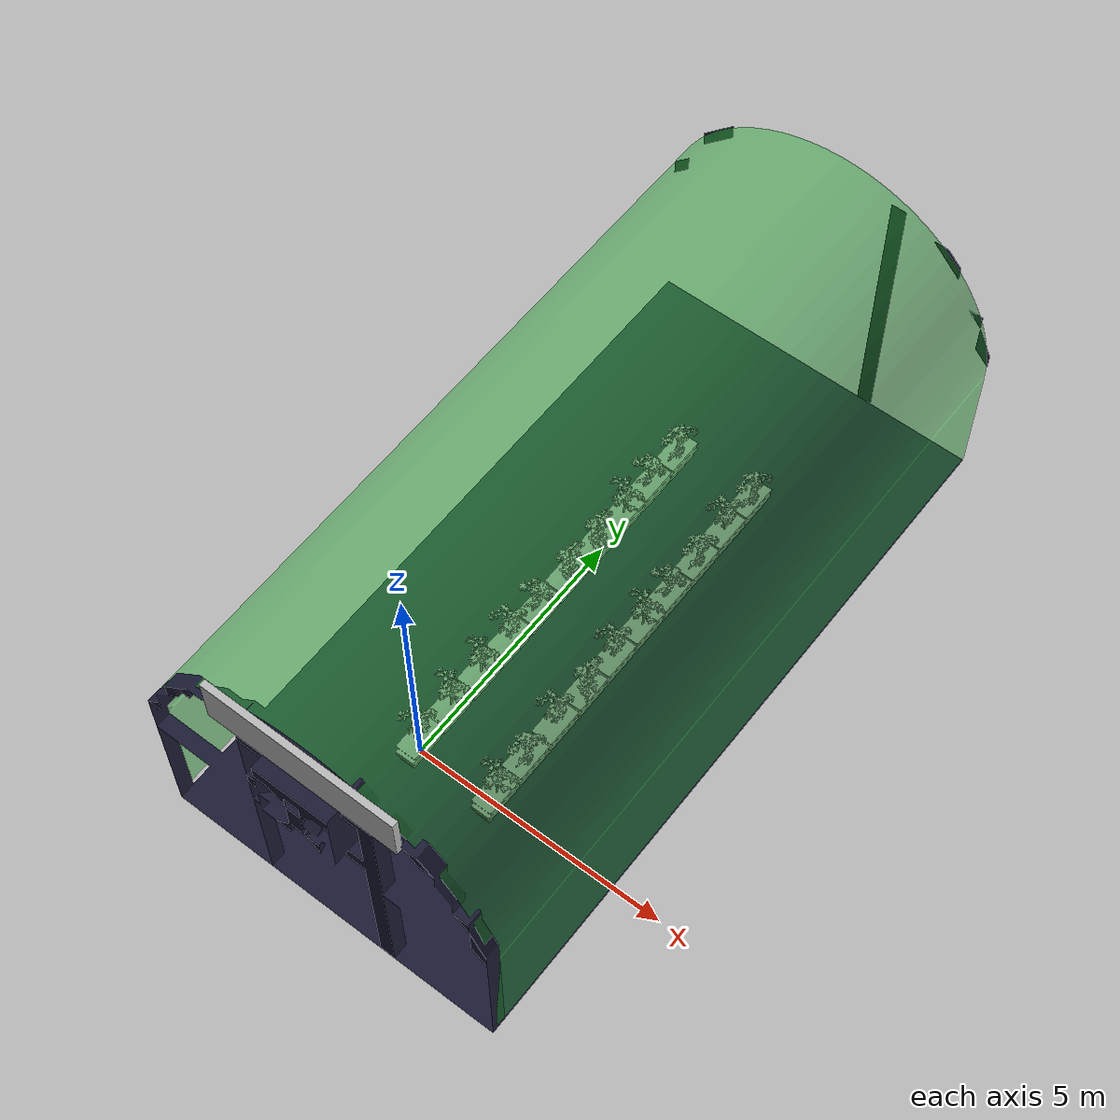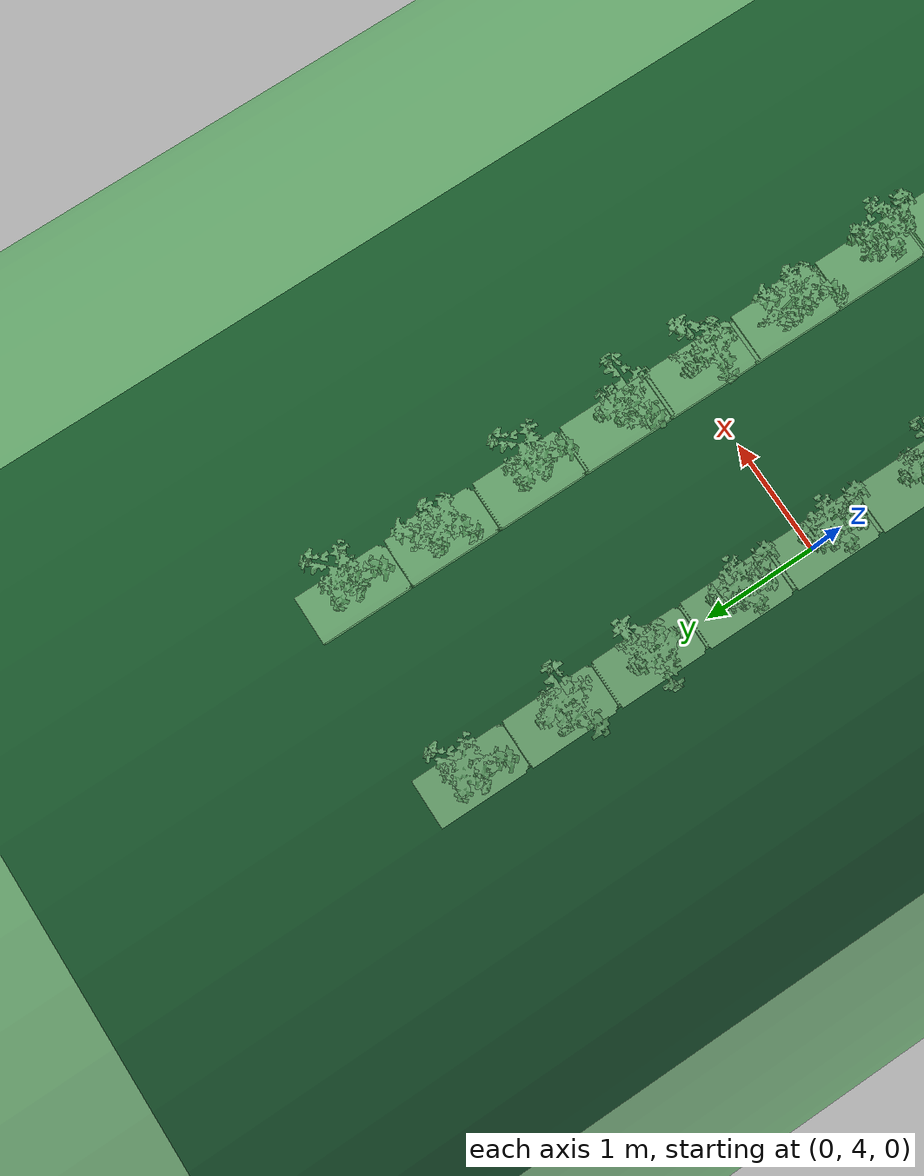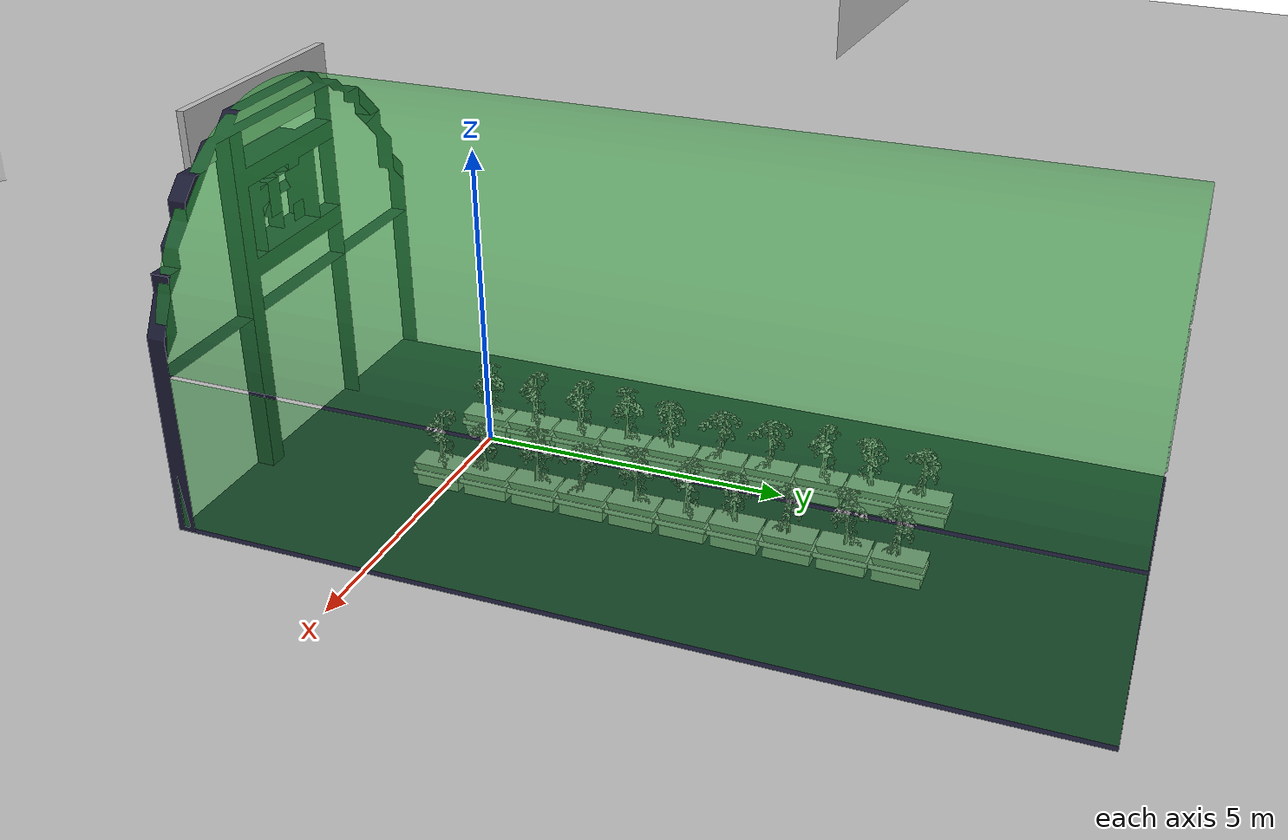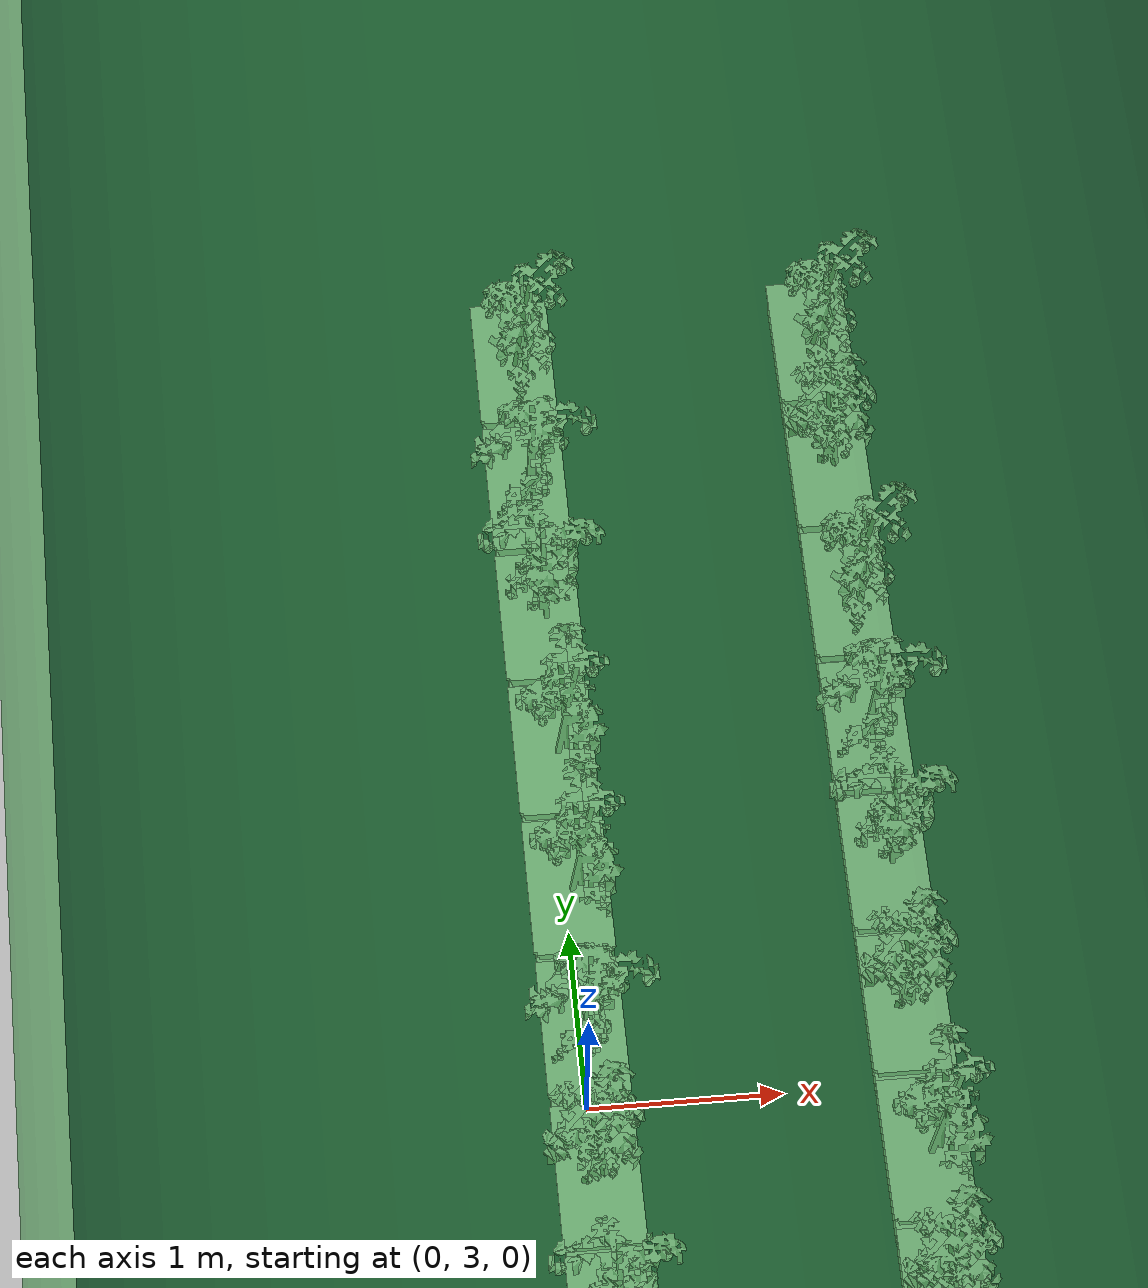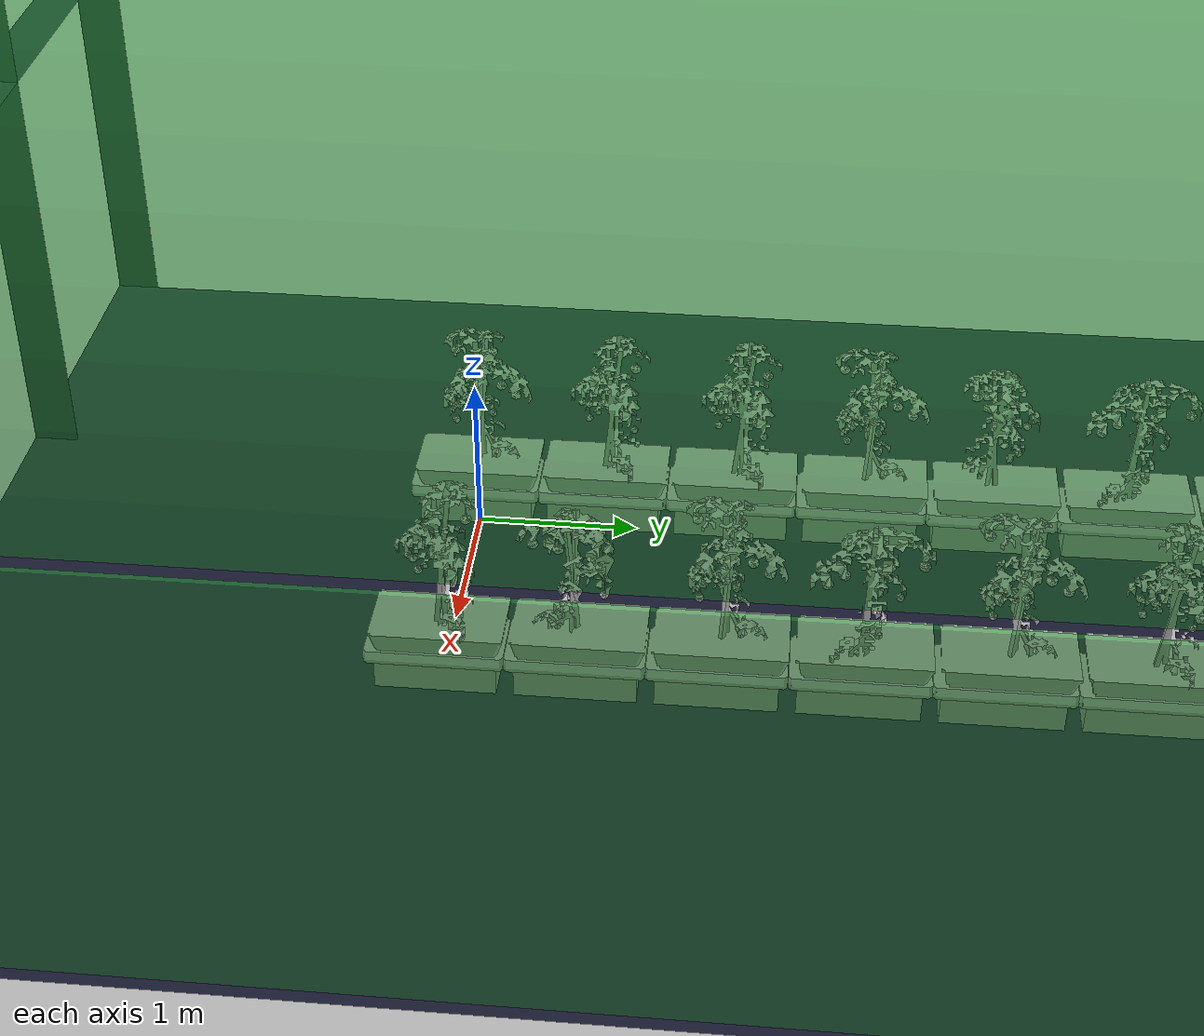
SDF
<sdf version="1.6">
 <world name="default">
  <scene>
   <shadows>0</shadows>
   <grid>0</grid>
   <sky><clouds><speed>4</speed></clouds></sky>
   <ambient>0.4 0.4 0.4 1</ambient>
   <background>0.7 0.7 0.7 1</background>
  </scene>
  <model name="farm">
   <static>1</static>
   <link name="link">
    <collision name="colision1"><geometry><box><size>2.32 1 1</size></box></geometry></collision>
    <visual name="visual1">
     <cast_shadows>0</cast_shadows>
     <geometry><mesh><uri>model://farm1/meshes/agriculture_world.dae</uri></mesh></geometry>
    </visual>
   </link>
   <pose>1.42405 -8.25 0.15 -0.02 0.029 -0</pose>
  </model>
  <model name="green_house">
   <static>1</static>
   <link name="link">
    <collision name="collision">
     <geometry>
      <mesh><scale>0.001 0.001 0.001</scale><uri>file://green_house/meshes/greenhouse_eyantra_glass.stl</uri></mesh>
     </geometry>
    </collision>
    <visual name="branch">
     <geometry>
      <mesh><scale>0.001 0.001 0.001</scale><uri>file://green_house/meshes/greenhouse_eyantra_glass.stl</uri></mesh>
     </geometry>
     <material>
      <script><name>Gazebo/GreenTransparent</name><uri>file://media/materials/scripts/gazebo.material</uri></script>
     </material>
    </visual>
   </link>
   <link name="link2">
    <collision name="collision2">
     <geometry>
      <mesh>
       <scale>0.001 0.001 0.001</scale>
       <uri>file://green_house/meshes/greenhouse_eyantra_skeleton.stl</uri>
      </mesh>
     </geometry>
    </collision>
    <visual name="branch2">
     <geometry>
      <mesh>
       <scale>0.001 0.001 0.001</scale>
       <uri>file://green_house/meshes/greenhouse_eyantra_skeleton.stl</uri>
      </mesh>
     </geometry>
     <material>
      <ambient>0.1 0.1 0.1 1</ambient>
      <diffuse>0.1 0.1 0.2 1</diffuse>
      <specular>0 0 0 0</specular>
      <emissive>0 0 0 1</emissive>
     </material>
    </visual>
   </link>
   <link name="link3">
    <pose>9.7 5.5 -0.2 3.14159 0.001593 3.14159</pose>
    <collision name="logo">
     <geometry><mesh><scale>400 400 400</scale><uri>file://green_house/meshes/logo2.dae</uri></mesh></geometry>
    </collision>
    <visual name="logo_c">
     <geometry><mesh><scale>400 400 400</scale><uri>file://green_house/meshes/logo2.dae</uri></mesh></geometry>
    </visual>
   </link>
   <joint name="logo" type="fixed"><child>link3</child><parent>link2</parent></joint>
   <pose>10.523 -2.987 0.1 1.57159 -0.001593 -3.14159</pose>
  </model>
  <gravity>0 0 -9.8</gravity>
  <magnetic_field>6e-06 2.3e-05 -4.2e-05</magnetic_field>
  <atmosphere type="adiabatic"/>
  <audio><device>default</device></audio>
  <spherical_coordinates>
   <surface_model>EARTH_WGS84</surface_model>
   <latitude_deg>0</latitude_deg>
   <longitude_deg>0</longitude_deg>
   <elevation>0</elevation>
   <heading_deg>0</heading_deg>
  </spherical_coordinates>
  <model name="plant00">
   <static>0</static>
   <link name="tomato_plant_link">
    <inertial>
     <mass>20</mass>
     <inertia><ixx>1</ixx><ixy>0</ixy><ixz>0</ixz><iyy>1</iyy><iyz>0</iyz><izz>1</izz></inertia>
    </inertial>
    <visual name="visual">
     <geometry><mesh><uri>model://tomato_plant/meshes/tomato_plant.obj</uri></mesh></geometry>
    </visual>
    <collision name="collision">
     <pose>0 0 0.01 0 -0 0</pose>
     <geometry><cylinder><radius>0.2</radius><length>0.02</length></cylinder></geometry>
    </collision>
   </link>
   <link name="t_link_0">
    <pose>0.176111 0.046061 0.713729 0 -0 0</pose>
    <inertial>
     <mass>0.1</mass>
     <inertia><ixx>1</ixx><ixy>0</ixy><ixz>0</ixz><iyy>1</iyy><iyz>0</iyz><izz>1</izz></inertia>
    </inertial>
    <collision name="collision"><geometry><sphere><radius>0.02</radius></sphere></geometry></collision>
    <visual name="visual">
     <geometry><mesh><uri>model://green_tomato/meshes/green_tomato.obj</uri></mesh></geometry>
    </visual>
   </link>
   <joint name="t_joint_0" type="fixed">
    <parent>tomato_plant_link</parent>
    <child>t_link_0</child>
    <axis>
     <xyz>0 0 1</xyz>
     <use_parent_model_frame>1</use_parent_model_frame>
     <limit><lower>-1e+16</lower><upper>1e+16</upper></limit>
    </axis>
    <sensor name="force_torque" type="force_torque">
     <always_on>1</always_on>
     <update_rate>250</update_rate>
     <plugin name="breakable_0" filename="libBreakableJointPlugin.so">
      <breaking_force_N>20</breaking_force_N>
     </plugin>
    </sensor>
   </joint>
   <link name="t_link_1">
    <pose>0.063172 0.108629 0.685474 0 -0 0</pose>
    <inertial>
     <mass>0.1</mass>
     <inertia><ixx>1</ixx><ixy>0</ixy><ixz>0</ixz><iyy>1</iyy><iyz>0</iyz><izz>1</izz></inertia>
    </inertial>
    <collision name="collision"><geometry><sphere><radius>0.02</radius></sphere></geometry></collision>
    <visual name="visual">
     <geometry><mesh><uri>model://green_tomato/meshes/green_tomato.obj</uri></mesh></geometry>
    </visual>
   </link>
   <joint name="t_joint_1" type="fixed">
    <parent>tomato_plant_link</parent>
    <child>t_link_1</child>
    <axis>
     <xyz>0 0 1</xyz>
     <use_parent_model_frame>1</use_parent_model_frame>
     <limit><lower>-1e+16</lower><upper>1e+16</upper></limit>
    </axis>
    <sensor name="force_torque" type="force_torque">
     <always_on>1</always_on>
     <update_rate>250</update_rate>
     <plugin name="breakable_1" filename="libBreakableJointPlugin.so">
      <breaking_force_N>20</breaking_force_N>
     </plugin>
    </sensor>
   </joint>
   <link name="t_link_2">
    <pose>0.062027 -0.170581 0.614534 0 -0 0</pose>
    <inertial>
     <mass>0.1</mass>
     <inertia><ixx>1</ixx><ixy>0</ixy><ixz>0</ixz><iyy>1</iyy><iyz>0</iyz><izz>1</izz></inertia>
    </inertial>
    <collision name="collision"><geometry><sphere><radius>0.02</radius></sphere></geometry></collision>
    <visual name="visual">
     <geometry><mesh><uri>model://green_tomato/meshes/green_tomato.obj</uri></mesh></geometry>
    </visual>
   </link>
   <joint name="t_joint_2" type="fixed">
    <parent>tomato_plant_link</parent>
    <child>t_link_2</child>
    <axis>
     <xyz>0 0 1</xyz>
     <use_parent_model_frame>1</use_parent_model_frame>
     <limit><lower>-1e+16</lower><upper>1e+16</upper></limit>
    </axis>
    <sensor name="force_torque" type="force_torque">
     <always_on>1</always_on>
     <update_rate>250</update_rate>
     <plugin name="breakable_2" filename="libBreakableJointPlugin.so">
      <breaking_force_N>20</breaking_force_N>
     </plugin>
    </sensor>
   </joint>
   <link name="t_link_3">
    <pose>0.114746 0.0304 0.926457 0 -0 0</pose>
    <inertial>
     <mass>0.1</mass>
     <inertia><ixx>1</ixx><ixy>0</ixy><ixz>0</ixz><iyy>1</iyy><iyz>0</iyz><izz>1</izz></inertia>
    </inertial>
    <collision name="collision"><geometry><sphere><radius>0.02</radius></sphere></geometry></collision>
    <visual name="visual">
     <geometry><mesh><uri>model://yellow_tomato/meshes/yellow_tomato.obj</uri></mesh></geometry>
    </visual>
   </link>
   <joint name="t_joint_3" type="fixed">
    <parent>tomato_plant_link</parent>
    <child>t_link_3</child>
    <axis>
     <xyz>0 0 1</xyz>
     <use_parent_model_frame>1</use_parent_model_frame>
     <limit><lower>-1e+16</lower><upper>1e+16</upper></limit>
    </axis>
    <sensor name="force_torque" type="force_torque">
     <always_on>1</always_on>
     <update_rate>250</update_rate>
     <plugin name="breakable_3" filename="libBreakableJointPlugin.so">
      <breaking_force_N>20</breaking_force_N>
     </plugin>
    </sensor>
   </joint>
   <link name="t_link_4">
    <pose>0.003426 0.147925 0.840454 0 -0 0</pose>
    <inertial>
     <mass>0.1</mass>
     <inertia><ixx>1</ixx><ixy>0</ixy><ixz>0</ixz><iyy>1</iyy><iyz>0</iyz><izz>1</izz></inertia>
    </inertial>
    <collision name="collision"><geometry><sphere><radius>0.02</radius></sphere></geometry></collision>
    <visual name="visual">
     <geometry><mesh><uri>model://yellow_tomato/meshes/yellow_tomato.obj</uri></mesh></geometry>
    </visual>
   </link>
   <joint name="t_joint_4" type="fixed">
    <parent>tomato_plant_link</parent>
    <child>t_link_4</child>
    <axis>
     <xyz>0 0 1</xyz>
     <use_parent_model_frame>1</use_parent_model_frame>
     <limit><lower>-1e+16</lower><upper>1e+16</upper></limit>
    </axis>
    <sensor name="force_torque" type="force_torque">
     <always_on>1</always_on>
     <update_rate>250</update_rate>
     <plugin name="breakable_4" filename="libBreakableJointPlugin.so">
      <breaking_force_N>20</breaking_force_N>
     </plugin>
    </sensor>
   </joint>
   <link name="t_link_5">
    <pose>-0.12391 0.091553 0.91111 0 -0 0</pose>
    <inertial>
     <mass>0.1</mass>
     <inertia><ixx>1</ixx><ixy>0</ixy><ixz>0</ixz><iyy>1</iyy><iyz>0</iyz><izz>1</izz></inertia>
    </inertial>
    <collision name="collision"><geometry><sphere><radius>0.02</radius></sphere></geometry></collision>
    <visual name="visual">
     <geometry><mesh><uri>model://yellow_tomato/meshes/yellow_tomato.obj</uri></mesh></geometry>
    </visual>
   </link>
   <joint name="t_joint_5" type="fixed">
    <parent>tomato_plant_link</parent>
    <child>t_link_5</child>
    <axis>
     <xyz>0 0 1</xyz>
     <use_parent_model_frame>1</use_parent_model_frame>
     <limit><lower>-1e+16</lower><upper>1e+16</upper></limit>
    </axis>
    <sensor name="force_torque" type="force_torque">
     <always_on>1</always_on>
     <update_rate>250</update_rate>
     <plugin name="breakable_5" filename="libBreakableJointPlugin.so">
      <breaking_force_N>20</breaking_force_N>
     </plugin>
    </sensor>
   </joint>
   <link name="t_link_6">
    <pose>-0.23014 -0.132697 0.911579 0 -0 0</pose>
    <inertial>
     <mass>0.1</mass>
     <inertia><ixx>1</ixx><ixy>0</ixy><ixz>0</ixz><iyy>1</iyy><iyz>0</iyz><izz>1</izz></inertia>
    </inertial>
    <collision name="collision"><geometry><sphere><radius>0.03</radius></sphere></geometry></collision>
    <visual name="visual">
     <geometry><mesh><uri>model://red_tomato/meshes/red_tomato.obj</uri></mesh></geometry>
    </visual>
   </link>
   <joint name="t_joint_6" type="fixed">
    <parent>tomato_plant_link</parent>
    <child>t_link_6</child>
    <axis>
     <xyz>0 0 1</xyz>
     <use_parent_model_frame>1</use_parent_model_frame>
     <limit><lower>-1e+16</lower><upper>1e+16</upper></limit>
    </axis>
    <sensor name="force_torque" type="force_torque">
     <always_on>1</always_on>
     <update_rate>250</update_rate>
     <plugin name="breakable_6" filename="libBreakableJointPlugin.so">
      <breaking_force_N>20</breaking_force_N>
     </plugin>
    </sensor>
   </joint>
   <link name="t_link_7">
    <pose>-0.139776 -0.09326 0.950185 0 -0 0</pose>
    <inertial>
     <mass>0.1</mass>
     <inertia><ixx>1</ixx><ixy>0</ixy><ixz>0</ixz><iyy>1</iyy><iyz>0</iyz><izz>1</izz></inertia>
    </inertial>
    <collision name="collision"><geometry><sphere><radius>0.03</radius></sphere></geometry></collision>
    <visual name="visual">
     <geometry><mesh><uri>model://red_tomato/meshes/red_tomato.obj</uri></mesh></geometry>
    </visual>
   </link>
   <joint name="t_joint_7" type="fixed">
    <parent>tomato_plant_link</parent>
    <child>t_link_7</child>
    <axis>
     <xyz>0 0 1</xyz>
     <use_parent_model_frame>1</use_parent_model_frame>
     <limit><lower>-1e+16</lower><upper>1e+16</upper></limit>
    </axis>
    <sensor name="force_torque" type="force_torque">
     <always_on>1</always_on>
     <update_rate>250</update_rate>
     <plugin name="breakable_7" filename="libBreakableJointPlugin.so">
      <breaking_force_N>20</breaking_force_N>
     </plugin>
    </sensor>
   </joint>
   <link name="t_link_8">
    <pose>0.284181 -0.063758 1.01928 0 -0 0</pose>
    <inertial>
     <mass>0.1</mass>
     <inertia><ixx>1</ixx><ixy>0</ixy><ixz>0</ixz><iyy>1</iyy><iyz>0</iyz><izz>1</izz></inertia>
    </inertial>
    <collision name="collision"><geometry><sphere><radius>0.03</radius></sphere></geometry></collision>
    <visual name="visual">
     <geometry><mesh><uri>model://red_tomato/meshes/red_tomato.obj</uri></mesh></geometry>
    </visual>
   </link>
   <joint name="t_joint_8" type="fixed">
    <parent>tomato_plant_link</parent>
    <child>t_link_8</child>
    <axis>
     <xyz>0 0 1</xyz>
     <use_parent_model_frame>1</use_parent_model_frame>
     <limit><lower>-1e+16</lower><upper>1e+16</upper></limit>
    </axis>
    <sensor name="force_torque" type="force_torque">
     <always_on>1</always_on>
     <update_rate>250</update_rate>
     <plugin name="breakable_8" filename="libBreakableJointPlugin.so">
      <breaking_force_N>20</breaking_force_N>
     </plugin>
    </sensor>
   </joint>
   <link name="t_link_9">
    <pose>0.055319 -0.176349 1.06525 0 -0 0</pose>
    <inertial>
     <mass>0.1</mass>
     <inertia><ixx>1</ixx><ixy>0</ixy><ixz>0</ixz><iyy>1</iyy><iyz>0</iyz><izz>1</izz></inertia>
    </inertial>
    <collision name="collision"><geometry><sphere><radius>0.03</radius></sphere></geometry></collision>
    <visual name="visual">
     <geometry><mesh><uri>model://red_tomato/meshes/red_tomato.obj</uri></mesh></geometry>
    </visual>
   </link>
   <joint name="t_joint_9" type="fixed">
    <parent>tomato_plant_link</parent>
    <child>t_link_9</child>
    <axis>
     <xyz>0 0 1</xyz>
     <use_parent_model_frame>1</use_parent_model_frame>
     <limit><lower>-1e+16</lower><upper>1e+16</upper></limit>
    </axis>
    <sensor name="force_torque" type="force_torque">
     <always_on>1</always_on>
     <update_rate>250</update_rate>
     <plugin name="breakable_9" filename="libBreakableJointPlugin.so">
      <breaking_force_N>20</breaking_force_N>
     </plugin>
    </sensor>
   </joint>
   <pose>0.017282 0.008773 0.114287 -0.000539 -0.001402 -2.35322</pose>
  </model>
  <model name="trough00">
   <static>1</static>
   <link name="trough_link">
    <visual name="visual"><geometry><mesh><uri>model://trough/meshes/truf.obj</uri></mesh></geometry></visual>
    <collision name="collision">
     <geometry><mesh><uri>model://trough/meshes/truf.obj</uri></mesh></geometry>
    </collision>
   </link>
   <link name="brick">
    <pose>0 -0.2 0 0 -0 0</pose>
    <visual name="visual"><geometry><mesh><uri>model://trough/meshes/brick.obj</uri></mesh></geometry></visual>
    <collision name="collision">
     <geometry><mesh><uri>model://trough/meshes/brick.obj</uri></mesh></geometry>
    </collision>
   </link>
   <pose>0 0 0.29 1.57 -0 1.57</pose>
  </model>
  <model name="plant01">
   <static>0</static>
   <link name="tomato_plant_link">
    <inertial>
     <mass>20</mass>
     <inertia><ixx>1</ixx><ixy>0</ixy><ixz>0</ixz><iyy>1</iyy><iyz>0</iyz><izz>1</izz></inertia>
    </inertial>
    <visual name="visual">
     <geometry><mesh><uri>model://tomato_plant/meshes/tomato_plant.obj</uri></mesh></geometry>
    </visual>
    <collision name="collision">
     <pose>0 0 0.01 0 -0 0</pose>
     <geometry><cylinder><radius>0.2</radius><length>0.02</length></cylinder></geometry>
    </collision>
   </link>
   <link name="t_link_0">
    <pose>0.176111 0.046061 0.713729 0 -0 0</pose>
    <inertial>
     <mass>0.1</mass>
     <inertia><ixx>1</ixx><ixy>0</ixy><ixz>0</ixz><iyy>1</iyy><iyz>0</iyz><izz>1</izz></inertia>
    </inertial>
    <collision name="collision"><geometry><sphere><radius>0.02</radius></sphere></geometry></collision>
    <visual name="visual">
     <geometry><mesh><uri>model://green_tomato/meshes/green_tomato.obj</uri></mesh></geometry>
    </visual>
   </link>
   <joint name="t_joint_0" type="fixed">
    <parent>tomato_plant_link</parent>
    <child>t_link_0</child>
    <axis>
     <xyz>0 0 1</xyz>
     <use_parent_model_frame>1</use_parent_model_frame>
     <limit><lower>-1e+16</lower><upper>1e+16</upper></limit>
    </axis>
    <sensor name="force_torque" type="force_torque">
     <always_on>1</always_on>
     <update_rate>250</update_rate>
     <plugin name="breakable_0" filename="libBreakableJointPlugin.so">
      <breaking_force_N>20</breaking_force_N>
     </plugin>
    </sensor>
   </joint>
   <link name="t_link_1">
    <pose>0.063172 0.108629 0.685474 0 -0 0</pose>
    <inertial>
     <mass>0.1</mass>
     <inertia><ixx>1</ixx><ixy>0</ixy><ixz>0</ixz><iyy>1</iyy><iyz>0</iyz><izz>1</izz></inertia>
    </inertial>
    <collision name="collision"><geometry><sphere><radius>0.02</radius></sphere></geometry></collision>
    <visual name="visual">
     <geometry><mesh><uri>model://green_tomato/meshes/green_tomato.obj</uri></mesh></geometry>
    </visual>
   </link>
   <joint name="t_joint_1" type="fixed">
    <parent>tomato_plant_link</parent>
    <child>t_link_1</child>
    <axis>
     <xyz>0 0 1</xyz>
     <use_parent_model_frame>1</use_parent_model_frame>
     <limit><lower>-1e+16</lower><upper>1e+16</upper></limit>
    </axis>
    <sensor name="force_torque" type="force_torque">
     <always_on>1</always_on>
     <update_rate>250</update_rate>
     <plugin name="breakable_1" filename="libBreakableJointPlugin.so">
      <breaking_force_N>20</breaking_force_N>
     </plugin>
    </sensor>
   </joint>
   <link name="t_link_2">
    <pose>0.062027 -0.170581 0.614534 0 -0 0</pose>
    <inertial>
     <mass>0.1</mass>
     <inertia><ixx>1</ixx><ixy>0</ixy><ixz>0</ixz><iyy>1</iyy><iyz>0</iyz><izz>1</izz></inertia>
    </inertial>
    <collision name="collision"><geometry><sphere><radius>0.02</radius></sphere></geometry></collision>
    <visual name="visual">
     <geometry><mesh><uri>model://green_tomato/meshes/green_tomato.obj</uri></mesh></geometry>
    </visual>
   </link>
   <joint name="t_joint_2" type="fixed">
    <parent>tomato_plant_link</parent>
    <child>t_link_2</child>
    <axis>
     <xyz>0 0 1</xyz>
     <use_parent_model_frame>1</use_parent_model_frame>
     <limit><lower>-1e+16</lower><upper>1e+16</upper></limit>
    </axis>
    <sensor name="force_torque" type="force_torque">
     <always_on>1</always_on>
     <update_rate>250</update_rate>
     <plugin name="breakable_2" filename="libBreakableJointPlugin.so">
      <breaking_force_N>20</breaking_force_N>
     </plugin>
    </sensor>
   </joint>
   <link name="t_link_3">
    <pose>0.114746 0.0304 0.926457 0 -0 0</pose>
    <inertial>
     <mass>0.1</mass>
     <inertia><ixx>1</ixx><ixy>0</ixy><ixz>0</ixz><iyy>1</iyy><iyz>0</iyz><izz>1</izz></inertia>
    </inertial>
    <collision name="collision"><geometry><sphere><radius>0.02</radius></sphere></geometry></collision>
    <visual name="visual">
     <geometry><mesh><uri>model://yellow_tomato/meshes/yellow_tomato.obj</uri></mesh></geometry>
    </visual>
   </link>
   <joint name="t_joint_3" type="fixed">
    <parent>tomato_plant_link</parent>
    <child>t_link_3</child>
    <axis>
     <xyz>0 0 1</xyz>
     <use_parent_model_frame>1</use_parent_model_frame>
     <limit><lower>-1e+16</lower><upper>1e+16</upper></limit>
    </axis>
    <sensor name="force_torque" type="force_torque">
     <always_on>1</always_on>
     <update_rate>250</update_rate>
     <plugin name="breakable_3" filename="libBreakableJointPlugin.so">
      <breaking_force_N>20</breaking_force_N>
     </plugin>
    </sensor>
   </joint>
   <link name="t_link_4">
    <pose>0.003426 0.147925 0.840454 0 -0 0</pose>
    <inertial>
     <mass>0.1</mass>
     <inertia><ixx>1</ixx><ixy>0</ixy><ixz>0</ixz><iyy>1</iyy><iyz>0</iyz><izz>1</izz></inertia>
    </inertial>
    <collision name="collision"><geometry><sphere><radius>0.02</radius></sphere></geometry></collision>
    <visual name="visual">
     <geometry><mesh><uri>model://yellow_tomato/meshes/yellow_tomato.obj</uri></mesh></geometry>
    </visual>
   </link>
   <joint name="t_joint_4" type="fixed">
    <parent>tomato_plant_link</parent>
    <child>t_link_4</child>
    <axis>
     <xyz>0 0 1</xyz>
     <use_parent_model_frame>1</use_parent_model_frame>
     <limit><lower>-1e+16</lower><upper>1e+16</upper></limit>
    </axis>
    <sensor name="force_torque" type="force_torque">
     <always_on>1</always_on>
     <update_rate>250</update_rate>
     <plugin name="breakable_4" filename="libBreakableJointPlugin.so">
      <breaking_force_N>20</breaking_force_N>
     </plugin>
    </sensor>
   </joint>
   <link name="t_link_5">
    <pose>-0.12391 0.091553 0.91111 0 -0 0</pose>
    <inertial>
     <mass>0.1</mass>
     <inertia><ixx>1</ixx><ixy>0</ixy><ixz>0</ixz><iyy>1</iyy><iyz>0</iyz><izz>1</izz></inertia>
    </inertial>
    <collision name="collision"><geometry><sphere><radius>0.02</radius></sphere></geometry></collision>
    <visual name="visual">
     <geometry><mesh><uri>model://yellow_tomato/meshes/yellow_tomato.obj</uri></mesh></geometry>
    </visual>
   </link>
   <joint name="t_joint_5" type="fixed">
    <parent>tomato_plant_link</parent>
    <child>t_link_5</child>
    <axis>
     <xyz>0 0 1</xyz>
     <use_parent_model_frame>1</use_parent_model_frame>
     <limit><lower>-1e+16</lower><upper>1e+16</upper></limit>
    </axis>
    <sensor name="force_torque" type="force_torque">
     <always_on>1</always_on>
     <update_rate>250</update_rate>
     <plugin name="breakable_5" filename="libBreakableJointPlugin.so">
      <breaking_force_N>20</breaking_force_N>
     </plugin>
    </sensor>
   </joint>
   <link name="t_link_6">
    <pose>-0.23014 -0.132697 0.911579 0 -0 0</pose>
    <inertial>
     <mass>0.1</mass>
     <inertia><ixx>1</ixx><ixy>0</ixy><ixz>0</ixz><iyy>1</iyy><iyz>0</iyz><izz>1</izz></inertia>
    </inertial>
    <collision name="collision"><geometry><sphere><radius>0.03</radius></sphere></geometry></collision>
    <visual name="visual">
     <geometry><mesh><uri>model://red_tomato/meshes/red_tomato.obj</uri></mesh></geometry>
    </visual>
   </link>
   <joint name="t_joint_6" type="fixed">
    <parent>tomato_plant_link</parent>
    <child>t_link_6</child>
    <axis>
     <xyz>0 0 1</xyz>
     <use_parent_model_frame>1</use_parent_model_frame>
     <limit><lower>-1e+16</lower><upper>1e+16</upper></limit>
    </axis>
    <sensor name="force_torque" type="force_torque">
     <always_on>1</always_on>
     <update_rate>250</update_rate>
     <plugin name="breakable_6" filename="libBreakableJointPlugin.so">
      <breaking_force_N>20</breaking_force_N>
     </plugin>
    </sensor>
   </joint>
   <link name="t_link_7">
    <pose>-0.139776 -0.09326 0.950185 0 -0 0</pose>
    <inertial>
     <mass>0.1</mass>
     <inertia><ixx>1</ixx><ixy>0</ixy><ixz>0</ixz><iyy>1</iyy><iyz>0</iyz><izz>1</izz></inertia>
    </inertial>
    <collision name="collision"><geometry><sphere><radius>0.03</radius></sphere></geometry></collision>
    <visual name="visual">
     <geometry><mesh><uri>model://red_tomato/meshes/red_tomato.obj</uri></mesh></geometry>
    </visual>
   </link>
   <joint name="t_joint_7" type="fixed">
    <parent>tomato_plant_link</parent>
    <child>t_link_7</child>
    <axis>
     <xyz>0 0 1</xyz>
     <use_parent_model_frame>1</use_parent_model_frame>
     <limit><lower>-1e+16</lower><upper>1e+16</upper></limit>
    </axis>
    <sensor name="force_torque" type="force_torque">
     <always_on>1</always_on>
     <update_rate>250</update_rate>
     <plugin name="breakable_7" filename="libBreakableJointPlugin.so">
      <breaking_force_N>20</breaking_force_N>
     </plugin>
    </sensor>
   </joint>
   <link name="t_link_8">
    <pose>0.284181 -0.063758 1.01928 0 -0 0</pose>
    <inertial>
     <mass>0.1</mass>
     <inertia><ixx>1</ixx><ixy>0</ixy><ixz>0</ixz><iyy>1</iyy><iyz>0</iyz><izz>1</izz></inertia>
    </inertial>
    <collision name="collision"><geometry><sphere><radius>0.03</radius></sphere></geometry></collision>
    <visual name="visual">
     <geometry><mesh><uri>model://red_tomato/meshes/red_tomato.obj</uri></mesh></geometry>
    </visual>
   </link>
   <joint name="t_joint_8" type="fixed">
    <parent>tomato_plant_link</parent>
    <child>t_link_8</child>
    <axis>
     <xyz>0 0 1</xyz>
     <use_parent_model_frame>1</use_parent_model_frame>
     <limit><lower>-1e+16</lower><upper>1e+16</upper></limit>
    </axis>
    <sensor name="force_torque" type="force_torque">
     <always_on>1</always_on>
     <update_rate>250</update_rate>
     <plugin name="breakable_8" filename="libBreakableJointPlugin.so">
      <breaking_force_N>20</breaking_force_N>
     </plugin>
    </sensor>
   </joint>
   <link name="t_link_9">
    <pose>0.055319 -0.176349 1.06525 0 -0 0</pose>
    <inertial>
     <mass>0.1</mass>
     <inertia><ixx>1</ixx><ixy>0</ixy><ixz>0</ixz><iyy>1</iyy><iyz>0</iyz><izz>1</izz></inertia>
    </inertial>
    <collision name="collision"><geometry><sphere><radius>0.03</radius></sphere></geometry></collision>
    <visual name="visual">
     <geometry><mesh><uri>model://red_tomato/meshes/red_tomato.obj</uri></mesh></geometry>
    </visual>
   </link>
   <joint name="t_joint_9" type="fixed">
    <parent>tomato_plant_link</parent>
    <child>t_link_9</child>
    <axis>
     <xyz>0 0 1</xyz>
     <use_parent_model_frame>1</use_parent_model_frame>
     <limit><lower>-1e+16</lower><upper>1e+16</upper></limit>
    </axis>
    <sensor name="force_torque" type="force_torque">
     <always_on>1</always_on>
     <update_rate>250</update_rate>
     <plugin name="breakable_9" filename="libBreakableJointPlugin.so">
      <breaking_force_N>20</breaking_force_N>
     </plugin>
    </sensor>
   </joint>
   <pose>0.01745 0.808714 0.113676 0.001014 -0.00195 3.14004</pose>
  </model>
  <model name="trough01">
   <static>1</static>
   <link name="trough_link">
    <visual name="visual"><geometry><mesh><uri>model://trough/meshes/truf.obj</uri></mesh></geometry></visual>
    <collision name="collision">
     <geometry><mesh><uri>model://trough/meshes/truf.obj</uri></mesh></geometry>
    </collision>
   </link>
   <link name="brick">
    <pose>0 -0.2 0 0 -0 0</pose>
    <visual name="visual"><geometry><mesh><uri>model://trough/meshes/brick.obj</uri></mesh></geometry></visual>
    <collision name="collision">
     <geometry><mesh><uri>model://trough/meshes/brick.obj</uri></mesh></geometry>
    </collision>
   </link>
   <pose>0 0.8 0.29 1.57 -0 1.57</pose>
  </model>
  <model name="plant02">
   <static>0</static>
   <link name="tomato_plant_link">
    <inertial>
     <mass>20</mass>
     <inertia><ixx>1</ixx><ixy>0</ixy><ixz>0</ixz><iyy>1</iyy><iyz>0</iyz><izz>1</izz></inertia>
    </inertial>
    <visual name="visual">
     <geometry><mesh><uri>model://tomato_plant/meshes/tomato_plant.obj</uri></mesh></geometry>
    </visual>
    <collision name="collision">
     <pose>0 0 0.01 0 -0 0</pose>
     <geometry><cylinder><radius>0.2</radius><length>0.02</length></cylinder></geometry>
    </collision>
   </link>
   <link name="t_link_0">
    <pose>0.176111 0.046061 0.713729 0 -0 0</pose>
    <inertial>
     <mass>0.1</mass>
     <inertia><ixx>1</ixx><ixy>0</ixy><ixz>0</ixz><iyy>1</iyy><iyz>0</iyz><izz>1</izz></inertia>
    </inertial>
    <collision name="collision"><geometry><sphere><radius>0.02</radius></sphere></geometry></collision>
    <visual name="visual">
     <geometry><mesh><uri>model://green_tomato/meshes/green_tomato.obj</uri></mesh></geometry>
    </visual>
   </link>
   <joint name="t_joint_0" type="fixed">
    <parent>tomato_plant_link</parent>
    <child>t_link_0</child>
    <axis>
     <xyz>0 0 1</xyz>
     <use_parent_model_frame>1</use_parent_model_frame>
     <limit><lower>-1e+16</lower><upper>1e+16</upper></limit>
    </axis>
    <sensor name="force_torque" type="force_torque">
     <always_on>1</always_on>
     <update_rate>250</update_rate>
     <plugin name="breakable_0" filename="libBreakableJointPlugin.so">
      <breaking_force_N>20</breaking_force_N>
     </plugin>
    </sensor>
   </joint>
   <link name="t_link_1">
    <pose>0.063172 0.108629 0.685474 0 -0 0</pose>
    <inertial>
     <mass>0.1</mass>
     <inertia><ixx>1</ixx><ixy>0</ixy><ixz>0</ixz><iyy>1</iyy><iyz>0</iyz><izz>1</izz></inertia>
    </inertial>
    <collision name="collision"><geometry><sphere><radius>0.02</radius></sphere></geometry></collision>
    <visual name="visual">
     <geometry><mesh><uri>model://green_tomato/meshes/green_tomato.obj</uri></mesh></geometry>
    </visual>
   </link>
   <joint name="t_joint_1" type="fixed">
    <parent>tomato_plant_link</parent>
    <child>t_link_1</child>
    <axis>
     <xyz>0 0 1</xyz>
     <use_parent_model_frame>1</use_parent_model_frame>
     <limit><lower>-1e+16</lower><upper>1e+16</upper></limit>
    </axis>
    <sensor name="force_torque" type="force_torque">
     <always_on>1</always_on>
     <update_rate>250</update_rate>
     <plugin name="breakable_1" filename="libBreakableJointPlugin.so">
      <breaking_force_N>20</breaking_force_N>
     </plugin>
    </sensor>
   </joint>
   <link name="t_link_2">
    <pose>0.062027 -0.170581 0.614534 0 -0 0</pose>
    <inertial>
     <mass>0.1</mass>
     <inertia><ixx>1</ixx><ixy>0</ixy><ixz>0</ixz><iyy>1</iyy><iyz>0</iyz><izz>1</izz></inertia>
    </inertial>
    <collision name="collision"><geometry><sphere><radius>0.02</radius></sphere></geometry></collision>
    <visual name="visual">
     <geometry><mesh><uri>model://green_tomato/meshes/green_tomato.obj</uri></mesh></geometry>
    </visual>
   </link>
   <joint name="t_joint_2" type="fixed">
    <parent>tomato_plant_link</parent>
    <child>t_link_2</child>
    <axis>
     <xyz>0 0 1</xyz>
     <use_parent_model_frame>1</use_parent_model_frame>
     <limit><lower>-1e+16</lower><upper>1e+16</upper></limit>
    </axis>
    <sensor name="force_torque" type="force_torque">
     <always_on>1</always_on>
     <update_rate>250</update_rate>
     <plugin name="breakable_2" filename="libBreakableJointPlugin.so">
      <breaking_force_N>20</breaking_force_N>
     </plugin>
    </sensor>
   </joint>
   <link name="t_link_3">
    <pose>0.114746 0.0304 0.926457 0 -0 0</pose>
    <inertial>
     <mass>0.1</mass>
     <inertia><ixx>1</ixx><ixy>0</ixy><ixz>0</ixz><iyy>1</iyy><iyz>0</iyz><izz>1</izz></inertia>
    </inertial>
    <collision name="collision"><geometry><sphere><radius>0.02</radius></sphere></geometry></collision>
    <visual name="visual">
     <geometry><mesh><uri>model://yellow_tomato/meshes/yellow_tomato.obj</uri></mesh></geometry>
    </visual>
   </link>
   <joint name="t_joint_3" type="fixed">
    <parent>tomato_plant_link</parent>
    <child>t_link_3</child>
    <axis>
     <xyz>0 0 1</xyz>
     <use_parent_model_frame>1</use_parent_model_frame>
     <limit><lower>-1e+16</lower><upper>1e+16</upper></limit>
    </axis>
    <sensor name="force_torque" type="force_torque">
     <always_on>1</always_on>
     <update_rate>250</update_rate>
     <plugin name="breakable_3" filename="libBreakableJointPlugin.so">
      <breaking_force_N>20</breaking_force_N>
     </plugin>
    </sensor>
   </joint>
   <link name="t_link_4">
    <pose>0.003426 0.147925 0.840454 0 -0 0</pose>
    <inertial>
     <mass>0.1</mass>
     <inertia><ixx>1</ixx><ixy>0</ixy><ixz>0</ixz><iyy>1</iyy><iyz>0</iyz><izz>1</izz></inertia>
    </inertial>
    <collision name="collision"><geometry><sphere><radius>0.02</radius></sphere></geometry></collision>
    <visual name="visual">
     <geometry><mesh><uri>model://yellow_tomato/meshes/yellow_tomato.obj</uri></mesh></geometry>
    </visual>
   </link>
   <joint name="t_joint_4" type="fixed">
    <parent>tomato_plant_link</parent>
    <child>t_link_4</child>
    <axis>
     <xyz>0 0 1</xyz>
     <use_parent_model_frame>1</use_parent_model_frame>
     <limit><lower>-1e+16</lower><upper>1e+16</upper></limit>
    </axis>
    <sensor name="force_torque" type="force_torque">
     <always_on>1</always_on>
     <update_rate>250</update_rate>
     <plugin name="breakable_4" filename="libBreakableJointPlugin.so">
      <breaking_force_N>20</breaking_force_N>
     </plugin>
    </sensor>
   </joint>
   <link name="t_link_5">
    <pose>-0.12391 0.091553 0.91111 0 -0 0</pose>
    <inertial>
     <mass>0.1</mass>
     <inertia><ixx>1</ixx><ixy>0</ixy><ixz>0</ixz><iyy>1</iyy><iyz>0</iyz><izz>1</izz></inertia>
    </inertial>
    <collision name="collision"><geometry><sphere><radius>0.02</radius></sphere></geometry></collision>
    <visual name="visual">
     <geometry><mesh><uri>model://yellow_tomato/meshes/yellow_tomato.obj</uri></mesh></geometry>
    </visual>
   </link>
   <joint name="t_joint_5" type="fixed">
    <parent>tomato_plant_link</parent>
    <child>t_link_5</child>
    <axis>
     <xyz>0 0 1</xyz>
     <use_parent_model_frame>1</use_parent_model_frame>
     <limit><lower>-1e+16</lower><upper>1e+16</upper></limit>
    </axis>
    <sensor name="force_torque" type="force_torque">
     <always_on>1</always_on>
     <update_rate>250</update_rate>
     <plugin name="breakable_5" filename="libBreakableJointPlugin.so">
      <breaking_force_N>20</breaking_force_N>
     </plugin>
    </sensor>
   </joint>
   <link name="t_link_6">
    <pose>-0.23014 -0.132697 0.911579 0 -0 0</pose>
    <inertial>
     <mass>0.1</mass>
     <inertia><ixx>1</ixx><ixy>0</ixy><ixz>0</ixz><iyy>1</iyy><iyz>0</iyz><izz>1</izz></inertia>
    </inertial>
    <collision name="collision"><geometry><sphere><radius>0.03</radius></sphere></geometry></collision>
    <visual name="visual">
     <geometry><mesh><uri>model://red_tomato/meshes/red_tomato.obj</uri></mesh></geometry>
    </visual>
   </link>
   <joint name="t_joint_6" type="fixed">
    <parent>tomato_plant_link</parent>
    <child>t_link_6</child>
    <axis>
     <xyz>0 0 1</xyz>
     <use_parent_model_frame>1</use_parent_model_frame>
     <limit><lower>-1e+16</lower><upper>1e+16</upper></limit>
    </axis>
    <sensor name="force_torque" type="force_torque">
     <always_on>1</always_on>
     <update_rate>250</update_rate>
     <plugin name="breakable_6" filename="libBreakableJointPlugin.so">
      <breaking_force_N>20</breaking_force_N>
     </plugin>
    </sensor>
   </joint>
   <link name="t_link_7">
    <pose>-0.139776 -0.09326 0.950185 0 -0 0</pose>
    <inertial>
     <mass>0.1</mass>
     <inertia><ixx>1</ixx><ixy>0</ixy><ixz>0</ixz><iyy>1</iyy><iyz>0</iyz><izz>1</izz></inertia>
    </inertial>
    <collision name="collision"><geometry><sphere><radius>0.03</radius></sphere></geometry></collision>
    <visual name="visual">
     <geometry><mesh><uri>model://red_tomato/meshes/red_tomato.obj</uri></mesh></geometry>
    </visual>
   </link>
   <joint name="t_joint_7" type="fixed">
    <parent>tomato_plant_link</parent>
    <child>t_link_7</child>
    <axis>
     <xyz>0 0 1</xyz>
     <use_parent_model_frame>1</use_parent_model_frame>
     <limit><lower>-1e+16</lower><upper>1e+16</upper></limit>
    </axis>
    <sensor name="force_torque" type="force_torque">
     <always_on>1</always_on>
     <update_rate>250</update_rate>
     <plugin name="breakable_7" filename="libBreakableJointPlugin.so">
      <breaking_force_N>20</breaking_force_N>
     </plugin>
    </sensor>
   </joint>
   <link name="t_link_8">
    <pose>0.284181 -0.063758 1.01928 0 -0 0</pose>
    <inertial>
     <mass>0.1</mass>
     <inertia><ixx>1</ixx><ixy>0</ixy><ixz>0</ixz><iyy>1</iyy><iyz>0</iyz><izz>1</izz></inertia>
    </inertial>
    <collision name="collision"><geometry><sphere><radius>0.03</radius></sphere></geometry></collision>
    <visual name="visual">
     <geometry><mesh><uri>model://red_tomato/meshes/red_tomato.obj</uri></mesh></geometry>
    </visual>
   </link>
   <joint name="t_joint_8" type="fixed">
    <parent>tomato_plant_link</parent>
    <child>t_link_8</child>
    <axis>
     <xyz>0 0 1</xyz>
     <use_parent_model_frame>1</use_parent_model_frame>
     <limit><lower>-1e+16</lower><upper>1e+16</upper></limit>
    </axis>
    <sensor name="force_torque" type="force_torque">
     <always_on>1</always_on>
     <update_rate>250</update_rate>
     <plugin name="breakable_8" filename="libBreakableJointPlugin.so">
      <breaking_force_N>20</breaking_force_N>
     </plugin>
    </sensor>
   </joint>
   <link name="t_link_9">
    <pose>0.055319 -0.176349 1.06525 0 -0 0</pose>
    <inertial>
     <mass>0.1</mass>
     <inertia><ixx>1</ixx><ixy>0</ixy><ixz>0</ixz><iyy>1</iyy><iyz>0</iyz><izz>1</izz></inertia>
    </inertial>
    <collision name="collision"><geometry><sphere><radius>0.03</radius></sphere></geometry></collision>
    <visual name="visual">
     <geometry><mesh><uri>model://red_tomato/meshes/red_tomato.obj</uri></mesh></geometry>
    </visual>
   </link>
   <joint name="t_joint_9" type="fixed">
    <parent>tomato_plant_link</parent>
    <child>t_link_9</child>
    <axis>
     <xyz>0 0 1</xyz>
     <use_parent_model_frame>1</use_parent_model_frame>
     <limit><lower>-1e+16</lower><upper>1e+16</upper></limit>
    </axis>
    <sensor name="force_torque" type="force_torque">
     <always_on>1</always_on>
     <update_rate>250</update_rate>
     <plugin name="breakable_9" filename="libBreakableJointPlugin.so">
      <breaking_force_N>20</breaking_force_N>
     </plugin>
    </sensor>
   </joint>
   <pose>0.017437 1.60871 0.113039 0.001015 -0.00195 3.14004</pose>
  </model>
  <model name="trough02">
   <static>1</static>
   <link name="trough_link">
    <visual name="visual"><geometry><mesh><uri>model://trough/meshes/truf.obj</uri></mesh></geometry></visual>
    <collision name="collision">
     <geometry><mesh><uri>model://trough/meshes/truf.obj</uri></mesh></geometry>
    </collision>
   </link>
   <link name="brick">
    <pose>0 -0.2 0 0 -0 0</pose>
    <visual name="visual"><geometry><mesh><uri>model://trough/meshes/brick.obj</uri></mesh></geometry></visual>
    <collision name="collision">
     <geometry><mesh><uri>model://trough/meshes/brick.obj</uri></mesh></geometry>
    </collision>
   </link>
   <pose>0 1.6 0.29 1.57 -0 1.57</pose>
  </model>
  <model name="plant03">
   <static>0</static>
   <link name="tomato_plant_link">
    <inertial>
     <mass>20</mass>
     <inertia><ixx>1</ixx><ixy>0</ixy><ixz>0</ixz><iyy>1</iyy><iyz>0</iyz><izz>1</izz></inertia>
    </inertial>
    <visual name="visual">
     <geometry><mesh><uri>model://tomato_plant/meshes/tomato_plant.obj</uri></mesh></geometry>
    </visual>
    <collision name="collision">
     <pose>0 0 0.01 0 -0 0</pose>
     <geometry><cylinder><radius>0.2</radius><length>0.02</length></cylinder></geometry>
    </collision>
   </link>
   <link name="t_link_0">
    <pose>0.176111 0.046061 0.713729 0 -0 0</pose>
    <inertial>
     <mass>0.1</mass>
     <inertia><ixx>1</ixx><ixy>0</ixy><ixz>0</ixz><iyy>1</iyy><iyz>0</iyz><izz>1</izz></inertia>
    </inertial>
    <collision name="collision"><geometry><sphere><radius>0.02</radius></sphere></geometry></collision>
    <visual name="visual">
     <geometry><mesh><uri>model://green_tomato/meshes/green_tomato.obj</uri></mesh></geometry>
    </visual>
   </link>
   <joint name="t_joint_0" type="fixed">
    <parent>tomato_plant_link</parent>
    <child>t_link_0</child>
    <axis>
     <xyz>0 0 1</xyz>
     <use_parent_model_frame>1</use_parent_model_frame>
     <limit><lower>-1e+16</lower><upper>1e+16</upper></limit>
    </axis>
    <sensor name="force_torque" type="force_torque">
     <always_on>1</always_on>
     <update_rate>250</update_rate>
     <plugin name="breakable_0" filename="libBreakableJointPlugin.so">
      <breaking_force_N>20</breaking_force_N>
     </plugin>
    </sensor>
   </joint>
   <link name="t_link_1">
    <pose>0.063172 0.108629 0.685474 0 -0 0</pose>
    <inertial>
     <mass>0.1</mass>
     <inertia><ixx>1</ixx><ixy>0</ixy><ixz>0</ixz><iyy>1</iyy><iyz>0</iyz><izz>1</izz></inertia>
    </inertial>
    <collision name="collision"><geometry><sphere><radius>0.02</radius></sphere></geometry></collision>
    <visual name="visual">
     <geometry><mesh><uri>model://green_tomato/meshes/green_tomato.obj</uri></mesh></geometry>
    </visual>
   </link>
   <joint name="t_joint_1" type="fixed">
    <parent>tomato_plant_link</parent>
    <child>t_link_1</child>
    <axis>
     <xyz>0 0 1</xyz>
     <use_parent_model_frame>1</use_parent_model_frame>
     <limit><lower>-1e+16</lower><upper>1e+16</upper></limit>
    </axis>
    <sensor name="force_torque" type="force_torque">
     <always_on>1</always_on>
     <update_rate>250</update_rate>
     <plugin name="breakable_1" filename="libBreakableJointPlugin.so">
      <breaking_force_N>20</breaking_force_N>
     </plugin>
    </sensor>
   </joint>
   <link name="t_link_2">
    <pose>0.062027 -0.170581 0.614534 0 -0 0</pose>
    <inertial>
     <mass>0.1</mass>
     <inertia><ixx>1</ixx><ixy>0</ixy><ixz>0</ixz><iyy>1</iyy><iyz>0</iyz><izz>1</izz></inertia>
    </inertial>
    <collision name="collision"><geometry><sphere><radius>0.02</radius></sphere></geometry></collision>
    <visual name="visual">
     <geometry><mesh><uri>model://green_tomato/meshes/green_tomato.obj</uri></mesh></geometry>
    </visual>
   </link>
   <joint name="t_joint_2" type="fixed">
    <parent>tomato_plant_link</parent>
    <child>t_link_2</child>
    <axis>
     <xyz>0 0 1</xyz>
     <use_parent_model_frame>1</use_parent_model_frame>
     <limit><lower>-1e+16</lower><upper>1e+16</upper></limit>
    </axis>
    <sensor name="force_torque" type="force_torque">
     <always_on>1</always_on>
     <update_rate>250</update_rate>
     <plugin name="breakable_2" filename="libBreakableJointPlugin.so">
      <breaking_force_N>20</breaking_force_N>
     </plugin>
    </sensor>
   </joint>
   <link name="t_link_3">
    <pose>0.114746 0.0304 0.926457 0 -0 0</pose>
    <inertial>
     <mass>0.1</mass>
     <inertia><ixx>1</ixx><ixy>0</ixy><ixz>0</ixz><iyy>1</iyy><iyz>0</iyz><izz>1</izz></inertia>
    </inertial>
    <collision name="collision"><geometry><sphere><radius>0.02</radius></sphere></geometry></collision>
    <visual name="visual">
     <geometry><mesh><uri>model://yellow_tomato/meshes/yellow_tomato.obj</uri></mesh></geometry>
    </visual>
   </link>
   <joint name="t_joint_3" type="fixed">
    <parent>tomato_plant_link</parent>
    <child>t_link_3</child>
    <axis>
     <xyz>0 0 1</xyz>
     <use_parent_model_frame>1</use_parent_model_frame>
     <limit><lower>-1e+16</lower><upper>1e+16</upper></limit>
    </axis>
    <sensor name="force_torque" type="force_torque">
     <always_on>1</always_on>
     <update_rate>250</update_rate>
     <plugin name="breakable_3" filename="libBreakableJointPlugin.so">
      <breaking_force_N>20</breaking_force_N>
     </plugin>
    </sensor>
   </joint>
   <link name="t_link_4">
    <pose>0.003426 0.147925 0.840454 0 -0 0</pose>
    <inertial>
     <mass>0.1</mass>
     <inertia><ixx>1</ixx><ixy>0</ixy><ixz>0</ixz><iyy>1</iyy><iyz>0</iyz><izz>1</izz></inertia>
    </inertial>
    <collision name="collision"><geometry><sphere><radius>0.02</radius></sphere></geometry></collision>
    <visual name="visual">
     <geometry><mesh><uri>model://yellow_tomato/meshes/yellow_tomato.obj</uri></mesh></geometry>
    </visual>
   </link>
   <joint name="t_joint_4" type="fixed">
    <parent>tomato_plant_link</parent>
    <child>t_link_4</child>
    <axis>
     <xyz>0 0 1</xyz>
     <use_parent_model_frame>1</use_parent_model_frame>
     <limit><lower>-1e+16</lower><upper>1e+16</upper></limit>
    </axis>
    <sensor name="force_torque" type="force_torque">
     <always_on>1</always_on>
     <update_rate>250</update_rate>
     <plugin name="breakable_4" filename="libBreakableJointPlugin.so">
      <breaking_force_N>20</breaking_force_N>
     </plugin>
    </sensor>
   </joint>
   <link name="t_link_5">
    <pose>-0.12391 0.091553 0.91111 0 -0 0</pose>
    <inertial>
     <mass>0.1</mass>
     <inertia><ixx>1</ixx><ixy>0</ixy><ixz>0</ixz><iyy>1</iyy><iyz>0</iyz><izz>1</izz></inertia>
    </inertial>
    <collision name="collision"><geometry><sphere><radius>0.02</radius></sphere></geometry></collision>
    <visual name="visual">
     <geometry><mesh><uri>model://yellow_tomato/meshes/yellow_tomato.obj</uri></mesh></geometry>
    </visual>
   </link>
   <joint name="t_joint_5" type="fixed">
    <parent>tomato_plant_link</parent>
    <child>t_link_5</child>
    <axis>
     <xyz>0 0 1</xyz>
     <use_parent_model_frame>1</use_parent_model_frame>
     <limit><lower>-1e+16</lower><upper>1e+16</upper></limit>
    </axis>
    <sensor name="force_torque" type="force_torque">
     <always_on>1</always_on>
     <update_rate>250</update_rate>
     <plugin name="breakable_5" filename="libBreakableJointPlugin.so">
      <breaking_force_N>20</breaking_force_N>
     </plugin>
    </sensor>
   </joint>
   <link name="t_link_6">
    <pose>-0.23014 -0.132697 0.911579 0 -0 0</pose>
    <inertial>
     <mass>0.1</mass>
     <inertia><ixx>1</ixx><ixy>0</ixy><ixz>0</ixz><iyy>1</iyy><iyz>0</iyz><izz>1</izz></inertia>
    </inertial>
    <collision name="collision"><geometry><sphere><radius>0.03</radius></sphere></geometry></collision>
    <visual name="visual">
     <geometry><mesh><uri>model://red_tomato/meshes/red_tomato.obj</uri></mesh></geometry>
    </visual>
   </link>
   <joint name="t_joint_6" type="fixed">
    <parent>tomato_plant_link</parent>
    <child>t_link_6</child>
    <axis>
     <xyz>0 0 1</xyz>
     <use_parent_model_frame>1</use_parent_model_frame>
     <limit><lower>-1e+16</lower><upper>1e+16</upper></limit>
    </axis>
    <sensor name="force_torque" type="force_torque">
     <always_on>1</always_on>
     <update_rate>250</update_rate>
     <plugin name="breakable_6" filename="libBreakableJointPlugin.so">
      <breaking_force_N>20</breaking_force_N>
     </plugin>
    </sensor>
   </joint>
   <link name="t_link_7">
    <pose>-0.139776 -0.09326 0.950185 0 -0 0</pose>
    <inertial>
     <mass>0.1</mass>
     <inertia><ixx>1</ixx><ixy>0</ixy><ixz>0</ixz><iyy>1</iyy><iyz>0</iyz><izz>1</izz></inertia>
    </inertial>
    <collision name="collision"><geometry><sphere><radius>0.03</radius></sphere></geometry></collision>
    <visual name="visual">
     <geometry><mesh><uri>model://red_tomato/meshes/red_tomato.obj</uri></mesh></geometry>
    </visual>
   </link>
   <joint name="t_joint_7" type="fixed">
    <parent>tomato_plant_link</parent>
    <child>t_link_7</child>
    <axis>
     <xyz>0 0 1</xyz>
     <use_parent_model_frame>1</use_parent_model_frame>
     <limit><lower>-1e+16</lower><upper>1e+16</upper></limit>
    </axis>
    <sensor name="force_torque" type="force_torque">
     <always_on>1</always_on>
     <update_rate>250</update_rate>
     <plugin name="breakable_7" filename="libBreakableJointPlugin.so">
      <breaking_force_N>20</breaking_force_N>
     </plugin>
    </sensor>
   </joint>
   <link name="t_link_8">
    <pose>0.284181 -0.063758 1.01928 0 -0 0</pose>
    <inertial>
     <mass>0.1</mass>
     <inertia><ixx>1</ixx><ixy>0</ixy><ixz>0</ixz><iyy>1</iyy><iyz>0</iyz><izz>1</izz></inertia>
    </inertial>
    <collision name="collision"><geometry><sphere><radius>0.03</radius></sphere></geometry></collision>
    <visual name="visual">
     <geometry><mesh><uri>model://red_tomato/meshes/red_tomato.obj</uri></mesh></geometry>
    </visual>
   </link>
   <joint name="t_joint_8" type="fixed">
    <parent>tomato_plant_link</parent>
    <child>t_link_8</child>
    <axis>
     <xyz>0 0 1</xyz>
     <use_parent_model_frame>1</use_parent_model_frame>
     <limit><lower>-1e+16</lower><upper>1e+16</upper></limit>
    </axis>
    <sensor name="force_torque" type="force_torque">
     <always_on>1</always_on>
     <update_rate>250</update_rate>
     <plugin name="breakable_8" filename="libBreakableJointPlugin.so">
      <breaking_force_N>20</breaking_force_N>
     </plugin>
    </sensor>
   </joint>
   <link name="t_link_9">
    <pose>0.055319 -0.176349 1.06525 0 -0 0</pose>
    <inertial>
     <mass>0.1</mass>
     <inertia><ixx>1</ixx><ixy>0</ixy><ixz>0</ixz><iyy>1</iyy><iyz>0</iyz><izz>1</izz></inertia>
    </inertial>
    <collision name="collision"><geometry><sphere><radius>0.03</radius></sphere></geometry></collision>
    <visual name="visual">
     <geometry><mesh><uri>model://red_tomato/meshes/red_tomato.obj</uri></mesh></geometry>
    </visual>
   </link>
   <joint name="t_joint_9" type="fixed">
    <parent>tomato_plant_link</parent>
    <child>t_link_9</child>
    <axis>
     <xyz>0 0 1</xyz>
     <use_parent_model_frame>1</use_parent_model_frame>
     <limit><lower>-1e+16</lower><upper>1e+16</upper></limit>
    </axis>
    <sensor name="force_torque" type="force_torque">
     <always_on>1</always_on>
     <update_rate>250</update_rate>
     <plugin name="breakable_9" filename="libBreakableJointPlugin.so">
      <breaking_force_N>20</breaking_force_N>
     </plugin>
    </sensor>
   </joint>
   <pose>0.017221 2.40875 0.112457 -0.000507 -0.001601 -2.35323</pose>
  </model>
  <model name="trough03">
   <static>1</static>
   <link name="trough_link">
    <visual name="visual"><geometry><mesh><uri>model://trough/meshes/truf.obj</uri></mesh></geometry></visual>
    <collision name="collision">
     <geometry><mesh><uri>model://trough/meshes/truf.obj</uri></mesh></geometry>
    </collision>
   </link>
   <link name="brick">
    <pose>0 -0.2 0 0 -0 0</pose>
    <visual name="visual"><geometry><mesh><uri>model://trough/meshes/brick.obj</uri></mesh></geometry></visual>
    <collision name="collision">
     <geometry><mesh><uri>model://trough/meshes/brick.obj</uri></mesh></geometry>
    </collision>
   </link>
   <pose>0 2.4 0.29 1.57 -0 1.57</pose>
  </model>
  <model name="plant04">
   <static>0</static>
   <link name="tomato_plant_link">
    <inertial>
     <mass>20</mass>
     <inertia><ixx>1</ixx><ixy>0</ixy><ixz>0</ixz><iyy>1</iyy><iyz>0</iyz><izz>1</izz></inertia>
    </inertial>
    <visual name="visual">
     <geometry><mesh><uri>model://tomato_plant/meshes/tomato_plant.obj</uri></mesh></geometry>
    </visual>
    <collision name="collision">
     <pose>0 0 0.01 0 -0 0</pose>
     <geometry><cylinder><radius>0.2</radius><length>0.02</length></cylinder></geometry>
    </collision>
   </link>
   <link name="t_link_0">
    <pose>0.176111 0.046061 0.713729 0 -0 0</pose>
    <inertial>
     <mass>0.1</mass>
     <inertia><ixx>1</ixx><ixy>0</ixy><ixz>0</ixz><iyy>1</iyy><iyz>0</iyz><izz>1</izz></inertia>
    </inertial>
    <collision name="collision"><geometry><sphere><radius>0.02</radius></sphere></geometry></collision>
    <visual name="visual">
     <geometry><mesh><uri>model://green_tomato/meshes/green_tomato.obj</uri></mesh></geometry>
    </visual>
   </link>
   <joint name="t_joint_0" type="fixed">
    <parent>tomato_plant_link</parent>
    <child>t_link_0</child>
    <axis>
     <xyz>0 0 1</xyz>
     <use_parent_model_frame>1</use_parent_model_frame>
     <limit><lower>-1e+16</lower><upper>1e+16</upper></limit>
    </axis>
    <sensor name="force_torque" type="force_torque">
     <always_on>1</always_on>
     <update_rate>250</update_rate>
     <plugin name="breakable_0" filename="libBreakableJointPlugin.so">
      <breaking_force_N>20</breaking_force_N>
     </plugin>
    </sensor>
   </joint>
   <link name="t_link_1">
    <pose>0.063172 0.108629 0.685474 0 -0 0</pose>
    <inertial>
     <mass>0.1</mass>
     <inertia><ixx>1</ixx><ixy>0</ixy><ixz>0</ixz><iyy>1</iyy><iyz>0</iyz><izz>1</izz></inertia>
    </inertial>
    <collision name="collision"><geometry><sphere><radius>0.02</radius></sphere></geometry></collision>
    <visual name="visual">
     <geometry><mesh><uri>model://green_tomato/meshes/green_tomato.obj</uri></mesh></geometry>
    </visual>
   </link>
   <joint name="t_joint_1" type="fixed">
    <parent>tomato_plant_link</parent>
    <child>t_link_1</child>
    <axis>
     <xyz>0 0 1</xyz>
     <use_parent_model_frame>1</use_parent_model_frame>
     <limit><lower>-1e+16</lower><upper>1e+16</upper></limit>
    </axis>
    <sensor name="force_torque" type="force_torque">
     <always_on>1</always_on>
     <update_rate>250</update_rate>
     <plugin name="breakable_1" filename="libBreakableJointPlugin.so">
      <breaking_force_N>20</breaking_force_N>
     </plugin>
    </sensor>
   </joint>
   <link name="t_link_2">
    <pose>0.062027 -0.170581 0.614534 0 -0 0</pose>
    <inertial>
     <mass>0.1</mass>
     <inertia><ixx>1</ixx><ixy>0</ixy><ixz>0</ixz><iyy>1</iyy><iyz>0</iyz><izz>1</izz></inertia>
    </inertial>
    <collision name="collision"><geometry><sphere><radius>0.02</radius></sphere></geometry></collision>
    <visual name="visual">
     <geometry><mesh><uri>model://green_tomato/meshes/green_tomato.obj</uri></mesh></geometry>
    </visual>
   </link>
   <joint name="t_joint_2" type="fixed">
    <parent>tomato_plant_link</parent>
    <child>t_link_2</child>
    <axis>
     <xyz>0 0 1</xyz>
     <use_parent_model_frame>1</use_parent_model_frame>
     <limit><lower>-1e+16</lower><upper>1e+16</upper></limit>
    </axis>
    <sensor name="force_torque" type="force_torque">
     <always_on>1</always_on>
     <update_rate>250</update_rate>
     <plugin name="breakable_2" filename="libBreakableJointPlugin.so">
      <breaking_force_N>20</breaking_force_N>
     </plugin>
    </sensor>
   </joint>
   <link name="t_link_3">
    <pose>0.114746 0.0304 0.926457 0 -0 0</pose>
    <inertial>
     <mass>0.1</mass>
     <inertia><ixx>1</ixx><ixy>0</ixy><ixz>0</ixz><iyy>1</iyy><iyz>0</iyz><izz>1</izz></inertia>
    </inertial>
    <collision name="collision"><geometry><sphere><radius>0.02</radius></sphere></geometry></collision>
    <visual name="visual">
     <geometry><mesh><uri>model://yellow_tomato/meshes/yellow_tomato.obj</uri></mesh></geometry>
    </visual>
   </link>
   <joint name="t_joint_3" type="fixed">
    <parent>tomato_plant_link</parent>
    <child>t_link_3</child>
    <axis>
     <xyz>0 0 1</xyz>
     <use_parent_model_frame>1</use_parent_model_frame>
     <limit><lower>-1e+16</lower><upper>1e+16</upper></limit>
    </axis>
    <sensor name="force_torque" type="force_torque">
     <always_on>1</always_on>
     <update_rate>250</update_rate>
     <plugin name="breakable_3" filename="libBreakableJointPlugin.so">
      <breaking_force_N>20</breaking_force_N>
     </plugin>
    </sensor>
   </joint>
   <link name="t_link_4">
    <pose>0.003426 0.147925 0.840454 0 -0 0</pose>
    <inertial>
     <mass>0.1</mass>
     <inertia><ixx>1</ixx><ixy>0</ixy><ixz>0</ixz><iyy>1</iyy><iyz>0</iyz><izz>1</izz></inertia>
    </inertial>
    <collision name="collision"><geometry><sphere><radius>0.02</radius></sphere></geometry></collision>
    <visual name="visual">
     <geometry><mesh><uri>model://yellow_tomato/meshes/yellow_tomato.obj</uri></mesh></geometry>
    </visual>
   </link>
   <joint name="t_joint_4" type="fixed">
    <parent>tomato_plant_link</parent>
    <child>t_link_4</child>
    <axis>
     <xyz>0 0 1</xyz>
     <use_parent_model_frame>1</use_parent_model_frame>
     <limit><lower>-1e+16</lower><upper>1e+16</upper></limit>
    </axis>
    <sensor name="force_torque" type="force_torque">
     <always_on>1</always_on>
     <update_rate>250</update_rate>
     <plugin name="breakable_4" filename="libBreakableJointPlugin.so">
      <breaking_force_N>20</breaking_force_N>
     </plugin>
    </sensor>
   </joint>
   <link name="t_link_5">
    <pose>-0.12391 0.091553 0.91111 0 -0 0</pose>
    <inertial>
     <mass>0.1</mass>
     <inertia><ixx>1</ixx><ixy>0</ixy><ixz>0</ixz><iyy>1</iyy><iyz>0</iyz><izz>1</izz></inertia>
    </inertial>
    <collision name="collision"><geometry><sphere><radius>0.02</radius></sphere></geometry></collision>
    <visual name="visual">
     <geometry><mesh><uri>model://yellow_tomato/meshes/yellow_tomato.obj</uri></mesh></geometry>
    </visual>
   </link>
   <joint name="t_joint_5" type="fixed">
    <parent>tomato_plant_link</parent>
    <child>t_link_5</child>
    <axis>
     <xyz>0 0 1</xyz>
     <use_parent_model_frame>1</use_parent_model_frame>
     <limit><lower>-1e+16</lower><upper>1e+16</upper></limit>
    </axis>
    <sensor name="force_torque" type="force_torque">
     <always_on>1</always_on>
     <update_rate>250</update_rate>
     <plugin name="breakable_5" filename="libBreakableJointPlugin.so">
      <breaking_force_N>20</breaking_force_N>
     </plugin>
    </sensor>
   </joint>
   <link name="t_link_6">
    <pose>-0.23014 -0.132697 0.911579 0 -0 0</pose>
    <inertial>
     <mass>0.1</mass>
     <inertia><ixx>1</ixx><ixy>0</ixy><ixz>0</ixz><iyy>1</iyy><iyz>0</iyz><izz>1</izz></inertia>
    </inertial>
    <collision name="collision"><geometry><sphere><radius>0.03</radius></sphere></geometry></collision>
    <visual name="visual">
     <geometry><mesh><uri>model://red_tomato/meshes/red_tomato.obj</uri></mesh></geometry>
    </visual>
   </link>
   <joint name="t_joint_6" type="fixed">
    <parent>tomato_plant_link</parent>
    <child>t_link_6</child>
    <axis>
     <xyz>0 0 1</xyz>
     <use_parent_model_frame>1</use_parent_model_frame>
     <limit><lower>-1e+16</lower><upper>1e+16</upper></limit>
    </axis>
    <sensor name="force_torque" type="force_torque">
     <always_on>1</always_on>
     <update_rate>250</update_rate>
     <plugin name="breakable_6" filename="libBreakableJointPlugin.so">
      <breaking_force_N>20</breaking_force_N>
     </plugin>
    </sensor>
   </joint>
   <link name="t_link_7">
    <pose>-0.139776 -0.09326 0.950185 0 -0 0</pose>
    <inertial>
     <mass>0.1</mass>
     <inertia><ixx>1</ixx><ixy>0</ixy><ixz>0</ixz><iyy>1</iyy><iyz>0</iyz><izz>1</izz></inertia>
    </inertial>
    <collision name="collision"><geometry><sphere><radius>0.03</radius></sphere></geometry></collision>
    <visual name="visual">
     <geometry><mesh><uri>model://red_tomato/meshes/red_tomato.obj</uri></mesh></geometry>
    </visual>
   </link>
   <joint name="t_joint_7" type="fixed">
    <parent>tomato_plant_link</parent>
    <child>t_link_7</child>
    <axis>
     <xyz>0 0 1</xyz>
     <use_parent_model_frame>1</use_parent_model_frame>
     <limit><lower>-1e+16</lower><upper>1e+16</upper></limit>
    </axis>
    <sensor name="force_torque" type="force_torque">
     <always_on>1</always_on>
     <update_rate>250</update_rate>
     <plugin name="breakable_7" filename="libBreakableJointPlugin.so">
      <breaking_force_N>20</breaking_force_N>
     </plugin>
    </sensor>
   </joint>
   <link name="t_link_8">
    <pose>0.284181 -0.063758 1.01928 0 -0 0</pose>
    <inertial>
     <mass>0.1</mass>
     <inertia><ixx>1</ixx><ixy>0</ixy><ixz>0</ixz><iyy>1</iyy><iyz>0</iyz><izz>1</izz></inertia>
    </inertial>
    <collision name="collision"><geometry><sphere><radius>0.03</radius></sphere></geometry></collision>
    <visual name="visual">
     <geometry><mesh><uri>model://red_tomato/meshes/red_tomato.obj</uri></mesh></geometry>
    </visual>
   </link>
   <joint name="t_joint_8" type="fixed">
    <parent>tomato_plant_link</parent>
    <child>t_link_8</child>
    <axis>
     <xyz>0 0 1</xyz>
     <use_parent_model_frame>1</use_parent_model_frame>
     <limit><lower>-1e+16</lower><upper>1e+16</upper></limit>
    </axis>
    <sensor name="force_torque" type="force_torque">
     <always_on>1</always_on>
     <update_rate>250</update_rate>
     <plugin name="breakable_8" filename="libBreakableJointPlugin.so">
      <breaking_force_N>20</breaking_force_N>
     </plugin>
    </sensor>
   </joint>
   <link name="t_link_9">
    <pose>0.055319 -0.176349 1.06525 0 -0 0</pose>
    <inertial>
     <mass>0.1</mass>
     <inertia><ixx>1</ixx><ixy>0</ixy><ixz>0</ixz><iyy>1</iyy><iyz>0</iyz><izz>1</izz></inertia>
    </inertial>
    <collision name="collision"><geometry><sphere><radius>0.03</radius></sphere></geometry></collision>
    <visual name="visual">
     <geometry><mesh><uri>model://red_tomato/meshes/red_tomato.obj</uri></mesh></geometry>
    </visual>
   </link>
   <joint name="t_joint_9" type="fixed">
    <parent>tomato_plant_link</parent>
    <child>t_link_9</child>
    <axis>
     <xyz>0 0 1</xyz>
     <use_parent_model_frame>1</use_parent_model_frame>
     <limit><lower>-1e+16</lower><upper>1e+16</upper></limit>
    </axis>
    <sensor name="force_torque" type="force_torque">
     <always_on>1</always_on>
     <update_rate>250</update_rate>
     <plugin name="breakable_9" filename="libBreakableJointPlugin.so">
      <breaking_force_N>20</breaking_force_N>
     </plugin>
    </sensor>
   </joint>
   <pose>0.017402 3.20864 0.111767 -0.000983 0.00198 -0.000388</pose>
  </model>
  <model name="trough04">
   <static>1</static>
   <link name="trough_link">
    <visual name="visual"><geometry><mesh><uri>model://trough/meshes/truf.obj</uri></mesh></geometry></visual>
    <collision name="collision">
     <geometry><mesh><uri>model://trough/meshes/truf.obj</uri></mesh></geometry>
    </collision>
   </link>
   <link name="brick">
    <pose>0 -0.2 0 0 -0 0</pose>
    <visual name="visual"><geometry><mesh><uri>model://trough/meshes/brick.obj</uri></mesh></geometry></visual>
    <collision name="collision">
     <geometry><mesh><uri>model://trough/meshes/brick.obj</uri></mesh></geometry>
    </collision>
   </link>
   <pose>0 3.2 0.29 1.57 -0 1.57</pose>
  </model>
  <model name="plant05">
   <static>0</static>
   <link name="tomato_plant_link">
    <inertial>
     <mass>20</mass>
     <inertia><ixx>1</ixx><ixy>0</ixy><ixz>0</ixz><iyy>1</iyy><iyz>0</iyz><izz>1</izz></inertia>
    </inertial>
    <visual name="visual">
     <geometry><mesh><uri>model://tomato_plant/meshes/tomato_plant.obj</uri></mesh></geometry>
    </visual>
    <collision name="collision">
     <pose>0 0 0.01 0 -0 0</pose>
     <geometry><cylinder><radius>0.2</radius><length>0.02</length></cylinder></geometry>
    </collision>
   </link>
   <link name="t_link_0">
    <pose>0.176111 0.046061 0.713729 0 -0 0</pose>
    <inertial>
     <mass>0.1</mass>
     <inertia><ixx>1</ixx><ixy>0</ixy><ixz>0</ixz><iyy>1</iyy><iyz>0</iyz><izz>1</izz></inertia>
    </inertial>
    <collision name="collision"><geometry><sphere><radius>0.02</radius></sphere></geometry></collision>
    <visual name="visual">
     <geometry><mesh><uri>model://green_tomato/meshes/green_tomato.obj</uri></mesh></geometry>
    </visual>
   </link>
   <joint name="t_joint_0" type="fixed">
    <parent>tomato_plant_link</parent>
    <child>t_link_0</child>
    <axis>
     <xyz>0 0 1</xyz>
     <use_parent_model_frame>1</use_parent_model_frame>
     <limit><lower>-1e+16</lower><upper>1e+16</upper></limit>
    </axis>
    <sensor name="force_torque" type="force_torque">
     <always_on>1</always_on>
     <update_rate>250</update_rate>
     <plugin name="breakable_0" filename="libBreakableJointPlugin.so">
      <breaking_force_N>20</breaking_force_N>
     </plugin>
    </sensor>
   </joint>
   <link name="t_link_1">
    <pose>0.063172 0.108629 0.685474 0 -0 0</pose>
    <inertial>
     <mass>0.1</mass>
     <inertia><ixx>1</ixx><ixy>0</ixy><ixz>0</ixz><iyy>1</iyy><iyz>0</iyz><izz>1</izz></inertia>
    </inertial>
    <collision name="collision"><geometry><sphere><radius>0.02</radius></sphere></geometry></collision>
    <visual name="visual">
     <geometry><mesh><uri>model://green_tomato/meshes/green_tomato.obj</uri></mesh></geometry>
    </visual>
   </link>
   <joint name="t_joint_1" type="fixed">
    <parent>tomato_plant_link</parent>
    <child>t_link_1</child>
    <axis>
     <xyz>0 0 1</xyz>
     <use_parent_model_frame>1</use_parent_model_frame>
     <limit><lower>-1e+16</lower><upper>1e+16</upper></limit>
    </axis>
    <sensor name="force_torque" type="force_torque">
     <always_on>1</always_on>
     <update_rate>250</update_rate>
     <plugin name="breakable_1" filename="libBreakableJointPlugin.so">
      <breaking_force_N>20</breaking_force_N>
     </plugin>
    </sensor>
   </joint>
   <link name="t_link_2">
    <pose>0.062027 -0.170581 0.614534 0 -0 0</pose>
    <inertial>
     <mass>0.1</mass>
     <inertia><ixx>1</ixx><ixy>0</ixy><ixz>0</ixz><iyy>1</iyy><iyz>0</iyz><izz>1</izz></inertia>
    </inertial>
    <collision name="collision"><geometry><sphere><radius>0.02</radius></sphere></geometry></collision>
    <visual name="visual">
     <geometry><mesh><uri>model://green_tomato/meshes/green_tomato.obj</uri></mesh></geometry>
    </visual>
   </link>
   <joint name="t_joint_2" type="fixed">
    <parent>tomato_plant_link</parent>
    <child>t_link_2</child>
    <axis>
     <xyz>0 0 1</xyz>
     <use_parent_model_frame>1</use_parent_model_frame>
     <limit><lower>-1e+16</lower><upper>1e+16</upper></limit>
    </axis>
    <sensor name="force_torque" type="force_torque">
     <always_on>1</always_on>
     <update_rate>250</update_rate>
     <plugin name="breakable_2" filename="libBreakableJointPlugin.so">
      <breaking_force_N>20</breaking_force_N>
     </plugin>
    </sensor>
   </joint>
   <link name="t_link_3">
    <pose>0.114746 0.0304 0.926457 0 -0 0</pose>
    <inertial>
     <mass>0.1</mass>
     <inertia><ixx>1</ixx><ixy>0</ixy><ixz>0</ixz><iyy>1</iyy><iyz>0</iyz><izz>1</izz></inertia>
    </inertial>
    <collision name="collision"><geometry><sphere><radius>0.02</radius></sphere></geometry></collision>
    <visual name="visual">
     <geometry><mesh><uri>model://yellow_tomato/meshes/yellow_tomato.obj</uri></mesh></geometry>
    </visual>
   </link>
   <joint name="t_joint_3" type="fixed">
    <parent>tomato_plant_link</parent>
    <child>t_link_3</child>
    <axis>
     <xyz>0 0 1</xyz>
     <use_parent_model_frame>1</use_parent_model_frame>
     <limit><lower>-1e+16</lower><upper>1e+16</upper></limit>
    </axis>
    <sensor name="force_torque" type="force_torque">
     <always_on>1</always_on>
     <update_rate>250</update_rate>
     <plugin name="breakable_3" filename="libBreakableJointPlugin.so">
      <breaking_force_N>20</breaking_force_N>
     </plugin>
    </sensor>
   </joint>
   <link name="t_link_4">
    <pose>0.003426 0.147925 0.840454 0 -0 0</pose>
    <inertial>
     <mass>0.1</mass>
     <inertia><ixx>1</ixx><ixy>0</ixy><ixz>0</ixz><iyy>1</iyy><iyz>0</iyz><izz>1</izz></inertia>
    </inertial>
    <collision name="collision"><geometry><sphere><radius>0.02</radius></sphere></geometry></collision>
    <visual name="visual">
     <geometry><mesh><uri>model://yellow_tomato/meshes/yellow_tomato.obj</uri></mesh></geometry>
    </visual>
   </link>
   <joint name="t_joint_4" type="fixed">
    <parent>tomato_plant_link</parent>
    <child>t_link_4</child>
    <axis>
     <xyz>0 0 1</xyz>
     <use_parent_model_frame>1</use_parent_model_frame>
     <limit><lower>-1e+16</lower><upper>1e+16</upper></limit>
    </axis>
    <sensor name="force_torque" type="force_torque">
     <always_on>1</always_on>
     <update_rate>250</update_rate>
     <plugin name="breakable_4" filename="libBreakableJointPlugin.so">
      <breaking_force_N>20</breaking_force_N>
     </plugin>
    </sensor>
   </joint>
   <link name="t_link_5">
    <pose>-0.12391 0.091553 0.91111 0 -0 0</pose>
    <inertial>
     <mass>0.1</mass>
     <inertia><ixx>1</ixx><ixy>0</ixy><ixz>0</ixz><iyy>1</iyy><iyz>0</iyz><izz>1</izz></inertia>
    </inertial>
    <collision name="collision"><geometry><sphere><radius>0.02</radius></sphere></geometry></collision>
    <visual name="visual">
     <geometry><mesh><uri>model://yellow_tomato/meshes/yellow_tomato.obj</uri></mesh></geometry>
    </visual>
   </link>
   <joint name="t_joint_5" type="fixed">
    <parent>tomato_plant_link</parent>
    <child>t_link_5</child>
    <axis>
     <xyz>0 0 1</xyz>
     <use_parent_model_frame>1</use_parent_model_frame>
     <limit><lower>-1e+16</lower><upper>1e+16</upper></limit>
    </axis>
    <sensor name="force_torque" type="force_torque">
     <always_on>1</always_on>
     <update_rate>250</update_rate>
     <plugin name="breakable_5" filename="libBreakableJointPlugin.so">
      <breaking_force_N>20</breaking_force_N>
     </plugin>
    </sensor>
   </joint>
   <link name="t_link_6">
    <pose>-0.23014 -0.132697 0.911579 0 -0 0</pose>
    <inertial>
     <mass>0.1</mass>
     <inertia><ixx>1</ixx><ixy>0</ixy><ixz>0</ixz><iyy>1</iyy><iyz>0</iyz><izz>1</izz></inertia>
    </inertial>
    <collision name="collision"><geometry><sphere><radius>0.03</radius></sphere></geometry></collision>
    <visual name="visual">
     <geometry><mesh><uri>model://red_tomato/meshes/red_tomato.obj</uri></mesh></geometry>
    </visual>
   </link>
   <joint name="t_joint_6" type="fixed">
    <parent>tomato_plant_link</parent>
    <child>t_link_6</child>
    <axis>
     <xyz>0 0 1</xyz>
     <use_parent_model_frame>1</use_parent_model_frame>
     <limit><lower>-1e+16</lower><upper>1e+16</upper></limit>
    </axis>
    <sensor name="force_torque" type="force_torque">
     <always_on>1</always_on>
     <update_rate>250</update_rate>
     <plugin name="breakable_6" filename="libBreakableJointPlugin.so">
      <breaking_force_N>20</breaking_force_N>
     </plugin>
    </sensor>
   </joint>
   <link name="t_link_7">
    <pose>-0.139776 -0.09326 0.950185 0 -0 0</pose>
    <inertial>
     <mass>0.1</mass>
     <inertia><ixx>1</ixx><ixy>0</ixy><ixz>0</ixz><iyy>1</iyy><iyz>0</iyz><izz>1</izz></inertia>
    </inertial>
    <collision name="collision"><geometry><sphere><radius>0.03</radius></sphere></geometry></collision>
    <visual name="visual">
     <geometry><mesh><uri>model://red_tomato/meshes/red_tomato.obj</uri></mesh></geometry>
    </visual>
   </link>
   <joint name="t_joint_7" type="fixed">
    <parent>tomato_plant_link</parent>
    <child>t_link_7</child>
    <axis>
     <xyz>0 0 1</xyz>
     <use_parent_model_frame>1</use_parent_model_frame>
     <limit><lower>-1e+16</lower><upper>1e+16</upper></limit>
    </axis>
    <sensor name="force_torque" type="force_torque">
     <always_on>1</always_on>
     <update_rate>250</update_rate>
     <plugin name="breakable_7" filename="libBreakableJointPlugin.so">
      <breaking_force_N>20</breaking_force_N>
     </plugin>
    </sensor>
   </joint>
   <link name="t_link_8">
    <pose>0.284181 -0.063758 1.01928 0 -0 0</pose>
    <inertial>
     <mass>0.1</mass>
     <inertia><ixx>1</ixx><ixy>0</ixy><ixz>0</ixz><iyy>1</iyy><iyz>0</iyz><izz>1</izz></inertia>
    </inertial>
    <collision name="collision"><geometry><sphere><radius>0.03</radius></sphere></geometry></collision>
    <visual name="visual">
     <geometry><mesh><uri>model://red_tomato/meshes/red_tomato.obj</uri></mesh></geometry>
    </visual>
   </link>
   <joint name="t_joint_8" type="fixed">
    <parent>tomato_plant_link</parent>
    <child>t_link_8</child>
    <axis>
     <xyz>0 0 1</xyz>
     <use_parent_model_frame>1</use_parent_model_frame>
     <limit><lower>-1e+16</lower><upper>1e+16</upper></limit>
    </axis>
    <sensor name="force_torque" type="force_torque">
     <always_on>1</always_on>
     <update_rate>250</update_rate>
     <plugin name="breakable_8" filename="libBreakableJointPlugin.so">
      <breaking_force_N>20</breaking_force_N>
     </plugin>
    </sensor>
   </joint>
   <link name="t_link_9">
    <pose>0.055319 -0.176349 1.06525 0 -0 0</pose>
    <inertial>
     <mass>0.1</mass>
     <inertia><ixx>1</ixx><ixy>0</ixy><ixz>0</ixz><iyy>1</iyy><iyz>0</iyz><izz>1</izz></inertia>
    </inertial>
    <collision name="collision"><geometry><sphere><radius>0.03</radius></sphere></geometry></collision>
    <visual name="visual">
     <geometry><mesh><uri>model://red_tomato/meshes/red_tomato.obj</uri></mesh></geometry>
    </visual>
   </link>
   <joint name="t_joint_9" type="fixed">
    <parent>tomato_plant_link</parent>
    <child>t_link_9</child>
    <axis>
     <xyz>0 0 1</xyz>
     <use_parent_model_frame>1</use_parent_model_frame>
     <limit><lower>-1e+16</lower><upper>1e+16</upper></limit>
    </axis>
    <sensor name="force_torque" type="force_torque">
     <always_on>1</always_on>
     <update_rate>250</update_rate>
     <plugin name="breakable_9" filename="libBreakableJointPlugin.so">
      <breaking_force_N>20</breaking_force_N>
     </plugin>
    </sensor>
   </joint>
   <pose>0.01742 4.00871 0.111062 0.001503 0.000793 1.56998</pose>
  </model>
  <model name="trough05">
   <static>1</static>
   <link name="trough_link">
    <visual name="visual"><geometry><mesh><uri>model://trough/meshes/truf.obj</uri></mesh></geometry></visual>
    <collision name="collision">
     <geometry><mesh><uri>model://trough/meshes/truf.obj</uri></mesh></geometry>
    </collision>
   </link>
   <link name="brick">
    <pose>0 -0.2 0 0 -0 0</pose>
    <visual name="visual"><geometry><mesh><uri>model://trough/meshes/brick.obj</uri></mesh></geometry></visual>
    <collision name="collision">
     <geometry><mesh><uri>model://trough/meshes/brick.obj</uri></mesh></geometry>
    </collision>
   </link>
   <pose>0 4 0.29 1.57 -0 1.57</pose>
  </model>
  <model name="plant06">
   <static>0</static>
   <link name="tomato_plant_link">
    <inertial>
     <mass>20</mass>
     <inertia><ixx>1</ixx><ixy>0</ixy><ixz>0</ixz><iyy>1</iyy><iyz>0</iyz><izz>1</izz></inertia>
    </inertial>
    <visual name="visual">
     <geometry><mesh><uri>model://tomato_plant/meshes/tomato_plant.obj</uri></mesh></geometry>
    </visual>
    <collision name="collision">
     <pose>0 0 0.01 0 -0 0</pose>
     <geometry><cylinder><radius>0.2</radius><length>0.02</length></cylinder></geometry>
    </collision>
   </link>
   <link name="t_link_0">
    <pose>0.176111 0.046061 0.713729 0 -0 0</pose>
    <inertial>
     <mass>0.1</mass>
     <inertia><ixx>1</ixx><ixy>0</ixy><ixz>0</ixz><iyy>1</iyy><iyz>0</iyz><izz>1</izz></inertia>
    </inertial>
    <collision name="collision"><geometry><sphere><radius>0.02</radius></sphere></geometry></collision>
    <visual name="visual">
     <geometry><mesh><uri>model://green_tomato/meshes/green_tomato.obj</uri></mesh></geometry>
    </visual>
   </link>
   <joint name="t_joint_0" type="fixed">
    <parent>tomato_plant_link</parent>
    <child>t_link_0</child>
    <axis>
     <xyz>0 0 1</xyz>
     <use_parent_model_frame>1</use_parent_model_frame>
     <limit><lower>-1e+16</lower><upper>1e+16</upper></limit>
    </axis>
    <sensor name="force_torque" type="force_torque">
     <always_on>1</always_on>
     <update_rate>250</update_rate>
     <plugin name="breakable_0" filename="libBreakableJointPlugin.so">
      <breaking_force_N>20</breaking_force_N>
     </plugin>
    </sensor>
   </joint>
   <link name="t_link_1">
    <pose>0.063172 0.108629 0.685474 0 -0 0</pose>
    <inertial>
     <mass>0.1</mass>
     <inertia><ixx>1</ixx><ixy>0</ixy><ixz>0</ixz><iyy>1</iyy><iyz>0</iyz><izz>1</izz></inertia>
    </inertial>
    <collision name="collision"><geometry><sphere><radius>0.02</radius></sphere></geometry></collision>
    <visual name="visual">
     <geometry><mesh><uri>model://green_tomato/meshes/green_tomato.obj</uri></mesh></geometry>
    </visual>
   </link>
   <joint name="t_joint_1" type="fixed">
    <parent>tomato_plant_link</parent>
    <child>t_link_1</child>
    <axis>
     <xyz>0 0 1</xyz>
     <use_parent_model_frame>1</use_parent_model_frame>
     <limit><lower>-1e+16</lower><upper>1e+16</upper></limit>
    </axis>
    <sensor name="force_torque" type="force_torque">
     <always_on>1</always_on>
     <update_rate>250</update_rate>
     <plugin name="breakable_1" filename="libBreakableJointPlugin.so">
      <breaking_force_N>20</breaking_force_N>
     </plugin>
    </sensor>
   </joint>
   <link name="t_link_2">
    <pose>0.062027 -0.170581 0.614534 0 -0 0</pose>
    <inertial>
     <mass>0.1</mass>
     <inertia><ixx>1</ixx><ixy>0</ixy><ixz>0</ixz><iyy>1</iyy><iyz>0</iyz><izz>1</izz></inertia>
    </inertial>
    <collision name="collision"><geometry><sphere><radius>0.02</radius></sphere></geometry></collision>
    <visual name="visual">
     <geometry><mesh><uri>model://green_tomato/meshes/green_tomato.obj</uri></mesh></geometry>
    </visual>
   </link>
   <joint name="t_joint_2" type="fixed">
    <parent>tomato_plant_link</parent>
    <child>t_link_2</child>
    <axis>
     <xyz>0 0 1</xyz>
     <use_parent_model_frame>1</use_parent_model_frame>
     <limit><lower>-1e+16</lower><upper>1e+16</upper></limit>
    </axis>
    <sensor name="force_torque" type="force_torque">
     <always_on>1</always_on>
     <update_rate>250</update_rate>
     <plugin name="breakable_2" filename="libBreakableJointPlugin.so">
      <breaking_force_N>20</breaking_force_N>
     </plugin>
    </sensor>
   </joint>
   <link name="t_link_3">
    <pose>0.114746 0.0304 0.926457 0 -0 0</pose>
    <inertial>
     <mass>0.1</mass>
     <inertia><ixx>1</ixx><ixy>0</ixy><ixz>0</ixz><iyy>1</iyy><iyz>0</iyz><izz>1</izz></inertia>
    </inertial>
    <collision name="collision"><geometry><sphere><radius>0.02</radius></sphere></geometry></collision>
    <visual name="visual">
     <geometry><mesh><uri>model://yellow_tomato/meshes/yellow_tomato.obj</uri></mesh></geometry>
    </visual>
   </link>
   <joint name="t_joint_3" type="fixed">
    <parent>tomato_plant_link</parent>
    <child>t_link_3</child>
    <axis>
     <xyz>0 0 1</xyz>
     <use_parent_model_frame>1</use_parent_model_frame>
     <limit><lower>-1e+16</lower><upper>1e+16</upper></limit>
    </axis>
    <sensor name="force_torque" type="force_torque">
     <always_on>1</always_on>
     <update_rate>250</update_rate>
     <plugin name="breakable_3" filename="libBreakableJointPlugin.so">
      <breaking_force_N>20</breaking_force_N>
     </plugin>
    </sensor>
   </joint>
   <link name="t_link_4">
    <pose>0.003426 0.147925 0.840454 0 -0 0</pose>
    <inertial>
     <mass>0.1</mass>
     <inertia><ixx>1</ixx><ixy>0</ixy><ixz>0</ixz><iyy>1</iyy><iyz>0</iyz><izz>1</izz></inertia>
    </inertial>
    <collision name="collision"><geometry><sphere><radius>0.02</radius></sphere></geometry></collision>
    <visual name="visual">
     <geometry><mesh><uri>model://yellow_tomato/meshes/yellow_tomato.obj</uri></mesh></geometry>
    </visual>
   </link>
   <joint name="t_joint_4" type="fixed">
    <parent>tomato_plant_link</parent>
    <child>t_link_4</child>
    <axis>
     <xyz>0 0 1</xyz>
     <use_parent_model_frame>1</use_parent_model_frame>
     <limit><lower>-1e+16</lower><upper>1e+16</upper></limit>
    </axis>
    <sensor name="force_torque" type="force_torque">
     <always_on>1</always_on>
     <update_rate>250</update_rate>
     <plugin name="breakable_4" filename="libBreakableJointPlugin.so">
      <breaking_force_N>20</breaking_force_N>
     </plugin>
    </sensor>
   </joint>
   <link name="t_link_5">
    <pose>-0.12391 0.091553 0.91111 0 -0 0</pose>
    <inertial>
     <mass>0.1</mass>
     <inertia><ixx>1</ixx><ixy>0</ixy><ixz>0</ixz><iyy>1</iyy><iyz>0</iyz><izz>1</izz></inertia>
    </inertial>
    <collision name="collision"><geometry><sphere><radius>0.02</radius></sphere></geometry></collision>
    <visual name="visual">
     <geometry><mesh><uri>model://yellow_tomato/meshes/yellow_tomato.obj</uri></mesh></geometry>
    </visual>
   </link>
   <joint name="t_joint_5" type="fixed">
    <parent>tomato_plant_link</parent>
    <child>t_link_5</child>
    <axis>
     <xyz>0 0 1</xyz>
     <use_parent_model_frame>1</use_parent_model_frame>
     <limit><lower>-1e+16</lower><upper>1e+16</upper></limit>
    </axis>
    <sensor name="force_torque" type="force_torque">
     <always_on>1</always_on>
     <update_rate>250</update_rate>
     <plugin name="breakable_5" filename="libBreakableJointPlugin.so">
      <breaking_force_N>20</breaking_force_N>
     </plugin>
    </sensor>
   </joint>
   <link name="t_link_6">
    <pose>-0.23014 -0.132697 0.911579 0 -0 0</pose>
    <inertial>
     <mass>0.1</mass>
     <inertia><ixx>1</ixx><ixy>0</ixy><ixz>0</ixz><iyy>1</iyy><iyz>0</iyz><izz>1</izz></inertia>
    </inertial>
    <collision name="collision"><geometry><sphere><radius>0.03</radius></sphere></geometry></collision>
    <visual name="visual">
     <geometry><mesh><uri>model://red_tomato/meshes/red_tomato.obj</uri></mesh></geometry>
    </visual>
   </link>
   <joint name="t_joint_6" type="fixed">
    <parent>tomato_plant_link</parent>
    <child>t_link_6</child>
    <axis>
     <xyz>0 0 1</xyz>
     <use_parent_model_frame>1</use_parent_model_frame>
     <limit><lower>-1e+16</lower><upper>1e+16</upper></limit>
    </axis>
    <sensor name="force_torque" type="force_torque">
     <always_on>1</always_on>
     <update_rate>250</update_rate>
     <plugin name="breakable_6" filename="libBreakableJointPlugin.so">
      <breaking_force_N>20</breaking_force_N>
     </plugin>
    </sensor>
   </joint>
   <link name="t_link_7">
    <pose>-0.139776 -0.09326 0.950185 0 -0 0</pose>
    <inertial>
     <mass>0.1</mass>
     <inertia><ixx>1</ixx><ixy>0</ixy><ixz>0</ixz><iyy>1</iyy><iyz>0</iyz><izz>1</izz></inertia>
    </inertial>
    <collision name="collision"><geometry><sphere><radius>0.03</radius></sphere></geometry></collision>
    <visual name="visual">
     <geometry><mesh><uri>model://red_tomato/meshes/red_tomato.obj</uri></mesh></geometry>
    </visual>
   </link>
   <joint name="t_joint_7" type="fixed">
    <parent>tomato_plant_link</parent>
    <child>t_link_7</child>
    <axis>
     <xyz>0 0 1</xyz>
     <use_parent_model_frame>1</use_parent_model_frame>
     <limit><lower>-1e+16</lower><upper>1e+16</upper></limit>
    </axis>
    <sensor name="force_torque" type="force_torque">
     <always_on>1</always_on>
     <update_rate>250</update_rate>
     <plugin name="breakable_7" filename="libBreakableJointPlugin.so">
      <breaking_force_N>20</breaking_force_N>
     </plugin>
    </sensor>
   </joint>
   <link name="t_link_8">
    <pose>0.284181 -0.063758 1.01928 0 -0 0</pose>
    <inertial>
     <mass>0.1</mass>
     <inertia><ixx>1</ixx><ixy>0</ixy><ixz>0</ixz><iyy>1</iyy><iyz>0</iyz><izz>1</izz></inertia>
    </inertial>
    <collision name="collision"><geometry><sphere><radius>0.03</radius></sphere></geometry></collision>
    <visual name="visual">
     <geometry><mesh><uri>model://red_tomato/meshes/red_tomato.obj</uri></mesh></geometry>
    </visual>
   </link>
   <joint name="t_joint_8" type="fixed">
    <parent>tomato_plant_link</parent>
    <child>t_link_8</child>
    <axis>
     <xyz>0 0 1</xyz>
     <use_parent_model_frame>1</use_parent_model_frame>
     <limit><lower>-1e+16</lower><upper>1e+16</upper></limit>
    </axis>
    <sensor name="force_torque" type="force_torque">
     <always_on>1</always_on>
     <update_rate>250</update_rate>
     <plugin name="breakable_8" filename="libBreakableJointPlugin.so">
      <breaking_force_N>20</breaking_force_N>
     </plugin>
    </sensor>
   </joint>
   <link name="t_link_9">
    <pose>0.055319 -0.176349 1.06525 0 -0 0</pose>
    <inertial>
     <mass>0.1</mass>
     <inertia><ixx>1</ixx><ixy>0</ixy><ixz>0</ixz><iyy>1</iyy><iyz>0</iyz><izz>1</izz></inertia>
    </inertial>
    <collision name="collision"><geometry><sphere><radius>0.03</radius></sphere></geometry></collision>
    <visual name="visual">
     <geometry><mesh><uri>model://red_tomato/meshes/red_tomato.obj</uri></mesh></geometry>
    </visual>
   </link>
   <joint name="t_joint_9" type="fixed">
    <parent>tomato_plant_link</parent>
    <child>t_link_9</child>
    <axis>
     <xyz>0 0 1</xyz>
     <use_parent_model_frame>1</use_parent_model_frame>
     <limit><lower>-1e+16</lower><upper>1e+16</upper></limit>
    </axis>
    <sensor name="force_torque" type="force_torque">
     <always_on>1</always_on>
     <update_rate>250</update_rate>
     <plugin name="breakable_9" filename="libBreakableJointPlugin.so">
      <breaking_force_N>20</breaking_force_N>
     </plugin>
    </sensor>
   </joint>
   <pose>0.017428 4.80872 0.110542 0.0015 0.000799 1.56999</pose>
  </model>
  <model name="trough06">
   <static>1</static>
   <link name="trough_link">
    <visual name="visual"><geometry><mesh><uri>model://trough/meshes/truf.obj</uri></mesh></geometry></visual>
    <collision name="collision">
     <geometry><mesh><uri>model://trough/meshes/truf.obj</uri></mesh></geometry>
    </collision>
   </link>
   <link name="brick">
    <pose>0 -0.2 0 0 -0 0</pose>
    <visual name="visual"><geometry><mesh><uri>model://trough/meshes/brick.obj</uri></mesh></geometry></visual>
    <collision name="collision">
     <geometry><mesh><uri>model://trough/meshes/brick.obj</uri></mesh></geometry>
    </collision>
   </link>
   <pose>0 4.8 0.29 1.57 -0 1.57</pose>
  </model>
  <model name="plant07">
   <static>0</static>
   <link name="tomato_plant_link">
    <inertial>
     <mass>20</mass>
     <inertia><ixx>1</ixx><ixy>0</ixy><ixz>0</ixz><iyy>1</iyy><iyz>0</iyz><izz>1</izz></inertia>
    </inertial>
    <visual name="visual">
     <geometry><mesh><uri>model://tomato_plant/meshes/tomato_plant.obj</uri></mesh></geometry>
    </visual>
    <collision name="collision">
     <pose>0 0 0.01 0 -0 0</pose>
     <geometry><cylinder><radius>0.2</radius><length>0.02</length></cylinder></geometry>
    </collision>
   </link>
   <link name="t_link_0">
    <pose>0.176111 0.046061 0.713729 0 -0 0</pose>
    <inertial>
     <mass>0.1</mass>
     <inertia><ixx>1</ixx><ixy>0</ixy><ixz>0</ixz><iyy>1</iyy><iyz>0</iyz><izz>1</izz></inertia>
    </inertial>
    <collision name="collision"><geometry><sphere><radius>0.02</radius></sphere></geometry></collision>
    <visual name="visual">
     <geometry><mesh><uri>model://green_tomato/meshes/green_tomato.obj</uri></mesh></geometry>
    </visual>
   </link>
   <joint name="t_joint_0" type="fixed">
    <parent>tomato_plant_link</parent>
    <child>t_link_0</child>
    <axis>
     <xyz>0 0 1</xyz>
     <use_parent_model_frame>1</use_parent_model_frame>
     <limit><lower>-1e+16</lower><upper>1e+16</upper></limit>
    </axis>
    <sensor name="force_torque" type="force_torque">
     <always_on>1</always_on>
     <update_rate>250</update_rate>
     <plugin name="breakable_0" filename="libBreakableJointPlugin.so">
      <breaking_force_N>20</breaking_force_N>
     </plugin>
    </sensor>
   </joint>
   <link name="t_link_1">
    <pose>0.063172 0.108629 0.685474 0 -0 0</pose>
    <inertial>
     <mass>0.1</mass>
     <inertia><ixx>1</ixx><ixy>0</ixy><ixz>0</ixz><iyy>1</iyy><iyz>0</iyz><izz>1</izz></inertia>
    </inertial>
    <collision name="collision"><geometry><sphere><radius>0.02</radius></sphere></geometry></collision>
    <visual name="visual">
     <geometry><mesh><uri>model://green_tomato/meshes/green_tomato.obj</uri></mesh></geometry>
    </visual>
   </link>
   <joint name="t_joint_1" type="fixed">
    <parent>tomato_plant_link</parent>
    <child>t_link_1</child>
    <axis>
     <xyz>0 0 1</xyz>
     <use_parent_model_frame>1</use_parent_model_frame>
     <limit><lower>-1e+16</lower><upper>1e+16</upper></limit>
    </axis>
    <sensor name="force_torque" type="force_torque">
     <always_on>1</always_on>
     <update_rate>250</update_rate>
     <plugin name="breakable_1" filename="libBreakableJointPlugin.so">
      <breaking_force_N>20</breaking_force_N>
     </plugin>
    </sensor>
   </joint>
   <link name="t_link_2">
    <pose>0.062027 -0.170581 0.614534 0 -0 0</pose>
    <inertial>
     <mass>0.1</mass>
     <inertia><ixx>1</ixx><ixy>0</ixy><ixz>0</ixz><iyy>1</iyy><iyz>0</iyz><izz>1</izz></inertia>
    </inertial>
    <collision name="collision"><geometry><sphere><radius>0.02</radius></sphere></geometry></collision>
    <visual name="visual">
     <geometry><mesh><uri>model://green_tomato/meshes/green_tomato.obj</uri></mesh></geometry>
    </visual>
   </link>
   <joint name="t_joint_2" type="fixed">
    <parent>tomato_plant_link</parent>
    <child>t_link_2</child>
    <axis>
     <xyz>0 0 1</xyz>
     <use_parent_model_frame>1</use_parent_model_frame>
     <limit><lower>-1e+16</lower><upper>1e+16</upper></limit>
    </axis>
    <sensor name="force_torque" type="force_torque">
     <always_on>1</always_on>
     <update_rate>250</update_rate>
     <plugin name="breakable_2" filename="libBreakableJointPlugin.so">
      <breaking_force_N>20</breaking_force_N>
     </plugin>
    </sensor>
   </joint>
   <link name="t_link_3">
    <pose>0.114746 0.0304 0.926457 0 -0 0</pose>
    <inertial>
     <mass>0.1</mass>
     <inertia><ixx>1</ixx><ixy>0</ixy><ixz>0</ixz><iyy>1</iyy><iyz>0</iyz><izz>1</izz></inertia>
    </inertial>
    <collision name="collision"><geometry><sphere><radius>0.02</radius></sphere></geometry></collision>
    <visual name="visual">
     <geometry><mesh><uri>model://yellow_tomato/meshes/yellow_tomato.obj</uri></mesh></geometry>
    </visual>
   </link>
   <joint name="t_joint_3" type="fixed">
    <parent>tomato_plant_link</parent>
    <child>t_link_3</child>
    <axis>
     <xyz>0 0 1</xyz>
     <use_parent_model_frame>1</use_parent_model_frame>
     <limit><lower>-1e+16</lower><upper>1e+16</upper></limit>
    </axis>
    <sensor name="force_torque" type="force_torque">
     <always_on>1</always_on>
     <update_rate>250</update_rate>
     <plugin name="breakable_3" filename="libBreakableJointPlugin.so">
      <breaking_force_N>20</breaking_force_N>
     </plugin>
    </sensor>
   </joint>
   <link name="t_link_4">
    <pose>0.003426 0.147925 0.840454 0 -0 0</pose>
    <inertial>
     <mass>0.1</mass>
     <inertia><ixx>1</ixx><ixy>0</ixy><ixz>0</ixz><iyy>1</iyy><iyz>0</iyz><izz>1</izz></inertia>
    </inertial>
    <collision name="collision"><geometry><sphere><radius>0.02</radius></sphere></geometry></collision>
    <visual name="visual">
     <geometry><mesh><uri>model://yellow_tomato/meshes/yellow_tomato.obj</uri></mesh></geometry>
    </visual>
   </link>
   <joint name="t_joint_4" type="fixed">
    <parent>tomato_plant_link</parent>
    <child>t_link_4</child>
    <axis>
     <xyz>0 0 1</xyz>
     <use_parent_model_frame>1</use_parent_model_frame>
     <limit><lower>-1e+16</lower><upper>1e+16</upper></limit>
    </axis>
    <sensor name="force_torque" type="force_torque">
     <always_on>1</always_on>
     <update_rate>250</update_rate>
     <plugin name="breakable_4" filename="libBreakableJointPlugin.so">
      <breaking_force_N>20</breaking_force_N>
     </plugin>
    </sensor>
   </joint>
   <link name="t_link_5">
    <pose>-0.12391 0.091553 0.91111 0 -0 0</pose>
    <inertial>
     <mass>0.1</mass>
     <inertia><ixx>1</ixx><ixy>0</ixy><ixz>0</ixz><iyy>1</iyy><iyz>0</iyz><izz>1</izz></inertia>
    </inertial>
    <collision name="collision"><geometry><sphere><radius>0.02</radius></sphere></geometry></collision>
    <visual name="visual">
     <geometry><mesh><uri>model://yellow_tomato/meshes/yellow_tomato.obj</uri></mesh></geometry>
    </visual>
   </link>
   <joint name="t_joint_5" type="fixed">
    <parent>tomato_plant_link</parent>
    <child>t_link_5</child>
    <axis>
     <xyz>0 0 1</xyz>
     <use_parent_model_frame>1</use_parent_model_frame>
     <limit><lower>-1e+16</lower><upper>1e+16</upper></limit>
    </axis>
    <sensor name="force_torque" type="force_torque">
     <always_on>1</always_on>
     <update_rate>250</update_rate>
     <plugin name="breakable_5" filename="libBreakableJointPlugin.so">
      <breaking_force_N>20</breaking_force_N>
     </plugin>
    </sensor>
   </joint>
   <link name="t_link_6">
    <pose>-0.23014 -0.132697 0.911579 0 -0 0</pose>
    <inertial>
     <mass>0.1</mass>
     <inertia><ixx>1</ixx><ixy>0</ixy><ixz>0</ixz><iyy>1</iyy><iyz>0</iyz><izz>1</izz></inertia>
    </inertial>
    <collision name="collision"><geometry><sphere><radius>0.03</radius></sphere></geometry></collision>
    <visual name="visual">
     <geometry><mesh><uri>model://red_tomato/meshes/red_tomato.obj</uri></mesh></geometry>
    </visual>
   </link>
   <joint name="t_joint_6" type="fixed">
    <parent>tomato_plant_link</parent>
    <child>t_link_6</child>
    <axis>
     <xyz>0 0 1</xyz>
     <use_parent_model_frame>1</use_parent_model_frame>
     <limit><lower>-1e+16</lower><upper>1e+16</upper></limit>
    </axis>
    <sensor name="force_torque" type="force_torque">
     <always_on>1</always_on>
     <update_rate>250</update_rate>
     <plugin name="breakable_6" filename="libBreakableJointPlugin.so">
      <breaking_force_N>20</breaking_force_N>
     </plugin>
    </sensor>
   </joint>
   <link name="t_link_7">
    <pose>-0.139776 -0.09326 0.950185 0 -0 0</pose>
    <inertial>
     <mass>0.1</mass>
     <inertia><ixx>1</ixx><ixy>0</ixy><ixz>0</ixz><iyy>1</iyy><iyz>0</iyz><izz>1</izz></inertia>
    </inertial>
    <collision name="collision"><geometry><sphere><radius>0.03</radius></sphere></geometry></collision>
    <visual name="visual">
     <geometry><mesh><uri>model://red_tomato/meshes/red_tomato.obj</uri></mesh></geometry>
    </visual>
   </link>
   <joint name="t_joint_7" type="fixed">
    <parent>tomato_plant_link</parent>
    <child>t_link_7</child>
    <axis>
     <xyz>0 0 1</xyz>
     <use_parent_model_frame>1</use_parent_model_frame>
     <limit><lower>-1e+16</lower><upper>1e+16</upper></limit>
    </axis>
    <sensor name="force_torque" type="force_torque">
     <always_on>1</always_on>
     <update_rate>250</update_rate>
     <plugin name="breakable_7" filename="libBreakableJointPlugin.so">
      <breaking_force_N>20</breaking_force_N>
     </plugin>
    </sensor>
   </joint>
   <link name="t_link_8">
    <pose>0.284181 -0.063758 1.01928 0 -0 0</pose>
    <inertial>
     <mass>0.1</mass>
     <inertia><ixx>1</ixx><ixy>0</ixy><ixz>0</ixz><iyy>1</iyy><iyz>0</iyz><izz>1</izz></inertia>
    </inertial>
    <collision name="collision"><geometry><sphere><radius>0.03</radius></sphere></geometry></collision>
    <visual name="visual">
     <geometry><mesh><uri>model://red_tomato/meshes/red_tomato.obj</uri></mesh></geometry>
    </visual>
   </link>
   <joint name="t_joint_8" type="fixed">
    <parent>tomato_plant_link</parent>
    <child>t_link_8</child>
    <axis>
     <xyz>0 0 1</xyz>
     <use_parent_model_frame>1</use_parent_model_frame>
     <limit><lower>-1e+16</lower><upper>1e+16</upper></limit>
    </axis>
    <sensor name="force_torque" type="force_torque">
     <always_on>1</always_on>
     <update_rate>250</update_rate>
     <plugin name="breakable_8" filename="libBreakableJointPlugin.so">
      <breaking_force_N>20</breaking_force_N>
     </plugin>
    </sensor>
   </joint>
   <link name="t_link_9">
    <pose>0.055319 -0.176349 1.06525 0 -0 0</pose>
    <inertial>
     <mass>0.1</mass>
     <inertia><ixx>1</ixx><ixy>0</ixy><ixz>0</ixz><iyy>1</iyy><iyz>0</iyz><izz>1</izz></inertia>
    </inertial>
    <collision name="collision"><geometry><sphere><radius>0.03</radius></sphere></geometry></collision>
    <visual name="visual">
     <geometry><mesh><uri>model://red_tomato/meshes/red_tomato.obj</uri></mesh></geometry>
    </visual>
   </link>
   <joint name="t_joint_9" type="fixed">
    <parent>tomato_plant_link</parent>
    <child>t_link_9</child>
    <axis>
     <xyz>0 0 1</xyz>
     <use_parent_model_frame>1</use_parent_model_frame>
     <limit><lower>-1e+16</lower><upper>1e+16</upper></limit>
    </axis>
    <sensor name="force_torque" type="force_torque">
     <always_on>1</always_on>
     <update_rate>250</update_rate>
     <plugin name="breakable_9" filename="libBreakableJointPlugin.so">
      <breaking_force_N>20</breaking_force_N>
     </plugin>
    </sensor>
   </joint>
   <pose>0.017353 5.60868 0.109943 0.000578 -0.001417 3.13996</pose>
  </model>
  <model name="trough07">
   <static>1</static>
   <link name="trough_link">
    <visual name="visual"><geometry><mesh><uri>model://trough/meshes/truf.obj</uri></mesh></geometry></visual>
    <collision name="collision">
     <geometry><mesh><uri>model://trough/meshes/truf.obj</uri></mesh></geometry>
    </collision>
   </link>
   <link name="brick">
    <pose>0 -0.2 0 0 -0 0</pose>
    <visual name="visual"><geometry><mesh><uri>model://trough/meshes/brick.obj</uri></mesh></geometry></visual>
    <collision name="collision">
     <geometry><mesh><uri>model://trough/meshes/brick.obj</uri></mesh></geometry>
    </collision>
   </link>
   <pose>0 5.6 0.29 1.57 -0 1.57</pose>
  </model>
  <model name="plant08">
   <static>0</static>
   <link name="tomato_plant_link">
    <inertial>
     <mass>20</mass>
     <inertia><ixx>1</ixx><ixy>0</ixy><ixz>0</ixz><iyy>1</iyy><iyz>0</iyz><izz>1</izz></inertia>
    </inertial>
    <visual name="visual">
     <geometry><mesh><uri>model://tomato_plant/meshes/tomato_plant.obj</uri></mesh></geometry>
    </visual>
    <collision name="collision">
     <pose>0 0 0.01 0 -0 0</pose>
     <geometry><cylinder><radius>0.2</radius><length>0.02</length></cylinder></geometry>
    </collision>
   </link>
   <link name="t_link_0">
    <pose>0.176111 0.046061 0.713729 0 -0 0</pose>
    <inertial>
     <mass>0.1</mass>
     <inertia><ixx>1</ixx><ixy>0</ixy><ixz>0</ixz><iyy>1</iyy><iyz>0</iyz><izz>1</izz></inertia>
    </inertial>
    <collision name="collision"><geometry><sphere><radius>0.02</radius></sphere></geometry></collision>
    <visual name="visual">
     <geometry><mesh><uri>model://green_tomato/meshes/green_tomato.obj</uri></mesh></geometry>
    </visual>
   </link>
   <joint name="t_joint_0" type="fixed">
    <parent>tomato_plant_link</parent>
    <child>t_link_0</child>
    <axis>
     <xyz>0 0 1</xyz>
     <use_parent_model_frame>1</use_parent_model_frame>
     <limit><lower>-1e+16</lower><upper>1e+16</upper></limit>
    </axis>
    <sensor name="force_torque" type="force_torque">
     <always_on>1</always_on>
     <update_rate>250</update_rate>
     <plugin name="breakable_0" filename="libBreakableJointPlugin.so">
      <breaking_force_N>20</breaking_force_N>
     </plugin>
    </sensor>
   </joint>
   <link name="t_link_1">
    <pose>0.063172 0.108629 0.685474 0 -0 0</pose>
    <inertial>
     <mass>0.1</mass>
     <inertia><ixx>1</ixx><ixy>0</ixy><ixz>0</ixz><iyy>1</iyy><iyz>0</iyz><izz>1</izz></inertia>
    </inertial>
    <collision name="collision"><geometry><sphere><radius>0.02</radius></sphere></geometry></collision>
    <visual name="visual">
     <geometry><mesh><uri>model://green_tomato/meshes/green_tomato.obj</uri></mesh></geometry>
    </visual>
   </link>
   <joint name="t_joint_1" type="fixed">
    <parent>tomato_plant_link</parent>
    <child>t_link_1</child>
    <axis>
     <xyz>0 0 1</xyz>
     <use_parent_model_frame>1</use_parent_model_frame>
     <limit><lower>-1e+16</lower><upper>1e+16</upper></limit>
    </axis>
    <sensor name="force_torque" type="force_torque">
     <always_on>1</always_on>
     <update_rate>250</update_rate>
     <plugin name="breakable_1" filename="libBreakableJointPlugin.so">
      <breaking_force_N>20</breaking_force_N>
     </plugin>
    </sensor>
   </joint>
   <link name="t_link_2">
    <pose>0.062027 -0.170581 0.614534 0 -0 0</pose>
    <inertial>
     <mass>0.1</mass>
     <inertia><ixx>1</ixx><ixy>0</ixy><ixz>0</ixz><iyy>1</iyy><iyz>0</iyz><izz>1</izz></inertia>
    </inertial>
    <collision name="collision"><geometry><sphere><radius>0.02</radius></sphere></geometry></collision>
    <visual name="visual">
     <geometry><mesh><uri>model://green_tomato/meshes/green_tomato.obj</uri></mesh></geometry>
    </visual>
   </link>
   <joint name="t_joint_2" type="fixed">
    <parent>tomato_plant_link</parent>
    <child>t_link_2</child>
    <axis>
     <xyz>0 0 1</xyz>
     <use_parent_model_frame>1</use_parent_model_frame>
     <limit><lower>-1e+16</lower><upper>1e+16</upper></limit>
    </axis>
    <sensor name="force_torque" type="force_torque">
     <always_on>1</always_on>
     <update_rate>250</update_rate>
     <plugin name="breakable_2" filename="libBreakableJointPlugin.so">
      <breaking_force_N>20</breaking_force_N>
     </plugin>
    </sensor>
   </joint>
   <link name="t_link_3">
    <pose>0.114746 0.0304 0.926457 0 -0 0</pose>
    <inertial>
     <mass>0.1</mass>
     <inertia><ixx>1</ixx><ixy>0</ixy><ixz>0</ixz><iyy>1</iyy><iyz>0</iyz><izz>1</izz></inertia>
    </inertial>
    <collision name="collision"><geometry><sphere><radius>0.02</radius></sphere></geometry></collision>
    <visual name="visual">
     <geometry><mesh><uri>model://yellow_tomato/meshes/yellow_tomato.obj</uri></mesh></geometry>
    </visual>
   </link>
   <joint name="t_joint_3" type="fixed">
    <parent>tomato_plant_link</parent>
    <child>t_link_3</child>
    <axis>
     <xyz>0 0 1</xyz>
     <use_parent_model_frame>1</use_parent_model_frame>
     <limit><lower>-1e+16</lower><upper>1e+16</upper></limit>
    </axis>
    <sensor name="force_torque" type="force_torque">
     <always_on>1</always_on>
     <update_rate>250</update_rate>
     <plugin name="breakable_3" filename="libBreakableJointPlugin.so">
      <breaking_force_N>20</breaking_force_N>
     </plugin>
    </sensor>
   </joint>
   <link name="t_link_4">
    <pose>0.003426 0.147925 0.840454 0 -0 0</pose>
    <inertial>
     <mass>0.1</mass>
     <inertia><ixx>1</ixx><ixy>0</ixy><ixz>0</ixz><iyy>1</iyy><iyz>0</iyz><izz>1</izz></inertia>
    </inertial>
    <collision name="collision"><geometry><sphere><radius>0.02</radius></sphere></geometry></collision>
    <visual name="visual">
     <geometry><mesh><uri>model://yellow_tomato/meshes/yellow_tomato.obj</uri></mesh></geometry>
    </visual>
   </link>
   <joint name="t_joint_4" type="fixed">
    <parent>tomato_plant_link</parent>
    <child>t_link_4</child>
    <axis>
     <xyz>0 0 1</xyz>
     <use_parent_model_frame>1</use_parent_model_frame>
     <limit><lower>-1e+16</lower><upper>1e+16</upper></limit>
    </axis>
    <sensor name="force_torque" type="force_torque">
     <always_on>1</always_on>
     <update_rate>250</update_rate>
     <plugin name="breakable_4" filename="libBreakableJointPlugin.so">
      <breaking_force_N>20</breaking_force_N>
     </plugin>
    </sensor>
   </joint>
   <link name="t_link_5">
    <pose>-0.12391 0.091553 0.91111 0 -0 0</pose>
    <inertial>
     <mass>0.1</mass>
     <inertia><ixx>1</ixx><ixy>0</ixy><ixz>0</ixz><iyy>1</iyy><iyz>0</iyz><izz>1</izz></inertia>
    </inertial>
    <collision name="collision"><geometry><sphere><radius>0.02</radius></sphere></geometry></collision>
    <visual name="visual">
     <geometry><mesh><uri>model://yellow_tomato/meshes/yellow_tomato.obj</uri></mesh></geometry>
    </visual>
   </link>
   <joint name="t_joint_5" type="fixed">
    <parent>tomato_plant_link</parent>
    <child>t_link_5</child>
    <axis>
     <xyz>0 0 1</xyz>
     <use_parent_model_frame>1</use_parent_model_frame>
     <limit><lower>-1e+16</lower><upper>1e+16</upper></limit>
    </axis>
    <sensor name="force_torque" type="force_torque">
     <always_on>1</always_on>
     <update_rate>250</update_rate>
     <plugin name="breakable_5" filename="libBreakableJointPlugin.so">
      <breaking_force_N>20</breaking_force_N>
     </plugin>
    </sensor>
   </joint>
   <link name="t_link_6">
    <pose>-0.23014 -0.132697 0.911579 0 -0 0</pose>
    <inertial>
     <mass>0.1</mass>
     <inertia><ixx>1</ixx><ixy>0</ixy><ixz>0</ixz><iyy>1</iyy><iyz>0</iyz><izz>1</izz></inertia>
    </inertial>
    <collision name="collision"><geometry><sphere><radius>0.03</radius></sphere></geometry></collision>
    <visual name="visual">
     <geometry><mesh><uri>model://red_tomato/meshes/red_tomato.obj</uri></mesh></geometry>
    </visual>
   </link>
   <joint name="t_joint_6" type="fixed">
    <parent>tomato_plant_link</parent>
    <child>t_link_6</child>
    <axis>
     <xyz>0 0 1</xyz>
     <use_parent_model_frame>1</use_parent_model_frame>
     <limit><lower>-1e+16</lower><upper>1e+16</upper></limit>
    </axis>
    <sensor name="force_torque" type="force_torque">
     <always_on>1</always_on>
     <update_rate>250</update_rate>
     <plugin name="breakable_6" filename="libBreakableJointPlugin.so">
      <breaking_force_N>20</breaking_force_N>
     </plugin>
    </sensor>
   </joint>
   <link name="t_link_7">
    <pose>-0.139776 -0.09326 0.950185 0 -0 0</pose>
    <inertial>
     <mass>0.1</mass>
     <inertia><ixx>1</ixx><ixy>0</ixy><ixz>0</ixz><iyy>1</iyy><iyz>0</iyz><izz>1</izz></inertia>
    </inertial>
    <collision name="collision"><geometry><sphere><radius>0.03</radius></sphere></geometry></collision>
    <visual name="visual">
     <geometry><mesh><uri>model://red_tomato/meshes/red_tomato.obj</uri></mesh></geometry>
    </visual>
   </link>
   <joint name="t_joint_7" type="fixed">
    <parent>tomato_plant_link</parent>
    <child>t_link_7</child>
    <axis>
     <xyz>0 0 1</xyz>
     <use_parent_model_frame>1</use_parent_model_frame>
     <limit><lower>-1e+16</lower><upper>1e+16</upper></limit>
    </axis>
    <sensor name="force_torque" type="force_torque">
     <always_on>1</always_on>
     <update_rate>250</update_rate>
     <plugin name="breakable_7" filename="libBreakableJointPlugin.so">
      <breaking_force_N>20</breaking_force_N>
     </plugin>
    </sensor>
   </joint>
   <link name="t_link_8">
    <pose>0.284181 -0.063758 1.01928 0 -0 0</pose>
    <inertial>
     <mass>0.1</mass>
     <inertia><ixx>1</ixx><ixy>0</ixy><ixz>0</ixz><iyy>1</iyy><iyz>0</iyz><izz>1</izz></inertia>
    </inertial>
    <collision name="collision"><geometry><sphere><radius>0.03</radius></sphere></geometry></collision>
    <visual name="visual">
     <geometry><mesh><uri>model://red_tomato/meshes/red_tomato.obj</uri></mesh></geometry>
    </visual>
   </link>
   <joint name="t_joint_8" type="fixed">
    <parent>tomato_plant_link</parent>
    <child>t_link_8</child>
    <axis>
     <xyz>0 0 1</xyz>
     <use_parent_model_frame>1</use_parent_model_frame>
     <limit><lower>-1e+16</lower><upper>1e+16</upper></limit>
    </axis>
    <sensor name="force_torque" type="force_torque">
     <always_on>1</always_on>
     <update_rate>250</update_rate>
     <plugin name="breakable_8" filename="libBreakableJointPlugin.so">
      <breaking_force_N>20</breaking_force_N>
     </plugin>
    </sensor>
   </joint>
   <link name="t_link_9">
    <pose>0.055319 -0.176349 1.06525 0 -0 0</pose>
    <inertial>
     <mass>0.1</mass>
     <inertia><ixx>1</ixx><ixy>0</ixy><ixz>0</ixz><iyy>1</iyy><iyz>0</iyz><izz>1</izz></inertia>
    </inertial>
    <collision name="collision"><geometry><sphere><radius>0.03</radius></sphere></geometry></collision>
    <visual name="visual">
     <geometry><mesh><uri>model://red_tomato/meshes/red_tomato.obj</uri></mesh></geometry>
    </visual>
   </link>
   <joint name="t_joint_9" type="fixed">
    <parent>tomato_plant_link</parent>
    <child>t_link_9</child>
    <axis>
     <xyz>0 0 1</xyz>
     <use_parent_model_frame>1</use_parent_model_frame>
     <limit><lower>-1e+16</lower><upper>1e+16</upper></limit>
    </axis>
    <sensor name="force_torque" type="force_torque">
     <always_on>1</always_on>
     <update_rate>250</update_rate>
     <plugin name="breakable_9" filename="libBreakableJointPlugin.so">
      <breaking_force_N>20</breaking_force_N>
     </plugin>
    </sensor>
   </joint>
   <pose>0.017347 6.40861 0.109219 -0.000983 0.00198 -0.000387</pose>
  </model>
  <model name="trough08">
   <static>1</static>
   <link name="trough_link">
    <visual name="visual"><geometry><mesh><uri>model://trough/meshes/truf.obj</uri></mesh></geometry></visual>
    <collision name="collision">
     <geometry><mesh><uri>model://trough/meshes/truf.obj</uri></mesh></geometry>
    </collision>
   </link>
   <link name="brick">
    <pose>0 -0.2 0 0 -0 0</pose>
    <visual name="visual"><geometry><mesh><uri>model://trough/meshes/brick.obj</uri></mesh></geometry></visual>
    <collision name="collision">
     <geometry><mesh><uri>model://trough/meshes/brick.obj</uri></mesh></geometry>
    </collision>
   </link>
   <pose>0 6.4 0.29 1.57 -0 1.57</pose>
  </model>
  <model name="plant09">
   <static>0</static>
   <link name="tomato_plant_link">
    <inertial>
     <mass>20</mass>
     <inertia><ixx>1</ixx><ixy>0</ixy><ixz>0</ixz><iyy>1</iyy><iyz>0</iyz><izz>1</izz></inertia>
    </inertial>
    <visual name="visual">
     <geometry><mesh><uri>model://tomato_plant/meshes/tomato_plant.obj</uri></mesh></geometry>
    </visual>
    <collision name="collision">
     <pose>0 0 0.01 0 -0 0</pose>
     <geometry><cylinder><radius>0.2</radius><length>0.02</length></cylinder></geometry>
    </collision>
   </link>
   <link name="t_link_0">
    <pose>0.176111 0.046061 0.713729 0 -0 0</pose>
    <inertial>
     <mass>0.1</mass>
     <inertia><ixx>1</ixx><ixy>0</ixy><ixz>0</ixz><iyy>1</iyy><iyz>0</iyz><izz>1</izz></inertia>
    </inertial>
    <collision name="collision"><geometry><sphere><radius>0.02</radius></sphere></geometry></collision>
    <visual name="visual">
     <geometry><mesh><uri>model://green_tomato/meshes/green_tomato.obj</uri></mesh></geometry>
    </visual>
   </link>
   <joint name="t_joint_0" type="fixed">
    <parent>tomato_plant_link</parent>
    <child>t_link_0</child>
    <axis>
     <xyz>0 0 1</xyz>
     <use_parent_model_frame>1</use_parent_model_frame>
     <limit><lower>-1e+16</lower><upper>1e+16</upper></limit>
    </axis>
    <sensor name="force_torque" type="force_torque">
     <always_on>1</always_on>
     <update_rate>250</update_rate>
     <plugin name="breakable_0" filename="libBreakableJointPlugin.so">
      <breaking_force_N>20</breaking_force_N>
     </plugin>
    </sensor>
   </joint>
   <link name="t_link_1">
    <pose>0.063172 0.108629 0.685474 0 -0 0</pose>
    <inertial>
     <mass>0.1</mass>
     <inertia><ixx>1</ixx><ixy>0</ixy><ixz>0</ixz><iyy>1</iyy><iyz>0</iyz><izz>1</izz></inertia>
    </inertial>
    <collision name="collision"><geometry><sphere><radius>0.02</radius></sphere></geometry></collision>
    <visual name="visual">
     <geometry><mesh><uri>model://green_tomato/meshes/green_tomato.obj</uri></mesh></geometry>
    </visual>
   </link>
   <joint name="t_joint_1" type="fixed">
    <parent>tomato_plant_link</parent>
    <child>t_link_1</child>
    <axis>
     <xyz>0 0 1</xyz>
     <use_parent_model_frame>1</use_parent_model_frame>
     <limit><lower>-1e+16</lower><upper>1e+16</upper></limit>
    </axis>
    <sensor name="force_torque" type="force_torque">
     <always_on>1</always_on>
     <update_rate>250</update_rate>
     <plugin name="breakable_1" filename="libBreakableJointPlugin.so">
      <breaking_force_N>20</breaking_force_N>
     </plugin>
    </sensor>
   </joint>
   <link name="t_link_2">
    <pose>0.062027 -0.170581 0.614534 0 -0 0</pose>
    <inertial>
     <mass>0.1</mass>
     <inertia><ixx>1</ixx><ixy>0</ixy><ixz>0</ixz><iyy>1</iyy><iyz>0</iyz><izz>1</izz></inertia>
    </inertial>
    <collision name="collision"><geometry><sphere><radius>0.02</radius></sphere></geometry></collision>
    <visual name="visual">
     <geometry><mesh><uri>model://green_tomato/meshes/green_tomato.obj</uri></mesh></geometry>
    </visual>
   </link>
   <joint name="t_joint_2" type="fixed">
    <parent>tomato_plant_link</parent>
    <child>t_link_2</child>
    <axis>
     <xyz>0 0 1</xyz>
     <use_parent_model_frame>1</use_parent_model_frame>
     <limit><lower>-1e+16</lower><upper>1e+16</upper></limit>
    </axis>
    <sensor name="force_torque" type="force_torque">
     <always_on>1</always_on>
     <update_rate>250</update_rate>
     <plugin name="breakable_2" filename="libBreakableJointPlugin.so">
      <breaking_force_N>20</breaking_force_N>
     </plugin>
    </sensor>
   </joint>
   <link name="t_link_3">
    <pose>0.114746 0.0304 0.926457 0 -0 0</pose>
    <inertial>
     <mass>0.1</mass>
     <inertia><ixx>1</ixx><ixy>0</ixy><ixz>0</ixz><iyy>1</iyy><iyz>0</iyz><izz>1</izz></inertia>
    </inertial>
    <collision name="collision"><geometry><sphere><radius>0.02</radius></sphere></geometry></collision>
    <visual name="visual">
     <geometry><mesh><uri>model://yellow_tomato/meshes/yellow_tomato.obj</uri></mesh></geometry>
    </visual>
   </link>
   <joint name="t_joint_3" type="fixed">
    <parent>tomato_plant_link</parent>
    <child>t_link_3</child>
    <axis>
     <xyz>0 0 1</xyz>
     <use_parent_model_frame>1</use_parent_model_frame>
     <limit><lower>-1e+16</lower><upper>1e+16</upper></limit>
    </axis>
    <sensor name="force_torque" type="force_torque">
     <always_on>1</always_on>
     <update_rate>250</update_rate>
     <plugin name="breakable_3" filename="libBreakableJointPlugin.so">
      <breaking_force_N>20</breaking_force_N>
     </plugin>
    </sensor>
   </joint>
   <link name="t_link_4">
    <pose>0.003426 0.147925 0.840454 0 -0 0</pose>
    <inertial>
     <mass>0.1</mass>
     <inertia><ixx>1</ixx><ixy>0</ixy><ixz>0</ixz><iyy>1</iyy><iyz>0</iyz><izz>1</izz></inertia>
    </inertial>
    <collision name="collision"><geometry><sphere><radius>0.02</radius></sphere></geometry></collision>
    <visual name="visual">
     <geometry><mesh><uri>model://yellow_tomato/meshes/yellow_tomato.obj</uri></mesh></geometry>
    </visual>
   </link>
   <joint name="t_joint_4" type="fixed">
    <parent>tomato_plant_link</parent>
    <child>t_link_4</child>
    <axis>
     <xyz>0 0 1</xyz>
     <use_parent_model_frame>1</use_parent_model_frame>
     <limit><lower>-1e+16</lower><upper>1e+16</upper></limit>
    </axis>
    <sensor name="force_torque" type="force_torque">
     <always_on>1</always_on>
     <update_rate>250</update_rate>
     <plugin name="breakable_4" filename="libBreakableJointPlugin.so">
      <breaking_force_N>20</breaking_force_N>
     </plugin>
    </sensor>
   </joint>
   <link name="t_link_5">
    <pose>-0.12391 0.091553 0.91111 0 -0 0</pose>
    <inertial>
     <mass>0.1</mass>
     <inertia><ixx>1</ixx><ixy>0</ixy><ixz>0</ixz><iyy>1</iyy><iyz>0</iyz><izz>1</izz></inertia>
    </inertial>
    <collision name="collision"><geometry><sphere><radius>0.02</radius></sphere></geometry></collision>
    <visual name="visual">
     <geometry><mesh><uri>model://yellow_tomato/meshes/yellow_tomato.obj</uri></mesh></geometry>
    </visual>
   </link>
   <joint name="t_joint_5" type="fixed">
    <parent>tomato_plant_link</parent>
    <child>t_link_5</child>
    <axis>
     <xyz>0 0 1</xyz>
     <use_parent_model_frame>1</use_parent_model_frame>
     <limit><lower>-1e+16</lower><upper>1e+16</upper></limit>
    </axis>
    <sensor name="force_torque" type="force_torque">
     <always_on>1</always_on>
     <update_rate>250</update_rate>
     <plugin name="breakable_5" filename="libBreakableJointPlugin.so">
      <breaking_force_N>20</breaking_force_N>
     </plugin>
    </sensor>
   </joint>
   <link name="t_link_6">
    <pose>-0.23014 -0.132697 0.911579 0 -0 0</pose>
    <inertial>
     <mass>0.1</mass>
     <inertia><ixx>1</ixx><ixy>0</ixy><ixz>0</ixz><iyy>1</iyy><iyz>0</iyz><izz>1</izz></inertia>
    </inertial>
    <collision name="collision"><geometry><sphere><radius>0.03</radius></sphere></geometry></collision>
    <visual name="visual">
     <geometry><mesh><uri>model://red_tomato/meshes/red_tomato.obj</uri></mesh></geometry>
    </visual>
   </link>
   <joint name="t_joint_6" type="fixed">
    <parent>tomato_plant_link</parent>
    <child>t_link_6</child>
    <axis>
     <xyz>0 0 1</xyz>
     <use_parent_model_frame>1</use_parent_model_frame>
     <limit><lower>-1e+16</lower><upper>1e+16</upper></limit>
    </axis>
    <sensor name="force_torque" type="force_torque">
     <always_on>1</always_on>
     <update_rate>250</update_rate>
     <plugin name="breakable_6" filename="libBreakableJointPlugin.so">
      <breaking_force_N>20</breaking_force_N>
     </plugin>
    </sensor>
   </joint>
   <link name="t_link_7">
    <pose>-0.139776 -0.09326 0.950185 0 -0 0</pose>
    <inertial>
     <mass>0.1</mass>
     <inertia><ixx>1</ixx><ixy>0</ixy><ixz>0</ixz><iyy>1</iyy><iyz>0</iyz><izz>1</izz></inertia>
    </inertial>
    <collision name="collision"><geometry><sphere><radius>0.03</radius></sphere></geometry></collision>
    <visual name="visual">
     <geometry><mesh><uri>model://red_tomato/meshes/red_tomato.obj</uri></mesh></geometry>
    </visual>
   </link>
   <joint name="t_joint_7" type="fixed">
    <parent>tomato_plant_link</parent>
    <child>t_link_7</child>
    <axis>
     <xyz>0 0 1</xyz>
     <use_parent_model_frame>1</use_parent_model_frame>
     <limit><lower>-1e+16</lower><upper>1e+16</upper></limit>
    </axis>
    <sensor name="force_torque" type="force_torque">
     <always_on>1</always_on>
     <update_rate>250</update_rate>
     <plugin name="breakable_7" filename="libBreakableJointPlugin.so">
      <breaking_force_N>20</breaking_force_N>
     </plugin>
    </sensor>
   </joint>
   <link name="t_link_8">
    <pose>0.284181 -0.063758 1.01928 0 -0 0</pose>
    <inertial>
     <mass>0.1</mass>
     <inertia><ixx>1</ixx><ixy>0</ixy><ixz>0</ixz><iyy>1</iyy><iyz>0</iyz><izz>1</izz></inertia>
    </inertial>
    <collision name="collision"><geometry><sphere><radius>0.03</radius></sphere></geometry></collision>
    <visual name="visual">
     <geometry><mesh><uri>model://red_tomato/meshes/red_tomato.obj</uri></mesh></geometry>
    </visual>
   </link>
   <joint name="t_joint_8" type="fixed">
    <parent>tomato_plant_link</parent>
    <child>t_link_8</child>
    <axis>
     <xyz>0 0 1</xyz>
     <use_parent_model_frame>1</use_parent_model_frame>
     <limit><lower>-1e+16</lower><upper>1e+16</upper></limit>
    </axis>
    <sensor name="force_torque" type="force_torque">
     <always_on>1</always_on>
     <update_rate>250</update_rate>
     <plugin name="breakable_8" filename="libBreakableJointPlugin.so">
      <breaking_force_N>20</breaking_force_N>
     </plugin>
    </sensor>
   </joint>
   <link name="t_link_9">
    <pose>0.055319 -0.176349 1.06525 0 -0 0</pose>
    <inertial>
     <mass>0.1</mass>
     <inertia><ixx>1</ixx><ixy>0</ixy><ixz>0</ixz><iyy>1</iyy><iyz>0</iyz><izz>1</izz></inertia>
    </inertial>
    <collision name="collision"><geometry><sphere><radius>0.03</radius></sphere></geometry></collision>
    <visual name="visual">
     <geometry><mesh><uri>model://red_tomato/meshes/red_tomato.obj</uri></mesh></geometry>
    </visual>
   </link>
   <joint name="t_joint_9" type="fixed">
    <parent>tomato_plant_link</parent>
    <child>t_link_9</child>
    <axis>
     <xyz>0 0 1</xyz>
     <use_parent_model_frame>1</use_parent_model_frame>
     <limit><lower>-1e+16</lower><upper>1e+16</upper></limit>
    </axis>
    <sensor name="force_torque" type="force_torque">
     <always_on>1</always_on>
     <update_rate>250</update_rate>
     <plugin name="breakable_9" filename="libBreakableJointPlugin.so">
      <breaking_force_N>20</breaking_force_N>
     </plugin>
    </sensor>
   </joint>
   <pose>0.016952 7.20842 0.108623 0.00055 0.001737 0.784883</pose>
  </model>
  <model name="trough09">
   <static>1</static>
   <link name="trough_link">
    <visual name="visual"><geometry><mesh><uri>model://trough/meshes/truf.obj</uri></mesh></geometry></visual>
    <collision name="collision">
     <geometry><mesh><uri>model://trough/meshes/truf.obj</uri></mesh></geometry>
    </collision>
   </link>
   <link name="brick">
    <pose>0 -0.2 0 0 -0 0</pose>
    <visual name="visual"><geometry><mesh><uri>model://trough/meshes/brick.obj</uri></mesh></geometry></visual>
    <collision name="collision">
     <geometry><mesh><uri>model://trough/meshes/brick.obj</uri></mesh></geometry>
    </collision>
   </link>
   <pose>0 7.2 0.29 1.57 -0 1.57</pose>
  </model>
  <model name="plant10">
   <static>0</static>
   <link name="tomato_plant_link">
    <inertial>
     <mass>20</mass>
     <inertia><ixx>1</ixx><ixy>0</ixy><ixz>0</ixz><iyy>1</iyy><iyz>0</iyz><izz>1</izz></inertia>
    </inertial>
    <visual name="visual">
     <geometry><mesh><uri>model://tomato_plant/meshes/tomato_plant.obj</uri></mesh></geometry>
    </visual>
    <collision name="collision">
     <pose>0 0 0.01 0 -0 0</pose>
     <geometry><cylinder><radius>0.2</radius><length>0.02</length></cylinder></geometry>
    </collision>
   </link>
   <link name="t_link_0">
    <pose>0.176111 0.046061 0.713729 0 -0 0</pose>
    <inertial>
     <mass>0.1</mass>
     <inertia><ixx>1</ixx><ixy>0</ixy><ixz>0</ixz><iyy>1</iyy><iyz>0</iyz><izz>1</izz></inertia>
    </inertial>
    <collision name="collision"><geometry><sphere><radius>0.02</radius></sphere></geometry></collision>
    <visual name="visual">
     <geometry><mesh><uri>model://green_tomato/meshes/green_tomato.obj</uri></mesh></geometry>
    </visual>
   </link>
   <joint name="t_joint_0" type="fixed">
    <parent>tomato_plant_link</parent>
    <child>t_link_0</child>
    <axis>
     <xyz>0 0 1</xyz>
     <use_parent_model_frame>1</use_parent_model_frame>
     <limit><lower>-1e+16</lower><upper>1e+16</upper></limit>
    </axis>
    <sensor name="force_torque" type="force_torque">
     <always_on>1</always_on>
     <update_rate>250</update_rate>
     <plugin name="breakable_0" filename="libBreakableJointPlugin.so">
      <breaking_force_N>20</breaking_force_N>
     </plugin>
    </sensor>
   </joint>
   <link name="t_link_1">
    <pose>0.063172 0.108629 0.685474 0 -0 0</pose>
    <inertial>
     <mass>0.1</mass>
     <inertia><ixx>1</ixx><ixy>0</ixy><ixz>0</ixz><iyy>1</iyy><iyz>0</iyz><izz>1</izz></inertia>
    </inertial>
    <collision name="collision"><geometry><sphere><radius>0.02</radius></sphere></geometry></collision>
    <visual name="visual">
     <geometry><mesh><uri>model://green_tomato/meshes/green_tomato.obj</uri></mesh></geometry>
    </visual>
   </link>
   <joint name="t_joint_1" type="fixed">
    <parent>tomato_plant_link</parent>
    <child>t_link_1</child>
    <axis>
     <xyz>0 0 1</xyz>
     <use_parent_model_frame>1</use_parent_model_frame>
     <limit><lower>-1e+16</lower><upper>1e+16</upper></limit>
    </axis>
    <sensor name="force_torque" type="force_torque">
     <always_on>1</always_on>
     <update_rate>250</update_rate>
     <plugin name="breakable_1" filename="libBreakableJointPlugin.so">
      <breaking_force_N>20</breaking_force_N>
     </plugin>
    </sensor>
   </joint>
   <link name="t_link_2">
    <pose>0.062027 -0.170581 0.614534 0 -0 0</pose>
    <inertial>
     <mass>0.1</mass>
     <inertia><ixx>1</ixx><ixy>0</ixy><ixz>0</ixz><iyy>1</iyy><iyz>0</iyz><izz>1</izz></inertia>
    </inertial>
    <collision name="collision"><geometry><sphere><radius>0.02</radius></sphere></geometry></collision>
    <visual name="visual">
     <geometry><mesh><uri>model://green_tomato/meshes/green_tomato.obj</uri></mesh></geometry>
    </visual>
   </link>
   <joint name="t_joint_2" type="fixed">
    <parent>tomato_plant_link</parent>
    <child>t_link_2</child>
    <axis>
     <xyz>0 0 1</xyz>
     <use_parent_model_frame>1</use_parent_model_frame>
     <limit><lower>-1e+16</lower><upper>1e+16</upper></limit>
    </axis>
    <sensor name="force_torque" type="force_torque">
     <always_on>1</always_on>
     <update_rate>250</update_rate>
     <plugin name="breakable_2" filename="libBreakableJointPlugin.so">
      <breaking_force_N>20</breaking_force_N>
     </plugin>
    </sensor>
   </joint>
   <link name="t_link_3">
    <pose>0.114746 0.0304 0.926457 0 -0 0</pose>
    <inertial>
     <mass>0.1</mass>
     <inertia><ixx>1</ixx><ixy>0</ixy><ixz>0</ixz><iyy>1</iyy><iyz>0</iyz><izz>1</izz></inertia>
    </inertial>
    <collision name="collision"><geometry><sphere><radius>0.02</radius></sphere></geometry></collision>
    <visual name="visual">
     <geometry><mesh><uri>model://yellow_tomato/meshes/yellow_tomato.obj</uri></mesh></geometry>
    </visual>
   </link>
   <joint name="t_joint_3" type="fixed">
    <parent>tomato_plant_link</parent>
    <child>t_link_3</child>
    <axis>
     <xyz>0 0 1</xyz>
     <use_parent_model_frame>1</use_parent_model_frame>
     <limit><lower>-1e+16</lower><upper>1e+16</upper></limit>
    </axis>
    <sensor name="force_torque" type="force_torque">
     <always_on>1</always_on>
     <update_rate>250</update_rate>
     <plugin name="breakable_3" filename="libBreakableJointPlugin.so">
      <breaking_force_N>20</breaking_force_N>
     </plugin>
    </sensor>
   </joint>
   <link name="t_link_4">
    <pose>0.003426 0.147925 0.840454 0 -0 0</pose>
    <inertial>
     <mass>0.1</mass>
     <inertia><ixx>1</ixx><ixy>0</ixy><ixz>0</ixz><iyy>1</iyy><iyz>0</iyz><izz>1</izz></inertia>
    </inertial>
    <collision name="collision"><geometry><sphere><radius>0.02</radius></sphere></geometry></collision>
    <visual name="visual">
     <geometry><mesh><uri>model://yellow_tomato/meshes/yellow_tomato.obj</uri></mesh></geometry>
    </visual>
   </link>
   <joint name="t_joint_4" type="fixed">
    <parent>tomato_plant_link</parent>
    <child>t_link_4</child>
    <axis>
     <xyz>0 0 1</xyz>
     <use_parent_model_frame>1</use_parent_model_frame>
     <limit><lower>-1e+16</lower><upper>1e+16</upper></limit>
    </axis>
    <sensor name="force_torque" type="force_torque">
     <always_on>1</always_on>
     <update_rate>250</update_rate>
     <plugin name="breakable_4" filename="libBreakableJointPlugin.so">
      <breaking_force_N>20</breaking_force_N>
     </plugin>
    </sensor>
   </joint>
   <link name="t_link_5">
    <pose>-0.12391 0.091553 0.91111 0 -0 0</pose>
    <inertial>
     <mass>0.1</mass>
     <inertia><ixx>1</ixx><ixy>0</ixy><ixz>0</ixz><iyy>1</iyy><iyz>0</iyz><izz>1</izz></inertia>
    </inertial>
    <collision name="collision"><geometry><sphere><radius>0.02</radius></sphere></geometry></collision>
    <visual name="visual">
     <geometry><mesh><uri>model://yellow_tomato/meshes/yellow_tomato.obj</uri></mesh></geometry>
    </visual>
   </link>
   <joint name="t_joint_5" type="fixed">
    <parent>tomato_plant_link</parent>
    <child>t_link_5</child>
    <axis>
     <xyz>0 0 1</xyz>
     <use_parent_model_frame>1</use_parent_model_frame>
     <limit><lower>-1e+16</lower><upper>1e+16</upper></limit>
    </axis>
    <sensor name="force_torque" type="force_torque">
     <always_on>1</always_on>
     <update_rate>250</update_rate>
     <plugin name="breakable_5" filename="libBreakableJointPlugin.so">
      <breaking_force_N>20</breaking_force_N>
     </plugin>
    </sensor>
   </joint>
   <link name="t_link_6">
    <pose>-0.23014 -0.132697 0.911579 0 -0 0</pose>
    <inertial>
     <mass>0.1</mass>
     <inertia><ixx>1</ixx><ixy>0</ixy><ixz>0</ixz><iyy>1</iyy><iyz>0</iyz><izz>1</izz></inertia>
    </inertial>
    <collision name="collision"><geometry><sphere><radius>0.03</radius></sphere></geometry></collision>
    <visual name="visual">
     <geometry><mesh><uri>model://red_tomato/meshes/red_tomato.obj</uri></mesh></geometry>
    </visual>
   </link>
   <joint name="t_joint_6" type="fixed">
    <parent>tomato_plant_link</parent>
    <child>t_link_6</child>
    <axis>
     <xyz>0 0 1</xyz>
     <use_parent_model_frame>1</use_parent_model_frame>
     <limit><lower>-1e+16</lower><upper>1e+16</upper></limit>
    </axis>
    <sensor name="force_torque" type="force_torque">
     <always_on>1</always_on>
     <update_rate>250</update_rate>
     <plugin name="breakable_6" filename="libBreakableJointPlugin.so">
      <breaking_force_N>20</breaking_force_N>
     </plugin>
    </sensor>
   </joint>
   <link name="t_link_7">
    <pose>-0.139776 -0.09326 0.950185 0 -0 0</pose>
    <inertial>
     <mass>0.1</mass>
     <inertia><ixx>1</ixx><ixy>0</ixy><ixz>0</ixz><iyy>1</iyy><iyz>0</iyz><izz>1</izz></inertia>
    </inertial>
    <collision name="collision"><geometry><sphere><radius>0.03</radius></sphere></geometry></collision>
    <visual name="visual">
     <geometry><mesh><uri>model://red_tomato/meshes/red_tomato.obj</uri></mesh></geometry>
    </visual>
   </link>
   <joint name="t_joint_7" type="fixed">
    <parent>tomato_plant_link</parent>
    <child>t_link_7</child>
    <axis>
     <xyz>0 0 1</xyz>
     <use_parent_model_frame>1</use_parent_model_frame>
     <limit><lower>-1e+16</lower><upper>1e+16</upper></limit>
    </axis>
    <sensor name="force_torque" type="force_torque">
     <always_on>1</always_on>
     <update_rate>250</update_rate>
     <plugin name="breakable_7" filename="libBreakableJointPlugin.so">
      <breaking_force_N>20</breaking_force_N>
     </plugin>
    </sensor>
   </joint>
   <link name="t_link_8">
    <pose>0.284181 -0.063758 1.01928 0 -0 0</pose>
    <inertial>
     <mass>0.1</mass>
     <inertia><ixx>1</ixx><ixy>0</ixy><ixz>0</ixz><iyy>1</iyy><iyz>0</iyz><izz>1</izz></inertia>
    </inertial>
    <collision name="collision"><geometry><sphere><radius>0.03</radius></sphere></geometry></collision>
    <visual name="visual">
     <geometry><mesh><uri>model://red_tomato/meshes/red_tomato.obj</uri></mesh></geometry>
    </visual>
   </link>
   <joint name="t_joint_8" type="fixed">
    <parent>tomato_plant_link</parent>
    <child>t_link_8</child>
    <axis>
     <xyz>0 0 1</xyz>
     <use_parent_model_frame>1</use_parent_model_frame>
     <limit><lower>-1e+16</lower><upper>1e+16</upper></limit>
    </axis>
    <sensor name="force_torque" type="force_torque">
     <always_on>1</always_on>
     <update_rate>250</update_rate>
     <plugin name="breakable_8" filename="libBreakableJointPlugin.so">
      <breaking_force_N>20</breaking_force_N>
     </plugin>
    </sensor>
   </joint>
   <link name="t_link_9">
    <pose>0.055319 -0.176349 1.06525 0 -0 0</pose>
    <inertial>
     <mass>0.1</mass>
     <inertia><ixx>1</ixx><ixy>0</ixy><ixz>0</ixz><iyy>1</iyy><iyz>0</iyz><izz>1</izz></inertia>
    </inertial>
    <collision name="collision"><geometry><sphere><radius>0.03</radius></sphere></geometry></collision>
    <visual name="visual">
     <geometry><mesh><uri>model://red_tomato/meshes/red_tomato.obj</uri></mesh></geometry>
    </visual>
   </link>
   <joint name="t_joint_9" type="fixed">
    <parent>tomato_plant_link</parent>
    <child>t_link_9</child>
    <axis>
     <xyz>0 0 1</xyz>
     <use_parent_model_frame>1</use_parent_model_frame>
     <limit><lower>-1e+16</lower><upper>1e+16</upper></limit>
    </axis>
    <sensor name="force_torque" type="force_torque">
     <always_on>1</always_on>
     <update_rate>250</update_rate>
     <plugin name="breakable_9" filename="libBreakableJointPlugin.so">
      <breaking_force_N>20</breaking_force_N>
     </plugin>
    </sensor>
   </joint>
   <pose>1.63732 0.008659 0.111806 0.000957 -0.001472 3.13997</pose>
  </model>
  <model name="trough10">
   <static>1</static>
   <link name="trough_link">
    <visual name="visual"><geometry><mesh><uri>model://trough/meshes/truf.obj</uri></mesh></geometry></visual>
    <collision name="collision">
     <geometry><mesh><uri>model://trough/meshes/truf.obj</uri></mesh></geometry>
    </collision>
   </link>
   <link name="brick">
    <pose>0 -0.2 0 0 -0 0</pose>
    <visual name="visual"><geometry><mesh><uri>model://trough/meshes/brick.obj</uri></mesh></geometry></visual>
    <collision name="collision">
     <geometry><mesh><uri>model://trough/meshes/brick.obj</uri></mesh></geometry>
    </collision>
   </link>
   <pose>1.62 0 0.29 1.57 -0 1.57</pose>
  </model>
  <model name="plant11">
   <static>0</static>
   <link name="tomato_plant_link">
    <inertial>
     <mass>20</mass>
     <inertia><ixx>1</ixx><ixy>0</ixy><ixz>0</ixz><iyy>1</iyy><iyz>0</iyz><izz>1</izz></inertia>
    </inertial>
    <visual name="visual">
     <geometry><mesh><uri>model://tomato_plant/meshes/tomato_plant.obj</uri></mesh></geometry>
    </visual>
    <collision name="collision">
     <pose>0 0 0.01 0 -0 0</pose>
     <geometry><cylinder><radius>0.2</radius><length>0.02</length></cylinder></geometry>
    </collision>
   </link>
   <link name="t_link_0">
    <pose>0.176111 0.046061 0.713729 0 -0 0</pose>
    <inertial>
     <mass>0.1</mass>
     <inertia><ixx>1</ixx><ixy>0</ixy><ixz>0</ixz><iyy>1</iyy><iyz>0</iyz><izz>1</izz></inertia>
    </inertial>
    <collision name="collision"><geometry><sphere><radius>0.02</radius></sphere></geometry></collision>
    <visual name="visual">
     <geometry><mesh><uri>model://green_tomato/meshes/green_tomato.obj</uri></mesh></geometry>
    </visual>
   </link>
   <joint name="t_joint_0" type="fixed">
    <parent>tomato_plant_link</parent>
    <child>t_link_0</child>
    <axis>
     <xyz>0 0 1</xyz>
     <use_parent_model_frame>1</use_parent_model_frame>
     <limit><lower>-1e+16</lower><upper>1e+16</upper></limit>
    </axis>
    <sensor name="force_torque" type="force_torque">
     <always_on>1</always_on>
     <update_rate>250</update_rate>
     <plugin name="breakable_0" filename="libBreakableJointPlugin.so">
      <breaking_force_N>20</breaking_force_N>
     </plugin>
    </sensor>
   </joint>
   <link name="t_link_1">
    <pose>0.063172 0.108629 0.685474 0 -0 0</pose>
    <inertial>
     <mass>0.1</mass>
     <inertia><ixx>1</ixx><ixy>0</ixy><ixz>0</ixz><iyy>1</iyy><iyz>0</iyz><izz>1</izz></inertia>
    </inertial>
    <collision name="collision"><geometry><sphere><radius>0.02</radius></sphere></geometry></collision>
    <visual name="visual">
     <geometry><mesh><uri>model://green_tomato/meshes/green_tomato.obj</uri></mesh></geometry>
    </visual>
   </link>
   <joint name="t_joint_1" type="fixed">
    <parent>tomato_plant_link</parent>
    <child>t_link_1</child>
    <axis>
     <xyz>0 0 1</xyz>
     <use_parent_model_frame>1</use_parent_model_frame>
     <limit><lower>-1e+16</lower><upper>1e+16</upper></limit>
    </axis>
    <sensor name="force_torque" type="force_torque">
     <always_on>1</always_on>
     <update_rate>250</update_rate>
     <plugin name="breakable_1" filename="libBreakableJointPlugin.so">
      <breaking_force_N>20</breaking_force_N>
     </plugin>
    </sensor>
   </joint>
   <link name="t_link_2">
    <pose>0.062027 -0.170581 0.614534 0 -0 0</pose>
    <inertial>
     <mass>0.1</mass>
     <inertia><ixx>1</ixx><ixy>0</ixy><ixz>0</ixz><iyy>1</iyy><iyz>0</iyz><izz>1</izz></inertia>
    </inertial>
    <collision name="collision"><geometry><sphere><radius>0.02</radius></sphere></geometry></collision>
    <visual name="visual">
     <geometry><mesh><uri>model://green_tomato/meshes/green_tomato.obj</uri></mesh></geometry>
    </visual>
   </link>
   <joint name="t_joint_2" type="fixed">
    <parent>tomato_plant_link</parent>
    <child>t_link_2</child>
    <axis>
     <xyz>0 0 1</xyz>
     <use_parent_model_frame>1</use_parent_model_frame>
     <limit><lower>-1e+16</lower><upper>1e+16</upper></limit>
    </axis>
    <sensor name="force_torque" type="force_torque">
     <always_on>1</always_on>
     <update_rate>250</update_rate>
     <plugin name="breakable_2" filename="libBreakableJointPlugin.so">
      <breaking_force_N>20</breaking_force_N>
     </plugin>
    </sensor>
   </joint>
   <link name="t_link_3">
    <pose>0.114746 0.0304 0.926457 0 -0 0</pose>
    <inertial>
     <mass>0.1</mass>
     <inertia><ixx>1</ixx><ixy>0</ixy><ixz>0</ixz><iyy>1</iyy><iyz>0</iyz><izz>1</izz></inertia>
    </inertial>
    <collision name="collision"><geometry><sphere><radius>0.02</radius></sphere></geometry></collision>
    <visual name="visual">
     <geometry><mesh><uri>model://yellow_tomato/meshes/yellow_tomato.obj</uri></mesh></geometry>
    </visual>
   </link>
   <joint name="t_joint_3" type="fixed">
    <parent>tomato_plant_link</parent>
    <child>t_link_3</child>
    <axis>
     <xyz>0 0 1</xyz>
     <use_parent_model_frame>1</use_parent_model_frame>
     <limit><lower>-1e+16</lower><upper>1e+16</upper></limit>
    </axis>
    <sensor name="force_torque" type="force_torque">
     <always_on>1</always_on>
     <update_rate>250</update_rate>
     <plugin name="breakable_3" filename="libBreakableJointPlugin.so">
      <breaking_force_N>20</breaking_force_N>
     </plugin>
    </sensor>
   </joint>
   <link name="t_link_4">
    <pose>0.003426 0.147925 0.840454 0 -0 0</pose>
    <inertial>
     <mass>0.1</mass>
     <inertia><ixx>1</ixx><ixy>0</ixy><ixz>0</ixz><iyy>1</iyy><iyz>0</iyz><izz>1</izz></inertia>
    </inertial>
    <collision name="collision"><geometry><sphere><radius>0.02</radius></sphere></geometry></collision>
    <visual name="visual">
     <geometry><mesh><uri>model://yellow_tomato/meshes/yellow_tomato.obj</uri></mesh></geometry>
    </visual>
   </link>
   <joint name="t_joint_4" type="fixed">
    <parent>tomato_plant_link</parent>
    <child>t_link_4</child>
    <axis>
     <xyz>0 0 1</xyz>
     <use_parent_model_frame>1</use_parent_model_frame>
     <limit><lower>-1e+16</lower><upper>1e+16</upper></limit>
    </axis>
    <sensor name="force_torque" type="force_torque">
     <always_on>1</always_on>
     <update_rate>250</update_rate>
     <plugin name="breakable_4" filename="libBreakableJointPlugin.so">
      <breaking_force_N>20</breaking_force_N>
     </plugin>
    </sensor>
   </joint>
   <link name="t_link_5">
    <pose>-0.12391 0.091553 0.91111 0 -0 0</pose>
    <inertial>
     <mass>0.1</mass>
     <inertia><ixx>1</ixx><ixy>0</ixy><ixz>0</ixz><iyy>1</iyy><iyz>0</iyz><izz>1</izz></inertia>
    </inertial>
    <collision name="collision"><geometry><sphere><radius>0.02</radius></sphere></geometry></collision>
    <visual name="visual">
     <geometry><mesh><uri>model://yellow_tomato/meshes/yellow_tomato.obj</uri></mesh></geometry>
    </visual>
   </link>
   <joint name="t_joint_5" type="fixed">
    <parent>tomato_plant_link</parent>
    <child>t_link_5</child>
    <axis>
     <xyz>0 0 1</xyz>
     <use_parent_model_frame>1</use_parent_model_frame>
     <limit><lower>-1e+16</lower><upper>1e+16</upper></limit>
    </axis>
    <sensor name="force_torque" type="force_torque">
     <always_on>1</always_on>
     <update_rate>250</update_rate>
     <plugin name="breakable_5" filename="libBreakableJointPlugin.so">
      <breaking_force_N>20</breaking_force_N>
     </plugin>
    </sensor>
   </joint>
   <link name="t_link_6">
    <pose>-0.23014 -0.132697 0.911579 0 -0 0</pose>
    <inertial>
     <mass>0.1</mass>
     <inertia><ixx>1</ixx><ixy>0</ixy><ixz>0</ixz><iyy>1</iyy><iyz>0</iyz><izz>1</izz></inertia>
    </inertial>
    <collision name="collision"><geometry><sphere><radius>0.03</radius></sphere></geometry></collision>
    <visual name="visual">
     <geometry><mesh><uri>model://red_tomato/meshes/red_tomato.obj</uri></mesh></geometry>
    </visual>
   </link>
   <joint name="t_joint_6" type="fixed">
    <parent>tomato_plant_link</parent>
    <child>t_link_6</child>
    <axis>
     <xyz>0 0 1</xyz>
     <use_parent_model_frame>1</use_parent_model_frame>
     <limit><lower>-1e+16</lower><upper>1e+16</upper></limit>
    </axis>
    <sensor name="force_torque" type="force_torque">
     <always_on>1</always_on>
     <update_rate>250</update_rate>
     <plugin name="breakable_6" filename="libBreakableJointPlugin.so">
      <breaking_force_N>20</breaking_force_N>
     </plugin>
    </sensor>
   </joint>
   <link name="t_link_7">
    <pose>-0.139776 -0.09326 0.950185 0 -0 0</pose>
    <inertial>
     <mass>0.1</mass>
     <inertia><ixx>1</ixx><ixy>0</ixy><ixz>0</ixz><iyy>1</iyy><iyz>0</iyz><izz>1</izz></inertia>
    </inertial>
    <collision name="collision"><geometry><sphere><radius>0.03</radius></sphere></geometry></collision>
    <visual name="visual">
     <geometry><mesh><uri>model://red_tomato/meshes/red_tomato.obj</uri></mesh></geometry>
    </visual>
   </link>
   <joint name="t_joint_7" type="fixed">
    <parent>tomato_plant_link</parent>
    <child>t_link_7</child>
    <axis>
     <xyz>0 0 1</xyz>
     <use_parent_model_frame>1</use_parent_model_frame>
     <limit><lower>-1e+16</lower><upper>1e+16</upper></limit>
    </axis>
    <sensor name="force_torque" type="force_torque">
     <always_on>1</always_on>
     <update_rate>250</update_rate>
     <plugin name="breakable_7" filename="libBreakableJointPlugin.so">
      <breaking_force_N>20</breaking_force_N>
     </plugin>
    </sensor>
   </joint>
   <link name="t_link_8">
    <pose>0.284181 -0.063758 1.01928 0 -0 0</pose>
    <inertial>
     <mass>0.1</mass>
     <inertia><ixx>1</ixx><ixy>0</ixy><ixz>0</ixz><iyy>1</iyy><iyz>0</iyz><izz>1</izz></inertia>
    </inertial>
    <collision name="collision"><geometry><sphere><radius>0.03</radius></sphere></geometry></collision>
    <visual name="visual">
     <geometry><mesh><uri>model://red_tomato/meshes/red_tomato.obj</uri></mesh></geometry>
    </visual>
   </link>
   <joint name="t_joint_8" type="fixed">
    <parent>tomato_plant_link</parent>
    <child>t_link_8</child>
    <axis>
     <xyz>0 0 1</xyz>
     <use_parent_model_frame>1</use_parent_model_frame>
     <limit><lower>-1e+16</lower><upper>1e+16</upper></limit>
    </axis>
    <sensor name="force_torque" type="force_torque">
     <always_on>1</always_on>
     <update_rate>250</update_rate>
     <plugin name="breakable_8" filename="libBreakableJointPlugin.so">
      <breaking_force_N>20</breaking_force_N>
     </plugin>
    </sensor>
   </joint>
   <link name="t_link_9">
    <pose>0.055319 -0.176349 1.06525 0 -0 0</pose>
    <inertial>
     <mass>0.1</mass>
     <inertia><ixx>1</ixx><ixy>0</ixy><ixz>0</ixz><iyy>1</iyy><iyz>0</iyz><izz>1</izz></inertia>
    </inertial>
    <collision name="collision"><geometry><sphere><radius>0.03</radius></sphere></geometry></collision>
    <visual name="visual">
     <geometry><mesh><uri>model://red_tomato/meshes/red_tomato.obj</uri></mesh></geometry>
    </visual>
   </link>
   <joint name="t_joint_9" type="fixed">
    <parent>tomato_plant_link</parent>
    <child>t_link_9</child>
    <axis>
     <xyz>0 0 1</xyz>
     <use_parent_model_frame>1</use_parent_model_frame>
     <limit><lower>-1e+16</lower><upper>1e+16</upper></limit>
    </axis>
    <sensor name="force_torque" type="force_torque">
     <always_on>1</always_on>
     <update_rate>250</update_rate>
     <plugin name="breakable_9" filename="libBreakableJointPlugin.so">
      <breaking_force_N>20</breaking_force_N>
     </plugin>
    </sensor>
   </joint>
   <pose>1.63707 0.808245 0.111064 0.000817 0.001696 0.784748</pose>
  </model>
  <model name="trough11">
   <static>1</static>
   <link name="trough_link">
    <visual name="visual"><geometry><mesh><uri>model://trough/meshes/truf.obj</uri></mesh></geometry></visual>
    <collision name="collision">
     <geometry><mesh><uri>model://trough/meshes/truf.obj</uri></mesh></geometry>
    </collision>
   </link>
   <link name="brick">
    <pose>0 -0.2 0 0 -0 0</pose>
    <visual name="visual"><geometry><mesh><uri>model://trough/meshes/brick.obj</uri></mesh></geometry></visual>
    <collision name="collision">
     <geometry><mesh><uri>model://trough/meshes/brick.obj</uri></mesh></geometry>
    </collision>
   </link>
   <pose>1.62 0.8 0.29 1.57 -0 1.57</pose>
  </model>
  <model name="plant12">
   <static>0</static>
   <link name="tomato_plant_link">
    <inertial>
     <mass>20</mass>
     <inertia><ixx>1</ixx><ixy>0</ixy><ixz>0</ixz><iyy>1</iyy><iyz>0</iyz><izz>1</izz></inertia>
    </inertial>
    <visual name="visual">
     <geometry><mesh><uri>model://tomato_plant/meshes/tomato_plant.obj</uri></mesh></geometry>
    </visual>
    <collision name="collision">
     <pose>0 0 0.01 0 -0 0</pose>
     <geometry><cylinder><radius>0.2</radius><length>0.02</length></cylinder></geometry>
    </collision>
   </link>
   <link name="t_link_0">
    <pose>0.176111 0.046061 0.713729 0 -0 0</pose>
    <inertial>
     <mass>0.1</mass>
     <inertia><ixx>1</ixx><ixy>0</ixy><ixz>0</ixz><iyy>1</iyy><iyz>0</iyz><izz>1</izz></inertia>
    </inertial>
    <collision name="collision"><geometry><sphere><radius>0.02</radius></sphere></geometry></collision>
    <visual name="visual">
     <geometry><mesh><uri>model://green_tomato/meshes/green_tomato.obj</uri></mesh></geometry>
    </visual>
   </link>
   <joint name="t_joint_0" type="fixed">
    <parent>tomato_plant_link</parent>
    <child>t_link_0</child>
    <axis>
     <xyz>0 0 1</xyz>
     <use_parent_model_frame>1</use_parent_model_frame>
     <limit><lower>-1e+16</lower><upper>1e+16</upper></limit>
    </axis>
    <sensor name="force_torque" type="force_torque">
     <always_on>1</always_on>
     <update_rate>250</update_rate>
     <plugin name="breakable_0" filename="libBreakableJointPlugin.so">
      <breaking_force_N>20</breaking_force_N>
     </plugin>
    </sensor>
   </joint>
   <link name="t_link_1">
    <pose>0.063172 0.108629 0.685474 0 -0 0</pose>
    <inertial>
     <mass>0.1</mass>
     <inertia><ixx>1</ixx><ixy>0</ixy><ixz>0</ixz><iyy>1</iyy><iyz>0</iyz><izz>1</izz></inertia>
    </inertial>
    <collision name="collision"><geometry><sphere><radius>0.02</radius></sphere></geometry></collision>
    <visual name="visual">
     <geometry><mesh><uri>model://green_tomato/meshes/green_tomato.obj</uri></mesh></geometry>
    </visual>
   </link>
   <joint name="t_joint_1" type="fixed">
    <parent>tomato_plant_link</parent>
    <child>t_link_1</child>
    <axis>
     <xyz>0 0 1</xyz>
     <use_parent_model_frame>1</use_parent_model_frame>
     <limit><lower>-1e+16</lower><upper>1e+16</upper></limit>
    </axis>
    <sensor name="force_torque" type="force_torque">
     <always_on>1</always_on>
     <update_rate>250</update_rate>
     <plugin name="breakable_1" filename="libBreakableJointPlugin.so">
      <breaking_force_N>20</breaking_force_N>
     </plugin>
    </sensor>
   </joint>
   <link name="t_link_2">
    <pose>0.062027 -0.170581 0.614534 0 -0 0</pose>
    <inertial>
     <mass>0.1</mass>
     <inertia><ixx>1</ixx><ixy>0</ixy><ixz>0</ixz><iyy>1</iyy><iyz>0</iyz><izz>1</izz></inertia>
    </inertial>
    <collision name="collision"><geometry><sphere><radius>0.02</radius></sphere></geometry></collision>
    <visual name="visual">
     <geometry><mesh><uri>model://green_tomato/meshes/green_tomato.obj</uri></mesh></geometry>
    </visual>
   </link>
   <joint name="t_joint_2" type="fixed">
    <parent>tomato_plant_link</parent>
    <child>t_link_2</child>
    <axis>
     <xyz>0 0 1</xyz>
     <use_parent_model_frame>1</use_parent_model_frame>
     <limit><lower>-1e+16</lower><upper>1e+16</upper></limit>
    </axis>
    <sensor name="force_torque" type="force_torque">
     <always_on>1</always_on>
     <update_rate>250</update_rate>
     <plugin name="breakable_2" filename="libBreakableJointPlugin.so">
      <breaking_force_N>20</breaking_force_N>
     </plugin>
    </sensor>
   </joint>
   <link name="t_link_3">
    <pose>0.114746 0.0304 0.926457 0 -0 0</pose>
    <inertial>
     <mass>0.1</mass>
     <inertia><ixx>1</ixx><ixy>0</ixy><ixz>0</ixz><iyy>1</iyy><iyz>0</iyz><izz>1</izz></inertia>
    </inertial>
    <collision name="collision"><geometry><sphere><radius>0.02</radius></sphere></geometry></collision>
    <visual name="visual">
     <geometry><mesh><uri>model://yellow_tomato/meshes/yellow_tomato.obj</uri></mesh></geometry>
    </visual>
   </link>
   <joint name="t_joint_3" type="fixed">
    <parent>tomato_plant_link</parent>
    <child>t_link_3</child>
    <axis>
     <xyz>0 0 1</xyz>
     <use_parent_model_frame>1</use_parent_model_frame>
     <limit><lower>-1e+16</lower><upper>1e+16</upper></limit>
    </axis>
    <sensor name="force_torque" type="force_torque">
     <always_on>1</always_on>
     <update_rate>250</update_rate>
     <plugin name="breakable_3" filename="libBreakableJointPlugin.so">
      <breaking_force_N>20</breaking_force_N>
     </plugin>
    </sensor>
   </joint>
   <link name="t_link_4">
    <pose>0.003426 0.147925 0.840454 0 -0 0</pose>
    <inertial>
     <mass>0.1</mass>
     <inertia><ixx>1</ixx><ixy>0</ixy><ixz>0</ixz><iyy>1</iyy><iyz>0</iyz><izz>1</izz></inertia>
    </inertial>
    <collision name="collision"><geometry><sphere><radius>0.02</radius></sphere></geometry></collision>
    <visual name="visual">
     <geometry><mesh><uri>model://yellow_tomato/meshes/yellow_tomato.obj</uri></mesh></geometry>
    </visual>
   </link>
   <joint name="t_joint_4" type="fixed">
    <parent>tomato_plant_link</parent>
    <child>t_link_4</child>
    <axis>
     <xyz>0 0 1</xyz>
     <use_parent_model_frame>1</use_parent_model_frame>
     <limit><lower>-1e+16</lower><upper>1e+16</upper></limit>
    </axis>
    <sensor name="force_torque" type="force_torque">
     <always_on>1</always_on>
     <update_rate>250</update_rate>
     <plugin name="breakable_4" filename="libBreakableJointPlugin.so">
      <breaking_force_N>20</breaking_force_N>
     </plugin>
    </sensor>
   </joint>
   <link name="t_link_5">
    <pose>-0.12391 0.091553 0.91111 0 -0 0</pose>
    <inertial>
     <mass>0.1</mass>
     <inertia><ixx>1</ixx><ixy>0</ixy><ixz>0</ixz><iyy>1</iyy><iyz>0</iyz><izz>1</izz></inertia>
    </inertial>
    <collision name="collision"><geometry><sphere><radius>0.02</radius></sphere></geometry></collision>
    <visual name="visual">
     <geometry><mesh><uri>model://yellow_tomato/meshes/yellow_tomato.obj</uri></mesh></geometry>
    </visual>
   </link>
   <joint name="t_joint_5" type="fixed">
    <parent>tomato_plant_link</parent>
    <child>t_link_5</child>
    <axis>
     <xyz>0 0 1</xyz>
     <use_parent_model_frame>1</use_parent_model_frame>
     <limit><lower>-1e+16</lower><upper>1e+16</upper></limit>
    </axis>
    <sensor name="force_torque" type="force_torque">
     <always_on>1</always_on>
     <update_rate>250</update_rate>
     <plugin name="breakable_5" filename="libBreakableJointPlugin.so">
      <breaking_force_N>20</breaking_force_N>
     </plugin>
    </sensor>
   </joint>
   <link name="t_link_6">
    <pose>-0.23014 -0.132697 0.911579 0 -0 0</pose>
    <inertial>
     <mass>0.1</mass>
     <inertia><ixx>1</ixx><ixy>0</ixy><ixz>0</ixz><iyy>1</iyy><iyz>0</iyz><izz>1</izz></inertia>
    </inertial>
    <collision name="collision"><geometry><sphere><radius>0.03</radius></sphere></geometry></collision>
    <visual name="visual">
     <geometry><mesh><uri>model://red_tomato/meshes/red_tomato.obj</uri></mesh></geometry>
    </visual>
   </link>
   <joint name="t_joint_6" type="fixed">
    <parent>tomato_plant_link</parent>
    <child>t_link_6</child>
    <axis>
     <xyz>0 0 1</xyz>
     <use_parent_model_frame>1</use_parent_model_frame>
     <limit><lower>-1e+16</lower><upper>1e+16</upper></limit>
    </axis>
    <sensor name="force_torque" type="force_torque">
     <always_on>1</always_on>
     <update_rate>250</update_rate>
     <plugin name="breakable_6" filename="libBreakableJointPlugin.so">
      <breaking_force_N>20</breaking_force_N>
     </plugin>
    </sensor>
   </joint>
   <link name="t_link_7">
    <pose>-0.139776 -0.09326 0.950185 0 -0 0</pose>
    <inertial>
     <mass>0.1</mass>
     <inertia><ixx>1</ixx><ixy>0</ixy><ixz>0</ixz><iyy>1</iyy><iyz>0</iyz><izz>1</izz></inertia>
    </inertial>
    <collision name="collision"><geometry><sphere><radius>0.03</radius></sphere></geometry></collision>
    <visual name="visual">
     <geometry><mesh><uri>model://red_tomato/meshes/red_tomato.obj</uri></mesh></geometry>
    </visual>
   </link>
   <joint name="t_joint_7" type="fixed">
    <parent>tomato_plant_link</parent>
    <child>t_link_7</child>
    <axis>
     <xyz>0 0 1</xyz>
     <use_parent_model_frame>1</use_parent_model_frame>
     <limit><lower>-1e+16</lower><upper>1e+16</upper></limit>
    </axis>
    <sensor name="force_torque" type="force_torque">
     <always_on>1</always_on>
     <update_rate>250</update_rate>
     <plugin name="breakable_7" filename="libBreakableJointPlugin.so">
      <breaking_force_N>20</breaking_force_N>
     </plugin>
    </sensor>
   </joint>
   <link name="t_link_8">
    <pose>0.284181 -0.063758 1.01928 0 -0 0</pose>
    <inertial>
     <mass>0.1</mass>
     <inertia><ixx>1</ixx><ixy>0</ixy><ixz>0</ixz><iyy>1</iyy><iyz>0</iyz><izz>1</izz></inertia>
    </inertial>
    <collision name="collision"><geometry><sphere><radius>0.03</radius></sphere></geometry></collision>
    <visual name="visual">
     <geometry><mesh><uri>model://red_tomato/meshes/red_tomato.obj</uri></mesh></geometry>
    </visual>
   </link>
   <joint name="t_joint_8" type="fixed">
    <parent>tomato_plant_link</parent>
    <child>t_link_8</child>
    <axis>
     <xyz>0 0 1</xyz>
     <use_parent_model_frame>1</use_parent_model_frame>
     <limit><lower>-1e+16</lower><upper>1e+16</upper></limit>
    </axis>
    <sensor name="force_torque" type="force_torque">
     <always_on>1</always_on>
     <update_rate>250</update_rate>
     <plugin name="breakable_8" filename="libBreakableJointPlugin.so">
      <breaking_force_N>20</breaking_force_N>
     </plugin>
    </sensor>
   </joint>
   <link name="t_link_9">
    <pose>0.055319 -0.176349 1.06525 0 -0 0</pose>
    <inertial>
     <mass>0.1</mass>
     <inertia><ixx>1</ixx><ixy>0</ixy><ixz>0</ixz><iyy>1</iyy><iyz>0</iyz><izz>1</izz></inertia>
    </inertial>
    <collision name="collision"><geometry><sphere><radius>0.03</radius></sphere></geometry></collision>
    <visual name="visual">
     <geometry><mesh><uri>model://red_tomato/meshes/red_tomato.obj</uri></mesh></geometry>
    </visual>
   </link>
   <joint name="t_joint_9" type="fixed">
    <parent>tomato_plant_link</parent>
    <child>t_link_9</child>
    <axis>
     <xyz>0 0 1</xyz>
     <use_parent_model_frame>1</use_parent_model_frame>
     <limit><lower>-1e+16</lower><upper>1e+16</upper></limit>
    </axis>
    <sensor name="force_torque" type="force_torque">
     <always_on>1</always_on>
     <update_rate>250</update_rate>
     <plugin name="breakable_9" filename="libBreakableJointPlugin.so">
      <breaking_force_N>20</breaking_force_N>
     </plugin>
    </sensor>
   </joint>
   <pose>1.63729 1.60864 0.110525 -0.000663 -0.001823 -2.35322</pose>
  </model>
  <model name="trough12">
   <static>1</static>
   <link name="trough_link">
    <visual name="visual"><geometry><mesh><uri>model://trough/meshes/truf.obj</uri></mesh></geometry></visual>
    <collision name="collision">
     <geometry><mesh><uri>model://trough/meshes/truf.obj</uri></mesh></geometry>
    </collision>
   </link>
   <link name="brick">
    <pose>0 -0.2 0 0 -0 0</pose>
    <visual name="visual"><geometry><mesh><uri>model://trough/meshes/brick.obj</uri></mesh></geometry></visual>
    <collision name="collision">
     <geometry><mesh><uri>model://trough/meshes/brick.obj</uri></mesh></geometry>
    </collision>
   </link>
   <pose>1.62 1.6 0.29 1.57 -0 1.57</pose>
  </model>
  <model name="plant13">
   <static>0</static>
   <link name="tomato_plant_link">
    <inertial>
     <mass>20</mass>
     <inertia><ixx>1</ixx><ixy>0</ixy><ixz>0</ixz><iyy>1</iyy><iyz>0</iyz><izz>1</izz></inertia>
    </inertial>
    <visual name="visual">
     <geometry><mesh><uri>model://tomato_plant/meshes/tomato_plant.obj</uri></mesh></geometry>
    </visual>
    <collision name="collision">
     <pose>0 0 0.01 0 -0 0</pose>
     <geometry><cylinder><radius>0.2</radius><length>0.02</length></cylinder></geometry>
    </collision>
   </link>
   <link name="t_link_0">
    <pose>0.176111 0.046061 0.713729 0 -0 0</pose>
    <inertial>
     <mass>0.1</mass>
     <inertia><ixx>1</ixx><ixy>0</ixy><ixz>0</ixz><iyy>1</iyy><iyz>0</iyz><izz>1</izz></inertia>
    </inertial>
    <collision name="collision"><geometry><sphere><radius>0.02</radius></sphere></geometry></collision>
    <visual name="visual">
     <geometry><mesh><uri>model://green_tomato/meshes/green_tomato.obj</uri></mesh></geometry>
    </visual>
   </link>
   <joint name="t_joint_0" type="fixed">
    <parent>tomato_plant_link</parent>
    <child>t_link_0</child>
    <axis>
     <xyz>0 0 1</xyz>
     <use_parent_model_frame>1</use_parent_model_frame>
     <limit><lower>-1e+16</lower><upper>1e+16</upper></limit>
    </axis>
    <sensor name="force_torque" type="force_torque">
     <always_on>1</always_on>
     <update_rate>250</update_rate>
     <plugin name="breakable_0" filename="libBreakableJointPlugin.so">
      <breaking_force_N>20</breaking_force_N>
     </plugin>
    </sensor>
   </joint>
   <link name="t_link_1">
    <pose>0.063172 0.108629 0.685474 0 -0 0</pose>
    <inertial>
     <mass>0.1</mass>
     <inertia><ixx>1</ixx><ixy>0</ixy><ixz>0</ixz><iyy>1</iyy><iyz>0</iyz><izz>1</izz></inertia>
    </inertial>
    <collision name="collision"><geometry><sphere><radius>0.02</radius></sphere></geometry></collision>
    <visual name="visual">
     <geometry><mesh><uri>model://green_tomato/meshes/green_tomato.obj</uri></mesh></geometry>
    </visual>
   </link>
   <joint name="t_joint_1" type="fixed">
    <parent>tomato_plant_link</parent>
    <child>t_link_1</child>
    <axis>
     <xyz>0 0 1</xyz>
     <use_parent_model_frame>1</use_parent_model_frame>
     <limit><lower>-1e+16</lower><upper>1e+16</upper></limit>
    </axis>
    <sensor name="force_torque" type="force_torque">
     <always_on>1</always_on>
     <update_rate>250</update_rate>
     <plugin name="breakable_1" filename="libBreakableJointPlugin.so">
      <breaking_force_N>20</breaking_force_N>
     </plugin>
    </sensor>
   </joint>
   <link name="t_link_2">
    <pose>0.062027 -0.170581 0.614534 0 -0 0</pose>
    <inertial>
     <mass>0.1</mass>
     <inertia><ixx>1</ixx><ixy>0</ixy><ixz>0</ixz><iyy>1</iyy><iyz>0</iyz><izz>1</izz></inertia>
    </inertial>
    <collision name="collision"><geometry><sphere><radius>0.02</radius></sphere></geometry></collision>
    <visual name="visual">
     <geometry><mesh><uri>model://green_tomato/meshes/green_tomato.obj</uri></mesh></geometry>
    </visual>
   </link>
   <joint name="t_joint_2" type="fixed">
    <parent>tomato_plant_link</parent>
    <child>t_link_2</child>
    <axis>
     <xyz>0 0 1</xyz>
     <use_parent_model_frame>1</use_parent_model_frame>
     <limit><lower>-1e+16</lower><upper>1e+16</upper></limit>
    </axis>
    <sensor name="force_torque" type="force_torque">
     <always_on>1</always_on>
     <update_rate>250</update_rate>
     <plugin name="breakable_2" filename="libBreakableJointPlugin.so">
      <breaking_force_N>20</breaking_force_N>
     </plugin>
    </sensor>
   </joint>
   <link name="t_link_3">
    <pose>0.114746 0.0304 0.926457 0 -0 0</pose>
    <inertial>
     <mass>0.1</mass>
     <inertia><ixx>1</ixx><ixy>0</ixy><ixz>0</ixz><iyy>1</iyy><iyz>0</iyz><izz>1</izz></inertia>
    </inertial>
    <collision name="collision"><geometry><sphere><radius>0.02</radius></sphere></geometry></collision>
    <visual name="visual">
     <geometry><mesh><uri>model://yellow_tomato/meshes/yellow_tomato.obj</uri></mesh></geometry>
    </visual>
   </link>
   <joint name="t_joint_3" type="fixed">
    <parent>tomato_plant_link</parent>
    <child>t_link_3</child>
    <axis>
     <xyz>0 0 1</xyz>
     <use_parent_model_frame>1</use_parent_model_frame>
     <limit><lower>-1e+16</lower><upper>1e+16</upper></limit>
    </axis>
    <sensor name="force_torque" type="force_torque">
     <always_on>1</always_on>
     <update_rate>250</update_rate>
     <plugin name="breakable_3" filename="libBreakableJointPlugin.so">
      <breaking_force_N>20</breaking_force_N>
     </plugin>
    </sensor>
   </joint>
   <link name="t_link_4">
    <pose>0.003426 0.147925 0.840454 0 -0 0</pose>
    <inertial>
     <mass>0.1</mass>
     <inertia><ixx>1</ixx><ixy>0</ixy><ixz>0</ixz><iyy>1</iyy><iyz>0</iyz><izz>1</izz></inertia>
    </inertial>
    <collision name="collision"><geometry><sphere><radius>0.02</radius></sphere></geometry></collision>
    <visual name="visual">
     <geometry><mesh><uri>model://yellow_tomato/meshes/yellow_tomato.obj</uri></mesh></geometry>
    </visual>
   </link>
   <joint name="t_joint_4" type="fixed">
    <parent>tomato_plant_link</parent>
    <child>t_link_4</child>
    <axis>
     <xyz>0 0 1</xyz>
     <use_parent_model_frame>1</use_parent_model_frame>
     <limit><lower>-1e+16</lower><upper>1e+16</upper></limit>
    </axis>
    <sensor name="force_torque" type="force_torque">
     <always_on>1</always_on>
     <update_rate>250</update_rate>
     <plugin name="breakable_4" filename="libBreakableJointPlugin.so">
      <breaking_force_N>20</breaking_force_N>
     </plugin>
    </sensor>
   </joint>
   <link name="t_link_5">
    <pose>-0.12391 0.091553 0.91111 0 -0 0</pose>
    <inertial>
     <mass>0.1</mass>
     <inertia><ixx>1</ixx><ixy>0</ixy><ixz>0</ixz><iyy>1</iyy><iyz>0</iyz><izz>1</izz></inertia>
    </inertial>
    <collision name="collision"><geometry><sphere><radius>0.02</radius></sphere></geometry></collision>
    <visual name="visual">
     <geometry><mesh><uri>model://yellow_tomato/meshes/yellow_tomato.obj</uri></mesh></geometry>
    </visual>
   </link>
   <joint name="t_joint_5" type="fixed">
    <parent>tomato_plant_link</parent>
    <child>t_link_5</child>
    <axis>
     <xyz>0 0 1</xyz>
     <use_parent_model_frame>1</use_parent_model_frame>
     <limit><lower>-1e+16</lower><upper>1e+16</upper></limit>
    </axis>
    <sensor name="force_torque" type="force_torque">
     <always_on>1</always_on>
     <update_rate>250</update_rate>
     <plugin name="breakable_5" filename="libBreakableJointPlugin.so">
      <breaking_force_N>20</breaking_force_N>
     </plugin>
    </sensor>
   </joint>
   <link name="t_link_6">
    <pose>-0.23014 -0.132697 0.911579 0 -0 0</pose>
    <inertial>
     <mass>0.1</mass>
     <inertia><ixx>1</ixx><ixy>0</ixy><ixz>0</ixz><iyy>1</iyy><iyz>0</iyz><izz>1</izz></inertia>
    </inertial>
    <collision name="collision"><geometry><sphere><radius>0.03</radius></sphere></geometry></collision>
    <visual name="visual">
     <geometry><mesh><uri>model://red_tomato/meshes/red_tomato.obj</uri></mesh></geometry>
    </visual>
   </link>
   <joint name="t_joint_6" type="fixed">
    <parent>tomato_plant_link</parent>
    <child>t_link_6</child>
    <axis>
     <xyz>0 0 1</xyz>
     <use_parent_model_frame>1</use_parent_model_frame>
     <limit><lower>-1e+16</lower><upper>1e+16</upper></limit>
    </axis>
    <sensor name="force_torque" type="force_torque">
     <always_on>1</always_on>
     <update_rate>250</update_rate>
     <plugin name="breakable_6" filename="libBreakableJointPlugin.so">
      <breaking_force_N>20</breaking_force_N>
     </plugin>
    </sensor>
   </joint>
   <link name="t_link_7">
    <pose>-0.139776 -0.09326 0.950185 0 -0 0</pose>
    <inertial>
     <mass>0.1</mass>
     <inertia><ixx>1</ixx><ixy>0</ixy><ixz>0</ixz><iyy>1</iyy><iyz>0</iyz><izz>1</izz></inertia>
    </inertial>
    <collision name="collision"><geometry><sphere><radius>0.03</radius></sphere></geometry></collision>
    <visual name="visual">
     <geometry><mesh><uri>model://red_tomato/meshes/red_tomato.obj</uri></mesh></geometry>
    </visual>
   </link>
   <joint name="t_joint_7" type="fixed">
    <parent>tomato_plant_link</parent>
    <child>t_link_7</child>
    <axis>
     <xyz>0 0 1</xyz>
     <use_parent_model_frame>1</use_parent_model_frame>
     <limit><lower>-1e+16</lower><upper>1e+16</upper></limit>
    </axis>
    <sensor name="force_torque" type="force_torque">
     <always_on>1</always_on>
     <update_rate>250</update_rate>
     <plugin name="breakable_7" filename="libBreakableJointPlugin.so">
      <breaking_force_N>20</breaking_force_N>
     </plugin>
    </sensor>
   </joint>
   <link name="t_link_8">
    <pose>0.284181 -0.063758 1.01928 0 -0 0</pose>
    <inertial>
     <mass>0.1</mass>
     <inertia><ixx>1</ixx><ixy>0</ixy><ixz>0</ixz><iyy>1</iyy><iyz>0</iyz><izz>1</izz></inertia>
    </inertial>
    <collision name="collision"><geometry><sphere><radius>0.03</radius></sphere></geometry></collision>
    <visual name="visual">
     <geometry><mesh><uri>model://red_tomato/meshes/red_tomato.obj</uri></mesh></geometry>
    </visual>
   </link>
   <joint name="t_joint_8" type="fixed">
    <parent>tomato_plant_link</parent>
    <child>t_link_8</child>
    <axis>
     <xyz>0 0 1</xyz>
     <use_parent_model_frame>1</use_parent_model_frame>
     <limit><lower>-1e+16</lower><upper>1e+16</upper></limit>
    </axis>
    <sensor name="force_torque" type="force_torque">
     <always_on>1</always_on>
     <update_rate>250</update_rate>
     <plugin name="breakable_8" filename="libBreakableJointPlugin.so">
      <breaking_force_N>20</breaking_force_N>
     </plugin>
    </sensor>
   </joint>
   <link name="t_link_9">
    <pose>0.055319 -0.176349 1.06525 0 -0 0</pose>
    <inertial>
     <mass>0.1</mass>
     <inertia><ixx>1</ixx><ixy>0</ixy><ixz>0</ixz><iyy>1</iyy><iyz>0</iyz><izz>1</izz></inertia>
    </inertial>
    <collision name="collision"><geometry><sphere><radius>0.03</radius></sphere></geometry></collision>
    <visual name="visual">
     <geometry><mesh><uri>model://red_tomato/meshes/red_tomato.obj</uri></mesh></geometry>
    </visual>
   </link>
   <joint name="t_joint_9" type="fixed">
    <parent>tomato_plant_link</parent>
    <child>t_link_9</child>
    <axis>
     <xyz>0 0 1</xyz>
     <use_parent_model_frame>1</use_parent_model_frame>
     <limit><lower>-1e+16</lower><upper>1e+16</upper></limit>
    </axis>
    <sensor name="force_torque" type="force_torque">
     <always_on>1</always_on>
     <update_rate>250</update_rate>
     <plugin name="breakable_9" filename="libBreakableJointPlugin.so">
      <breaking_force_N>20</breaking_force_N>
     </plugin>
    </sensor>
   </joint>
   <pose>1.63706 2.40853 0.109805 0.001655 0.000473 1.56974</pose>
  </model>
  <model name="trough13">
   <static>1</static>
   <link name="trough_link">
    <visual name="visual"><geometry><mesh><uri>model://trough/meshes/truf.obj</uri></mesh></geometry></visual>
    <collision name="collision">
     <geometry><mesh><uri>model://trough/meshes/truf.obj</uri></mesh></geometry>
    </collision>
   </link>
   <link name="brick">
    <pose>0 -0.2 0 0 -0 0</pose>
    <visual name="visual"><geometry><mesh><uri>model://trough/meshes/brick.obj</uri></mesh></geometry></visual>
    <collision name="collision">
     <geometry><mesh><uri>model://trough/meshes/brick.obj</uri></mesh></geometry>
    </collision>
   </link>
   <pose>1.62 2.4 0.29 1.57 -0 1.57</pose>
  </model>
  <model name="plant14">
   <static>0</static>
   <link name="tomato_plant_link">
    <inertial>
     <mass>20</mass>
     <inertia><ixx>1</ixx><ixy>0</ixy><ixz>0</ixz><iyy>1</iyy><iyz>0</iyz><izz>1</izz></inertia>
    </inertial>
    <visual name="visual">
     <geometry><mesh><uri>model://tomato_plant/meshes/tomato_plant.obj</uri></mesh></geometry>
    </visual>
    <collision name="collision">
     <pose>0 0 0.01 0 -0 0</pose>
     <geometry><cylinder><radius>0.2</radius><length>0.02</length></cylinder></geometry>
    </collision>
   </link>
   <link name="t_link_0">
    <pose>0.176111 0.046061 0.713729 0 -0 0</pose>
    <inertial>
     <mass>0.1</mass>
     <inertia><ixx>1</ixx><ixy>0</ixy><ixz>0</ixz><iyy>1</iyy><iyz>0</iyz><izz>1</izz></inertia>
    </inertial>
    <collision name="collision"><geometry><sphere><radius>0.02</radius></sphere></geometry></collision>
    <visual name="visual">
     <geometry><mesh><uri>model://green_tomato/meshes/green_tomato.obj</uri></mesh></geometry>
    </visual>
   </link>
   <joint name="t_joint_0" type="fixed">
    <parent>tomato_plant_link</parent>
    <child>t_link_0</child>
    <axis>
     <xyz>0 0 1</xyz>
     <use_parent_model_frame>1</use_parent_model_frame>
     <limit><lower>-1e+16</lower><upper>1e+16</upper></limit>
    </axis>
    <sensor name="force_torque" type="force_torque">
     <always_on>1</always_on>
     <update_rate>250</update_rate>
     <plugin name="breakable_0" filename="libBreakableJointPlugin.so">
      <breaking_force_N>20</breaking_force_N>
     </plugin>
    </sensor>
   </joint>
   <link name="t_link_1">
    <pose>0.063172 0.108629 0.685474 0 -0 0</pose>
    <inertial>
     <mass>0.1</mass>
     <inertia><ixx>1</ixx><ixy>0</ixy><ixz>0</ixz><iyy>1</iyy><iyz>0</iyz><izz>1</izz></inertia>
    </inertial>
    <collision name="collision"><geometry><sphere><radius>0.02</radius></sphere></geometry></collision>
    <visual name="visual">
     <geometry><mesh><uri>model://green_tomato/meshes/green_tomato.obj</uri></mesh></geometry>
    </visual>
   </link>
   <joint name="t_joint_1" type="fixed">
    <parent>tomato_plant_link</parent>
    <child>t_link_1</child>
    <axis>
     <xyz>0 0 1</xyz>
     <use_parent_model_frame>1</use_parent_model_frame>
     <limit><lower>-1e+16</lower><upper>1e+16</upper></limit>
    </axis>
    <sensor name="force_torque" type="force_torque">
     <always_on>1</always_on>
     <update_rate>250</update_rate>
     <plugin name="breakable_1" filename="libBreakableJointPlugin.so">
      <breaking_force_N>20</breaking_force_N>
     </plugin>
    </sensor>
   </joint>
   <link name="t_link_2">
    <pose>0.062027 -0.170581 0.614534 0 -0 0</pose>
    <inertial>
     <mass>0.1</mass>
     <inertia><ixx>1</ixx><ixy>0</ixy><ixz>0</ixz><iyy>1</iyy><iyz>0</iyz><izz>1</izz></inertia>
    </inertial>
    <collision name="collision"><geometry><sphere><radius>0.02</radius></sphere></geometry></collision>
    <visual name="visual">
     <geometry><mesh><uri>model://green_tomato/meshes/green_tomato.obj</uri></mesh></geometry>
    </visual>
   </link>
   <joint name="t_joint_2" type="fixed">
    <parent>tomato_plant_link</parent>
    <child>t_link_2</child>
    <axis>
     <xyz>0 0 1</xyz>
     <use_parent_model_frame>1</use_parent_model_frame>
     <limit><lower>-1e+16</lower><upper>1e+16</upper></limit>
    </axis>
    <sensor name="force_torque" type="force_torque">
     <always_on>1</always_on>
     <update_rate>250</update_rate>
     <plugin name="breakable_2" filename="libBreakableJointPlugin.so">
      <breaking_force_N>20</breaking_force_N>
     </plugin>
    </sensor>
   </joint>
   <link name="t_link_3">
    <pose>0.114746 0.0304 0.926457 0 -0 0</pose>
    <inertial>
     <mass>0.1</mass>
     <inertia><ixx>1</ixx><ixy>0</ixy><ixz>0</ixz><iyy>1</iyy><iyz>0</iyz><izz>1</izz></inertia>
    </inertial>
    <collision name="collision"><geometry><sphere><radius>0.02</radius></sphere></geometry></collision>
    <visual name="visual">
     <geometry><mesh><uri>model://yellow_tomato/meshes/yellow_tomato.obj</uri></mesh></geometry>
    </visual>
   </link>
   <joint name="t_joint_3" type="fixed">
    <parent>tomato_plant_link</parent>
    <child>t_link_3</child>
    <axis>
     <xyz>0 0 1</xyz>
     <use_parent_model_frame>1</use_parent_model_frame>
     <limit><lower>-1e+16</lower><upper>1e+16</upper></limit>
    </axis>
    <sensor name="force_torque" type="force_torque">
     <always_on>1</always_on>
     <update_rate>250</update_rate>
     <plugin name="breakable_3" filename="libBreakableJointPlugin.so">
      <breaking_force_N>20</breaking_force_N>
     </plugin>
    </sensor>
   </joint>
   <link name="t_link_4">
    <pose>0.003426 0.147925 0.840454 0 -0 0</pose>
    <inertial>
     <mass>0.1</mass>
     <inertia><ixx>1</ixx><ixy>0</ixy><ixz>0</ixz><iyy>1</iyy><iyz>0</iyz><izz>1</izz></inertia>
    </inertial>
    <collision name="collision"><geometry><sphere><radius>0.02</radius></sphere></geometry></collision>
    <visual name="visual">
     <geometry><mesh><uri>model://yellow_tomato/meshes/yellow_tomato.obj</uri></mesh></geometry>
    </visual>
   </link>
   <joint name="t_joint_4" type="fixed">
    <parent>tomato_plant_link</parent>
    <child>t_link_4</child>
    <axis>
     <xyz>0 0 1</xyz>
     <use_parent_model_frame>1</use_parent_model_frame>
     <limit><lower>-1e+16</lower><upper>1e+16</upper></limit>
    </axis>
    <sensor name="force_torque" type="force_torque">
     <always_on>1</always_on>
     <update_rate>250</update_rate>
     <plugin name="breakable_4" filename="libBreakableJointPlugin.so">
      <breaking_force_N>20</breaking_force_N>
     </plugin>
    </sensor>
   </joint>
   <link name="t_link_5">
    <pose>-0.12391 0.091553 0.91111 0 -0 0</pose>
    <inertial>
     <mass>0.1</mass>
     <inertia><ixx>1</ixx><ixy>0</ixy><ixz>0</ixz><iyy>1</iyy><iyz>0</iyz><izz>1</izz></inertia>
    </inertial>
    <collision name="collision"><geometry><sphere><radius>0.02</radius></sphere></geometry></collision>
    <visual name="visual">
     <geometry><mesh><uri>model://yellow_tomato/meshes/yellow_tomato.obj</uri></mesh></geometry>
    </visual>
   </link>
   <joint name="t_joint_5" type="fixed">
    <parent>tomato_plant_link</parent>
    <child>t_link_5</child>
    <axis>
     <xyz>0 0 1</xyz>
     <use_parent_model_frame>1</use_parent_model_frame>
     <limit><lower>-1e+16</lower><upper>1e+16</upper></limit>
    </axis>
    <sensor name="force_torque" type="force_torque">
     <always_on>1</always_on>
     <update_rate>250</update_rate>
     <plugin name="breakable_5" filename="libBreakableJointPlugin.so">
      <breaking_force_N>20</breaking_force_N>
     </plugin>
    </sensor>
   </joint>
   <link name="t_link_6">
    <pose>-0.23014 -0.132697 0.911579 0 -0 0</pose>
    <inertial>
     <mass>0.1</mass>
     <inertia><ixx>1</ixx><ixy>0</ixy><ixz>0</ixz><iyy>1</iyy><iyz>0</iyz><izz>1</izz></inertia>
    </inertial>
    <collision name="collision"><geometry><sphere><radius>0.03</radius></sphere></geometry></collision>
    <visual name="visual">
     <geometry><mesh><uri>model://red_tomato/meshes/red_tomato.obj</uri></mesh></geometry>
    </visual>
   </link>
   <joint name="t_joint_6" type="fixed">
    <parent>tomato_plant_link</parent>
    <child>t_link_6</child>
    <axis>
     <xyz>0 0 1</xyz>
     <use_parent_model_frame>1</use_parent_model_frame>
     <limit><lower>-1e+16</lower><upper>1e+16</upper></limit>
    </axis>
    <sensor name="force_torque" type="force_torque">
     <always_on>1</always_on>
     <update_rate>250</update_rate>
     <plugin name="breakable_6" filename="libBreakableJointPlugin.so">
      <breaking_force_N>20</breaking_force_N>
     </plugin>
    </sensor>
   </joint>
   <link name="t_link_7">
    <pose>-0.139776 -0.09326 0.950185 0 -0 0</pose>
    <inertial>
     <mass>0.1</mass>
     <inertia><ixx>1</ixx><ixy>0</ixy><ixz>0</ixz><iyy>1</iyy><iyz>0</iyz><izz>1</izz></inertia>
    </inertial>
    <collision name="collision"><geometry><sphere><radius>0.03</radius></sphere></geometry></collision>
    <visual name="visual">
     <geometry><mesh><uri>model://red_tomato/meshes/red_tomato.obj</uri></mesh></geometry>
    </visual>
   </link>
   <joint name="t_joint_7" type="fixed">
    <parent>tomato_plant_link</parent>
    <child>t_link_7</child>
    <axis>
     <xyz>0 0 1</xyz>
     <use_parent_model_frame>1</use_parent_model_frame>
     <limit><lower>-1e+16</lower><upper>1e+16</upper></limit>
    </axis>
    <sensor name="force_torque" type="force_torque">
     <always_on>1</always_on>
     <update_rate>250</update_rate>
     <plugin name="breakable_7" filename="libBreakableJointPlugin.so">
      <breaking_force_N>20</breaking_force_N>
     </plugin>
    </sensor>
   </joint>
   <link name="t_link_8">
    <pose>0.284181 -0.063758 1.01928 0 -0 0</pose>
    <inertial>
     <mass>0.1</mass>
     <inertia><ixx>1</ixx><ixy>0</ixy><ixz>0</ixz><iyy>1</iyy><iyz>0</iyz><izz>1</izz></inertia>
    </inertial>
    <collision name="collision"><geometry><sphere><radius>0.03</radius></sphere></geometry></collision>
    <visual name="visual">
     <geometry><mesh><uri>model://red_tomato/meshes/red_tomato.obj</uri></mesh></geometry>
    </visual>
   </link>
   <joint name="t_joint_8" type="fixed">
    <parent>tomato_plant_link</parent>
    <child>t_link_8</child>
    <axis>
     <xyz>0 0 1</xyz>
     <use_parent_model_frame>1</use_parent_model_frame>
     <limit><lower>-1e+16</lower><upper>1e+16</upper></limit>
    </axis>
    <sensor name="force_torque" type="force_torque">
     <always_on>1</always_on>
     <update_rate>250</update_rate>
     <plugin name="breakable_8" filename="libBreakableJointPlugin.so">
      <breaking_force_N>20</breaking_force_N>
     </plugin>
    </sensor>
   </joint>
   <link name="t_link_9">
    <pose>0.055319 -0.176349 1.06525 0 -0 0</pose>
    <inertial>
     <mass>0.1</mass>
     <inertia><ixx>1</ixx><ixy>0</ixy><ixz>0</ixz><iyy>1</iyy><iyz>0</iyz><izz>1</izz></inertia>
    </inertial>
    <collision name="collision"><geometry><sphere><radius>0.03</radius></sphere></geometry></collision>
    <visual name="visual">
     <geometry><mesh><uri>model://red_tomato/meshes/red_tomato.obj</uri></mesh></geometry>
    </visual>
   </link>
   <joint name="t_joint_9" type="fixed">
    <parent>tomato_plant_link</parent>
    <child>t_link_9</child>
    <axis>
     <xyz>0 0 1</xyz>
     <use_parent_model_frame>1</use_parent_model_frame>
     <limit><lower>-1e+16</lower><upper>1e+16</upper></limit>
    </axis>
    <sensor name="force_torque" type="force_torque">
     <always_on>1</always_on>
     <update_rate>250</update_rate>
     <plugin name="breakable_9" filename="libBreakableJointPlugin.so">
      <breaking_force_N>20</breaking_force_N>
     </plugin>
    </sensor>
   </joint>
   <pose>1.63726 3.20863 0.109134 -0.000658 -0.001825 -2.35321</pose>
  </model>
  <model name="trough14">
   <static>1</static>
   <link name="trough_link">
    <visual name="visual"><geometry><mesh><uri>model://trough/meshes/truf.obj</uri></mesh></geometry></visual>
    <collision name="collision">
     <geometry><mesh><uri>model://trough/meshes/truf.obj</uri></mesh></geometry>
    </collision>
   </link>
   <link name="brick">
    <pose>0 -0.2 0 0 -0 0</pose>
    <visual name="visual"><geometry><mesh><uri>model://trough/meshes/brick.obj</uri></mesh></geometry></visual>
    <collision name="collision">
     <geometry><mesh><uri>model://trough/meshes/brick.obj</uri></mesh></geometry>
    </collision>
   </link>
   <pose>1.62 3.2 0.29 1.57 -0 1.57</pose>
  </model>
  <model name="plant15">
   <static>0</static>
   <link name="tomato_plant_link">
    <inertial>
     <mass>20</mass>
     <inertia><ixx>1</ixx><ixy>0</ixy><ixz>0</ixz><iyy>1</iyy><iyz>0</iyz><izz>1</izz></inertia>
    </inertial>
    <visual name="visual">
     <geometry><mesh><uri>model://tomato_plant/meshes/tomato_plant.obj</uri></mesh></geometry>
    </visual>
    <collision name="collision">
     <pose>0 0 0.01 0 -0 0</pose>
     <geometry><cylinder><radius>0.2</radius><length>0.02</length></cylinder></geometry>
    </collision>
   </link>
   <link name="t_link_0">
    <pose>0.176111 0.046061 0.713729 0 -0 0</pose>
    <inertial>
     <mass>0.1</mass>
     <inertia><ixx>1</ixx><ixy>0</ixy><ixz>0</ixz><iyy>1</iyy><iyz>0</iyz><izz>1</izz></inertia>
    </inertial>
    <collision name="collision"><geometry><sphere><radius>0.02</radius></sphere></geometry></collision>
    <visual name="visual">
     <geometry><mesh><uri>model://green_tomato/meshes/green_tomato.obj</uri></mesh></geometry>
    </visual>
   </link>
   <joint name="t_joint_0" type="fixed">
    <parent>tomato_plant_link</parent>
    <child>t_link_0</child>
    <axis>
     <xyz>0 0 1</xyz>
     <use_parent_model_frame>1</use_parent_model_frame>
     <limit><lower>-1e+16</lower><upper>1e+16</upper></limit>
    </axis>
    <sensor name="force_torque" type="force_torque">
     <always_on>1</always_on>
     <update_rate>250</update_rate>
     <plugin name="breakable_0" filename="libBreakableJointPlugin.so">
      <breaking_force_N>20</breaking_force_N>
     </plugin>
    </sensor>
   </joint>
   <link name="t_link_1">
    <pose>0.063172 0.108629 0.685474 0 -0 0</pose>
    <inertial>
     <mass>0.1</mass>
     <inertia><ixx>1</ixx><ixy>0</ixy><ixz>0</ixz><iyy>1</iyy><iyz>0</iyz><izz>1</izz></inertia>
    </inertial>
    <collision name="collision"><geometry><sphere><radius>0.02</radius></sphere></geometry></collision>
    <visual name="visual">
     <geometry><mesh><uri>model://green_tomato/meshes/green_tomato.obj</uri></mesh></geometry>
    </visual>
   </link>
   <joint name="t_joint_1" type="fixed">
    <parent>tomato_plant_link</parent>
    <child>t_link_1</child>
    <axis>
     <xyz>0 0 1</xyz>
     <use_parent_model_frame>1</use_parent_model_frame>
     <limit><lower>-1e+16</lower><upper>1e+16</upper></limit>
    </axis>
    <sensor name="force_torque" type="force_torque">
     <always_on>1</always_on>
     <update_rate>250</update_rate>
     <plugin name="breakable_1" filename="libBreakableJointPlugin.so">
      <breaking_force_N>20</breaking_force_N>
     </plugin>
    </sensor>
   </joint>
   <link name="t_link_2">
    <pose>0.062027 -0.170581 0.614534 0 -0 0</pose>
    <inertial>
     <mass>0.1</mass>
     <inertia><ixx>1</ixx><ixy>0</ixy><ixz>0</ixz><iyy>1</iyy><iyz>0</iyz><izz>1</izz></inertia>
    </inertial>
    <collision name="collision"><geometry><sphere><radius>0.02</radius></sphere></geometry></collision>
    <visual name="visual">
     <geometry><mesh><uri>model://green_tomato/meshes/green_tomato.obj</uri></mesh></geometry>
    </visual>
   </link>
   <joint name="t_joint_2" type="fixed">
    <parent>tomato_plant_link</parent>
    <child>t_link_2</child>
    <axis>
     <xyz>0 0 1</xyz>
     <use_parent_model_frame>1</use_parent_model_frame>
     <limit><lower>-1e+16</lower><upper>1e+16</upper></limit>
    </axis>
    <sensor name="force_torque" type="force_torque">
     <always_on>1</always_on>
     <update_rate>250</update_rate>
     <plugin name="breakable_2" filename="libBreakableJointPlugin.so">
      <breaking_force_N>20</breaking_force_N>
     </plugin>
    </sensor>
   </joint>
   <link name="t_link_3">
    <pose>0.114746 0.0304 0.926457 0 -0 0</pose>
    <inertial>
     <mass>0.1</mass>
     <inertia><ixx>1</ixx><ixy>0</ixy><ixz>0</ixz><iyy>1</iyy><iyz>0</iyz><izz>1</izz></inertia>
    </inertial>
    <collision name="collision"><geometry><sphere><radius>0.02</radius></sphere></geometry></collision>
    <visual name="visual">
     <geometry><mesh><uri>model://yellow_tomato/meshes/yellow_tomato.obj</uri></mesh></geometry>
    </visual>
   </link>
   <joint name="t_joint_3" type="fixed">
    <parent>tomato_plant_link</parent>
    <child>t_link_3</child>
    <axis>
     <xyz>0 0 1</xyz>
     <use_parent_model_frame>1</use_parent_model_frame>
     <limit><lower>-1e+16</lower><upper>1e+16</upper></limit>
    </axis>
    <sensor name="force_torque" type="force_torque">
     <always_on>1</always_on>
     <update_rate>250</update_rate>
     <plugin name="breakable_3" filename="libBreakableJointPlugin.so">
      <breaking_force_N>20</breaking_force_N>
     </plugin>
    </sensor>
   </joint>
   <link name="t_link_4">
    <pose>0.003426 0.147925 0.840454 0 -0 0</pose>
    <inertial>
     <mass>0.1</mass>
     <inertia><ixx>1</ixx><ixy>0</ixy><ixz>0</ixz><iyy>1</iyy><iyz>0</iyz><izz>1</izz></inertia>
    </inertial>
    <collision name="collision"><geometry><sphere><radius>0.02</radius></sphere></geometry></collision>
    <visual name="visual">
     <geometry><mesh><uri>model://yellow_tomato/meshes/yellow_tomato.obj</uri></mesh></geometry>
    </visual>
   </link>
   <joint name="t_joint_4" type="fixed">
    <parent>tomato_plant_link</parent>
    <child>t_link_4</child>
    <axis>
     <xyz>0 0 1</xyz>
     <use_parent_model_frame>1</use_parent_model_frame>
     <limit><lower>-1e+16</lower><upper>1e+16</upper></limit>
    </axis>
    <sensor name="force_torque" type="force_torque">
     <always_on>1</always_on>
     <update_rate>250</update_rate>
     <plugin name="breakable_4" filename="libBreakableJointPlugin.so">
      <breaking_force_N>20</breaking_force_N>
     </plugin>
    </sensor>
   </joint>
   <link name="t_link_5">
    <pose>-0.12391 0.091553 0.91111 0 -0 0</pose>
    <inertial>
     <mass>0.1</mass>
     <inertia><ixx>1</ixx><ixy>0</ixy><ixz>0</ixz><iyy>1</iyy><iyz>0</iyz><izz>1</izz></inertia>
    </inertial>
    <collision name="collision"><geometry><sphere><radius>0.02</radius></sphere></geometry></collision>
    <visual name="visual">
     <geometry><mesh><uri>model://yellow_tomato/meshes/yellow_tomato.obj</uri></mesh></geometry>
    </visual>
   </link>
   <joint name="t_joint_5" type="fixed">
    <parent>tomato_plant_link</parent>
    <child>t_link_5</child>
    <axis>
     <xyz>0 0 1</xyz>
     <use_parent_model_frame>1</use_parent_model_frame>
     <limit><lower>-1e+16</lower><upper>1e+16</upper></limit>
    </axis>
    <sensor name="force_torque" type="force_torque">
     <always_on>1</always_on>
     <update_rate>250</update_rate>
     <plugin name="breakable_5" filename="libBreakableJointPlugin.so">
      <breaking_force_N>20</breaking_force_N>
     </plugin>
    </sensor>
   </joint>
   <link name="t_link_6">
    <pose>-0.23014 -0.132697 0.911579 0 -0 0</pose>
    <inertial>
     <mass>0.1</mass>
     <inertia><ixx>1</ixx><ixy>0</ixy><ixz>0</ixz><iyy>1</iyy><iyz>0</iyz><izz>1</izz></inertia>
    </inertial>
    <collision name="collision"><geometry><sphere><radius>0.03</radius></sphere></geometry></collision>
    <visual name="visual">
     <geometry><mesh><uri>model://red_tomato/meshes/red_tomato.obj</uri></mesh></geometry>
    </visual>
   </link>
   <joint name="t_joint_6" type="fixed">
    <parent>tomato_plant_link</parent>
    <child>t_link_6</child>
    <axis>
     <xyz>0 0 1</xyz>
     <use_parent_model_frame>1</use_parent_model_frame>
     <limit><lower>-1e+16</lower><upper>1e+16</upper></limit>
    </axis>
    <sensor name="force_torque" type="force_torque">
     <always_on>1</always_on>
     <update_rate>250</update_rate>
     <plugin name="breakable_6" filename="libBreakableJointPlugin.so">
      <breaking_force_N>20</breaking_force_N>
     </plugin>
    </sensor>
   </joint>
   <link name="t_link_7">
    <pose>-0.139776 -0.09326 0.950185 0 -0 0</pose>
    <inertial>
     <mass>0.1</mass>
     <inertia><ixx>1</ixx><ixy>0</ixy><ixz>0</ixz><iyy>1</iyy><iyz>0</iyz><izz>1</izz></inertia>
    </inertial>
    <collision name="collision"><geometry><sphere><radius>0.03</radius></sphere></geometry></collision>
    <visual name="visual">
     <geometry><mesh><uri>model://red_tomato/meshes/red_tomato.obj</uri></mesh></geometry>
    </visual>
   </link>
   <joint name="t_joint_7" type="fixed">
    <parent>tomato_plant_link</parent>
    <child>t_link_7</child>
    <axis>
     <xyz>0 0 1</xyz>
     <use_parent_model_frame>1</use_parent_model_frame>
     <limit><lower>-1e+16</lower><upper>1e+16</upper></limit>
    </axis>
    <sensor name="force_torque" type="force_torque">
     <always_on>1</always_on>
     <update_rate>250</update_rate>
     <plugin name="breakable_7" filename="libBreakableJointPlugin.so">
      <breaking_force_N>20</breaking_force_N>
     </plugin>
    </sensor>
   </joint>
   <link name="t_link_8">
    <pose>0.284181 -0.063758 1.01928 0 -0 0</pose>
    <inertial>
     <mass>0.1</mass>
     <inertia><ixx>1</ixx><ixy>0</ixy><ixz>0</ixz><iyy>1</iyy><iyz>0</iyz><izz>1</izz></inertia>
    </inertial>
    <collision name="collision"><geometry><sphere><radius>0.03</radius></sphere></geometry></collision>
    <visual name="visual">
     <geometry><mesh><uri>model://red_tomato/meshes/red_tomato.obj</uri></mesh></geometry>
    </visual>
   </link>
   <joint name="t_joint_8" type="fixed">
    <parent>tomato_plant_link</parent>
    <child>t_link_8</child>
    <axis>
     <xyz>0 0 1</xyz>
     <use_parent_model_frame>1</use_parent_model_frame>
     <limit><lower>-1e+16</lower><upper>1e+16</upper></limit>
    </axis>
    <sensor name="force_torque" type="force_torque">
     <always_on>1</always_on>
     <update_rate>250</update_rate>
     <plugin name="breakable_8" filename="libBreakableJointPlugin.so">
      <breaking_force_N>20</breaking_force_N>
     </plugin>
    </sensor>
   </joint>
   <link name="t_link_9">
    <pose>0.055319 -0.176349 1.06525 0 -0 0</pose>
    <inertial>
     <mass>0.1</mass>
     <inertia><ixx>1</ixx><ixy>0</ixy><ixz>0</ixz><iyy>1</iyy><iyz>0</iyz><izz>1</izz></inertia>
    </inertial>
    <collision name="collision"><geometry><sphere><radius>0.03</radius></sphere></geometry></collision>
    <visual name="visual">
     <geometry><mesh><uri>model://red_tomato/meshes/red_tomato.obj</uri></mesh></geometry>
    </visual>
   </link>
   <joint name="t_joint_9" type="fixed">
    <parent>tomato_plant_link</parent>
    <child>t_link_9</child>
    <axis>
     <xyz>0 0 1</xyz>
     <use_parent_model_frame>1</use_parent_model_frame>
     <limit><lower>-1e+16</lower><upper>1e+16</upper></limit>
    </axis>
    <sensor name="force_torque" type="force_torque">
     <always_on>1</always_on>
     <update_rate>250</update_rate>
     <plugin name="breakable_9" filename="libBreakableJointPlugin.so">
      <breaking_force_N>20</breaking_force_N>
     </plugin>
    </sensor>
   </joint>
   <pose>1.63697 4.00882 0.108636 0.000665 -0.001353 3.14</pose>
  </model>
  <model name="trough15">
   <static>1</static>
   <link name="trough_link">
    <visual name="visual"><geometry><mesh><uri>model://trough/meshes/truf.obj</uri></mesh></geometry></visual>
    <collision name="collision">
     <geometry><mesh><uri>model://trough/meshes/truf.obj</uri></mesh></geometry>
    </collision>
   </link>
   <link name="brick">
    <pose>0 -0.2 0 0 -0 0</pose>
    <visual name="visual"><geometry><mesh><uri>model://trough/meshes/brick.obj</uri></mesh></geometry></visual>
    <collision name="collision">
     <geometry><mesh><uri>model://trough/meshes/brick.obj</uri></mesh></geometry>
    </collision>
   </link>
   <pose>1.62 4 0.29 1.57 -0 1.57</pose>
  </model>
  <model name="plant16">
   <static>0</static>
   <link name="tomato_plant_link">
    <inertial>
     <mass>20</mass>
     <inertia><ixx>1</ixx><ixy>0</ixy><ixz>0</ixz><iyy>1</iyy><iyz>0</iyz><izz>1</izz></inertia>
    </inertial>
    <visual name="visual">
     <geometry><mesh><uri>model://tomato_plant/meshes/tomato_plant.obj</uri></mesh></geometry>
    </visual>
    <collision name="collision">
     <pose>0 0 0.01 0 -0 0</pose>
     <geometry><cylinder><radius>0.2</radius><length>0.02</length></cylinder></geometry>
    </collision>
   </link>
   <link name="t_link_0">
    <pose>0.176111 0.046061 0.713729 0 -0 0</pose>
    <inertial>
     <mass>0.1</mass>
     <inertia><ixx>1</ixx><ixy>0</ixy><ixz>0</ixz><iyy>1</iyy><iyz>0</iyz><izz>1</izz></inertia>
    </inertial>
    <collision name="collision"><geometry><sphere><radius>0.02</radius></sphere></geometry></collision>
    <visual name="visual">
     <geometry><mesh><uri>model://green_tomato/meshes/green_tomato.obj</uri></mesh></geometry>
    </visual>
   </link>
   <joint name="t_joint_0" type="fixed">
    <parent>tomato_plant_link</parent>
    <child>t_link_0</child>
    <axis>
     <xyz>0 0 1</xyz>
     <use_parent_model_frame>1</use_parent_model_frame>
     <limit><lower>-1e+16</lower><upper>1e+16</upper></limit>
    </axis>
    <sensor name="force_torque" type="force_torque">
     <always_on>1</always_on>
     <update_rate>250</update_rate>
     <plugin name="breakable_0" filename="libBreakableJointPlugin.so">
      <breaking_force_N>20</breaking_force_N>
     </plugin>
    </sensor>
   </joint>
   <link name="t_link_1">
    <pose>0.063172 0.108629 0.685474 0 -0 0</pose>
    <inertial>
     <mass>0.1</mass>
     <inertia><ixx>1</ixx><ixy>0</ixy><ixz>0</ixz><iyy>1</iyy><iyz>0</iyz><izz>1</izz></inertia>
    </inertial>
    <collision name="collision"><geometry><sphere><radius>0.02</radius></sphere></geometry></collision>
    <visual name="visual">
     <geometry><mesh><uri>model://green_tomato/meshes/green_tomato.obj</uri></mesh></geometry>
    </visual>
   </link>
   <joint name="t_joint_1" type="fixed">
    <parent>tomato_plant_link</parent>
    <child>t_link_1</child>
    <axis>
     <xyz>0 0 1</xyz>
     <use_parent_model_frame>1</use_parent_model_frame>
     <limit><lower>-1e+16</lower><upper>1e+16</upper></limit>
    </axis>
    <sensor name="force_torque" type="force_torque">
     <always_on>1</always_on>
     <update_rate>250</update_rate>
     <plugin name="breakable_1" filename="libBreakableJointPlugin.so">
      <breaking_force_N>20</breaking_force_N>
     </plugin>
    </sensor>
   </joint>
   <link name="t_link_2">
    <pose>0.062027 -0.170581 0.614534 0 -0 0</pose>
    <inertial>
     <mass>0.1</mass>
     <inertia><ixx>1</ixx><ixy>0</ixy><ixz>0</ixz><iyy>1</iyy><iyz>0</iyz><izz>1</izz></inertia>
    </inertial>
    <collision name="collision"><geometry><sphere><radius>0.02</radius></sphere></geometry></collision>
    <visual name="visual">
     <geometry><mesh><uri>model://green_tomato/meshes/green_tomato.obj</uri></mesh></geometry>
    </visual>
   </link>
   <joint name="t_joint_2" type="fixed">
    <parent>tomato_plant_link</parent>
    <child>t_link_2</child>
    <axis>
     <xyz>0 0 1</xyz>
     <use_parent_model_frame>1</use_parent_model_frame>
     <limit><lower>-1e+16</lower><upper>1e+16</upper></limit>
    </axis>
    <sensor name="force_torque" type="force_torque">
     <always_on>1</always_on>
     <update_rate>250</update_rate>
     <plugin name="breakable_2" filename="libBreakableJointPlugin.so">
      <breaking_force_N>20</breaking_force_N>
     </plugin>
    </sensor>
   </joint>
   <link name="t_link_3">
    <pose>0.114746 0.0304 0.926457 0 -0 0</pose>
    <inertial>
     <mass>0.1</mass>
     <inertia><ixx>1</ixx><ixy>0</ixy><ixz>0</ixz><iyy>1</iyy><iyz>0</iyz><izz>1</izz></inertia>
    </inertial>
    <collision name="collision"><geometry><sphere><radius>0.02</radius></sphere></geometry></collision>
    <visual name="visual">
     <geometry><mesh><uri>model://yellow_tomato/meshes/yellow_tomato.obj</uri></mesh></geometry>
    </visual>
   </link>
   <joint name="t_joint_3" type="fixed">
    <parent>tomato_plant_link</parent>
    <child>t_link_3</child>
    <axis>
     <xyz>0 0 1</xyz>
     <use_parent_model_frame>1</use_parent_model_frame>
     <limit><lower>-1e+16</lower><upper>1e+16</upper></limit>
    </axis>
    <sensor name="force_torque" type="force_torque">
     <always_on>1</always_on>
     <update_rate>250</update_rate>
     <plugin name="breakable_3" filename="libBreakableJointPlugin.so">
      <breaking_force_N>20</breaking_force_N>
     </plugin>
    </sensor>
   </joint>
   <link name="t_link_4">
    <pose>0.003426 0.147925 0.840454 0 -0 0</pose>
    <inertial>
     <mass>0.1</mass>
     <inertia><ixx>1</ixx><ixy>0</ixy><ixz>0</ixz><iyy>1</iyy><iyz>0</iyz><izz>1</izz></inertia>
    </inertial>
    <collision name="collision"><geometry><sphere><radius>0.02</radius></sphere></geometry></collision>
    <visual name="visual">
     <geometry><mesh><uri>model://yellow_tomato/meshes/yellow_tomato.obj</uri></mesh></geometry>
    </visual>
   </link>
   <joint name="t_joint_4" type="fixed">
    <parent>tomato_plant_link</parent>
    <child>t_link_4</child>
    <axis>
     <xyz>0 0 1</xyz>
     <use_parent_model_frame>1</use_parent_model_frame>
     <limit><lower>-1e+16</lower><upper>1e+16</upper></limit>
    </axis>
    <sensor name="force_torque" type="force_torque">
     <always_on>1</always_on>
     <update_rate>250</update_rate>
     <plugin name="breakable_4" filename="libBreakableJointPlugin.so">
      <breaking_force_N>20</breaking_force_N>
     </plugin>
    </sensor>
   </joint>
   <link name="t_link_5">
    <pose>-0.12391 0.091553 0.91111 0 -0 0</pose>
    <inertial>
     <mass>0.1</mass>
     <inertia><ixx>1</ixx><ixy>0</ixy><ixz>0</ixz><iyy>1</iyy><iyz>0</iyz><izz>1</izz></inertia>
    </inertial>
    <collision name="collision"><geometry><sphere><radius>0.02</radius></sphere></geometry></collision>
    <visual name="visual">
     <geometry><mesh><uri>model://yellow_tomato/meshes/yellow_tomato.obj</uri></mesh></geometry>
    </visual>
   </link>
   <joint name="t_joint_5" type="fixed">
    <parent>tomato_plant_link</parent>
    <child>t_link_5</child>
    <axis>
     <xyz>0 0 1</xyz>
     <use_parent_model_frame>1</use_parent_model_frame>
     <limit><lower>-1e+16</lower><upper>1e+16</upper></limit>
    </axis>
    <sensor name="force_torque" type="force_torque">
     <always_on>1</always_on>
     <update_rate>250</update_rate>
     <plugin name="breakable_5" filename="libBreakableJointPlugin.so">
      <breaking_force_N>20</breaking_force_N>
     </plugin>
    </sensor>
   </joint>
   <link name="t_link_6">
    <pose>-0.23014 -0.132697 0.911579 0 -0 0</pose>
    <inertial>
     <mass>0.1</mass>
     <inertia><ixx>1</ixx><ixy>0</ixy><ixz>0</ixz><iyy>1</iyy><iyz>0</iyz><izz>1</izz></inertia>
    </inertial>
    <collision name="collision"><geometry><sphere><radius>0.03</radius></sphere></geometry></collision>
    <visual name="visual">
     <geometry><mesh><uri>model://red_tomato/meshes/red_tomato.obj</uri></mesh></geometry>
    </visual>
   </link>
   <joint name="t_joint_6" type="fixed">
    <parent>tomato_plant_link</parent>
    <child>t_link_6</child>
    <axis>
     <xyz>0 0 1</xyz>
     <use_parent_model_frame>1</use_parent_model_frame>
     <limit><lower>-1e+16</lower><upper>1e+16</upper></limit>
    </axis>
    <sensor name="force_torque" type="force_torque">
     <always_on>1</always_on>
     <update_rate>250</update_rate>
     <plugin name="breakable_6" filename="libBreakableJointPlugin.so">
      <breaking_force_N>20</breaking_force_N>
     </plugin>
    </sensor>
   </joint>
   <link name="t_link_7">
    <pose>-0.139776 -0.09326 0.950185 0 -0 0</pose>
    <inertial>
     <mass>0.1</mass>
     <inertia><ixx>1</ixx><ixy>0</ixy><ixz>0</ixz><iyy>1</iyy><iyz>0</iyz><izz>1</izz></inertia>
    </inertial>
    <collision name="collision"><geometry><sphere><radius>0.03</radius></sphere></geometry></collision>
    <visual name="visual">
     <geometry><mesh><uri>model://red_tomato/meshes/red_tomato.obj</uri></mesh></geometry>
    </visual>
   </link>
   <joint name="t_joint_7" type="fixed">
    <parent>tomato_plant_link</parent>
    <child>t_link_7</child>
    <axis>
     <xyz>0 0 1</xyz>
     <use_parent_model_frame>1</use_parent_model_frame>
     <limit><lower>-1e+16</lower><upper>1e+16</upper></limit>
    </axis>
    <sensor name="force_torque" type="force_torque">
     <always_on>1</always_on>
     <update_rate>250</update_rate>
     <plugin name="breakable_7" filename="libBreakableJointPlugin.so">
      <breaking_force_N>20</breaking_force_N>
     </plugin>
    </sensor>
   </joint>
   <link name="t_link_8">
    <pose>0.284181 -0.063758 1.01928 0 -0 0</pose>
    <inertial>
     <mass>0.1</mass>
     <inertia><ixx>1</ixx><ixy>0</ixy><ixz>0</ixz><iyy>1</iyy><iyz>0</iyz><izz>1</izz></inertia>
    </inertial>
    <collision name="collision"><geometry><sphere><radius>0.03</radius></sphere></geometry></collision>
    <visual name="visual">
     <geometry><mesh><uri>model://red_tomato/meshes/red_tomato.obj</uri></mesh></geometry>
    </visual>
   </link>
   <joint name="t_joint_8" type="fixed">
    <parent>tomato_plant_link</parent>
    <child>t_link_8</child>
    <axis>
     <xyz>0 0 1</xyz>
     <use_parent_model_frame>1</use_parent_model_frame>
     <limit><lower>-1e+16</lower><upper>1e+16</upper></limit>
    </axis>
    <sensor name="force_torque" type="force_torque">
     <always_on>1</always_on>
     <update_rate>250</update_rate>
     <plugin name="breakable_8" filename="libBreakableJointPlugin.so">
      <breaking_force_N>20</breaking_force_N>
     </plugin>
    </sensor>
   </joint>
   <link name="t_link_9">
    <pose>0.055319 -0.176349 1.06525 0 -0 0</pose>
    <inertial>
     <mass>0.1</mass>
     <inertia><ixx>1</ixx><ixy>0</ixy><ixz>0</ixz><iyy>1</iyy><iyz>0</iyz><izz>1</izz></inertia>
    </inertial>
    <collision name="collision"><geometry><sphere><radius>0.03</radius></sphere></geometry></collision>
    <visual name="visual">
     <geometry><mesh><uri>model://red_tomato/meshes/red_tomato.obj</uri></mesh></geometry>
    </visual>
   </link>
   <joint name="t_joint_9" type="fixed">
    <parent>tomato_plant_link</parent>
    <child>t_link_9</child>
    <axis>
     <xyz>0 0 1</xyz>
     <use_parent_model_frame>1</use_parent_model_frame>
     <limit><lower>-1e+16</lower><upper>1e+16</upper></limit>
    </axis>
    <sensor name="force_torque" type="force_torque">
     <always_on>1</always_on>
     <update_rate>250</update_rate>
     <plugin name="breakable_9" filename="libBreakableJointPlugin.so">
      <breaking_force_N>20</breaking_force_N>
     </plugin>
    </sensor>
   </joint>
   <pose>1.63708 4.80833 0.107889 -0.000679 0.001875 -0.000255</pose>
  </model>
  <model name="trough16">
   <static>1</static>
   <link name="trough_link">
    <visual name="visual"><geometry><mesh><uri>model://trough/meshes/truf.obj</uri></mesh></geometry></visual>
    <collision name="collision">
     <geometry><mesh><uri>model://trough/meshes/truf.obj</uri></mesh></geometry>
    </collision>
   </link>
   <link name="brick">
    <pose>0 -0.2 0 0 -0 0</pose>
    <visual name="visual"><geometry><mesh><uri>model://trough/meshes/brick.obj</uri></mesh></geometry></visual>
    <collision name="collision">
     <geometry><mesh><uri>model://trough/meshes/brick.obj</uri></mesh></geometry>
    </collision>
   </link>
   <pose>1.62 4.8 0.29 1.57 -0 1.57</pose>
  </model>
  <model name="plant17">
   <static>0</static>
   <link name="tomato_plant_link">
    <inertial>
     <mass>20</mass>
     <inertia><ixx>1</ixx><ixy>0</ixy><ixz>0</ixz><iyy>1</iyy><iyz>0</iyz><izz>1</izz></inertia>
    </inertial>
    <visual name="visual">
     <geometry><mesh><uri>model://tomato_plant/meshes/tomato_plant.obj</uri></mesh></geometry>
    </visual>
    <collision name="collision">
     <pose>0 0 0.01 0 -0 0</pose>
     <geometry><cylinder><radius>0.2</radius><length>0.02</length></cylinder></geometry>
    </collision>
   </link>
   <link name="t_link_0">
    <pose>0.176111 0.046061 0.713729 0 -0 0</pose>
    <inertial>
     <mass>0.1</mass>
     <inertia><ixx>1</ixx><ixy>0</ixy><ixz>0</ixz><iyy>1</iyy><iyz>0</iyz><izz>1</izz></inertia>
    </inertial>
    <collision name="collision"><geometry><sphere><radius>0.02</radius></sphere></geometry></collision>
    <visual name="visual">
     <geometry><mesh><uri>model://green_tomato/meshes/green_tomato.obj</uri></mesh></geometry>
    </visual>
   </link>
   <joint name="t_joint_0" type="fixed">
    <parent>tomato_plant_link</parent>
    <child>t_link_0</child>
    <axis>
     <xyz>0 0 1</xyz>
     <use_parent_model_frame>1</use_parent_model_frame>
     <limit><lower>-1e+16</lower><upper>1e+16</upper></limit>
    </axis>
    <sensor name="force_torque" type="force_torque">
     <always_on>1</always_on>
     <update_rate>250</update_rate>
     <plugin name="breakable_0" filename="libBreakableJointPlugin.so">
      <breaking_force_N>20</breaking_force_N>
     </plugin>
    </sensor>
   </joint>
   <link name="t_link_1">
    <pose>0.063172 0.108629 0.685474 0 -0 0</pose>
    <inertial>
     <mass>0.1</mass>
     <inertia><ixx>1</ixx><ixy>0</ixy><ixz>0</ixz><iyy>1</iyy><iyz>0</iyz><izz>1</izz></inertia>
    </inertial>
    <collision name="collision"><geometry><sphere><radius>0.02</radius></sphere></geometry></collision>
    <visual name="visual">
     <geometry><mesh><uri>model://green_tomato/meshes/green_tomato.obj</uri></mesh></geometry>
    </visual>
   </link>
   <joint name="t_joint_1" type="fixed">
    <parent>tomato_plant_link</parent>
    <child>t_link_1</child>
    <axis>
     <xyz>0 0 1</xyz>
     <use_parent_model_frame>1</use_parent_model_frame>
     <limit><lower>-1e+16</lower><upper>1e+16</upper></limit>
    </axis>
    <sensor name="force_torque" type="force_torque">
     <always_on>1</always_on>
     <update_rate>250</update_rate>
     <plugin name="breakable_1" filename="libBreakableJointPlugin.so">
      <breaking_force_N>20</breaking_force_N>
     </plugin>
    </sensor>
   </joint>
   <link name="t_link_2">
    <pose>0.062027 -0.170581 0.614534 0 -0 0</pose>
    <inertial>
     <mass>0.1</mass>
     <inertia><ixx>1</ixx><ixy>0</ixy><ixz>0</ixz><iyy>1</iyy><iyz>0</iyz><izz>1</izz></inertia>
    </inertial>
    <collision name="collision"><geometry><sphere><radius>0.02</radius></sphere></geometry></collision>
    <visual name="visual">
     <geometry><mesh><uri>model://green_tomato/meshes/green_tomato.obj</uri></mesh></geometry>
    </visual>
   </link>
   <joint name="t_joint_2" type="fixed">
    <parent>tomato_plant_link</parent>
    <child>t_link_2</child>
    <axis>
     <xyz>0 0 1</xyz>
     <use_parent_model_frame>1</use_parent_model_frame>
     <limit><lower>-1e+16</lower><upper>1e+16</upper></limit>
    </axis>
    <sensor name="force_torque" type="force_torque">
     <always_on>1</always_on>
     <update_rate>250</update_rate>
     <plugin name="breakable_2" filename="libBreakableJointPlugin.so">
      <breaking_force_N>20</breaking_force_N>
     </plugin>
    </sensor>
   </joint>
   <link name="t_link_3">
    <pose>0.114746 0.0304 0.926457 0 -0 0</pose>
    <inertial>
     <mass>0.1</mass>
     <inertia><ixx>1</ixx><ixy>0</ixy><ixz>0</ixz><iyy>1</iyy><iyz>0</iyz><izz>1</izz></inertia>
    </inertial>
    <collision name="collision"><geometry><sphere><radius>0.02</radius></sphere></geometry></collision>
    <visual name="visual">
     <geometry><mesh><uri>model://yellow_tomato/meshes/yellow_tomato.obj</uri></mesh></geometry>
    </visual>
   </link>
   <joint name="t_joint_3" type="fixed">
    <parent>tomato_plant_link</parent>
    <child>t_link_3</child>
    <axis>
     <xyz>0 0 1</xyz>
     <use_parent_model_frame>1</use_parent_model_frame>
     <limit><lower>-1e+16</lower><upper>1e+16</upper></limit>
    </axis>
    <sensor name="force_torque" type="force_torque">
     <always_on>1</always_on>
     <update_rate>250</update_rate>
     <plugin name="breakable_3" filename="libBreakableJointPlugin.so">
      <breaking_force_N>20</breaking_force_N>
     </plugin>
    </sensor>
   </joint>
   <link name="t_link_4">
    <pose>0.003426 0.147925 0.840454 0 -0 0</pose>
    <inertial>
     <mass>0.1</mass>
     <inertia><ixx>1</ixx><ixy>0</ixy><ixz>0</ixz><iyy>1</iyy><iyz>0</iyz><izz>1</izz></inertia>
    </inertial>
    <collision name="collision"><geometry><sphere><radius>0.02</radius></sphere></geometry></collision>
    <visual name="visual">
     <geometry><mesh><uri>model://yellow_tomato/meshes/yellow_tomato.obj</uri></mesh></geometry>
    </visual>
   </link>
   <joint name="t_joint_4" type="fixed">
    <parent>tomato_plant_link</parent>
    <child>t_link_4</child>
    <axis>
     <xyz>0 0 1</xyz>
     <use_parent_model_frame>1</use_parent_model_frame>
     <limit><lower>-1e+16</lower><upper>1e+16</upper></limit>
    </axis>
    <sensor name="force_torque" type="force_torque">
     <always_on>1</always_on>
     <update_rate>250</update_rate>
     <plugin name="breakable_4" filename="libBreakableJointPlugin.so">
      <breaking_force_N>20</breaking_force_N>
     </plugin>
    </sensor>
   </joint>
   <link name="t_link_5">
    <pose>-0.12391 0.091553 0.91111 0 -0 0</pose>
    <inertial>
     <mass>0.1</mass>
     <inertia><ixx>1</ixx><ixy>0</ixy><ixz>0</ixz><iyy>1</iyy><iyz>0</iyz><izz>1</izz></inertia>
    </inertial>
    <collision name="collision"><geometry><sphere><radius>0.02</radius></sphere></geometry></collision>
    <visual name="visual">
     <geometry><mesh><uri>model://yellow_tomato/meshes/yellow_tomato.obj</uri></mesh></geometry>
    </visual>
   </link>
   <joint name="t_joint_5" type="fixed">
    <parent>tomato_plant_link</parent>
    <child>t_link_5</child>
    <axis>
     <xyz>0 0 1</xyz>
     <use_parent_model_frame>1</use_parent_model_frame>
     <limit><lower>-1e+16</lower><upper>1e+16</upper></limit>
    </axis>
    <sensor name="force_torque" type="force_torque">
     <always_on>1</always_on>
     <update_rate>250</update_rate>
     <plugin name="breakable_5" filename="libBreakableJointPlugin.so">
      <breaking_force_N>20</breaking_force_N>
     </plugin>
    </sensor>
   </joint>
   <link name="t_link_6">
    <pose>-0.23014 -0.132697 0.911579 0 -0 0</pose>
    <inertial>
     <mass>0.1</mass>
     <inertia><ixx>1</ixx><ixy>0</ixy><ixz>0</ixz><iyy>1</iyy><iyz>0</iyz><izz>1</izz></inertia>
    </inertial>
    <collision name="collision"><geometry><sphere><radius>0.03</radius></sphere></geometry></collision>
    <visual name="visual">
     <geometry><mesh><uri>model://red_tomato/meshes/red_tomato.obj</uri></mesh></geometry>
    </visual>
   </link>
   <joint name="t_joint_6" type="fixed">
    <parent>tomato_plant_link</parent>
    <child>t_link_6</child>
    <axis>
     <xyz>0 0 1</xyz>
     <use_parent_model_frame>1</use_parent_model_frame>
     <limit><lower>-1e+16</lower><upper>1e+16</upper></limit>
    </axis>
    <sensor name="force_torque" type="force_torque">
     <always_on>1</always_on>
     <update_rate>250</update_rate>
     <plugin name="breakable_6" filename="libBreakableJointPlugin.so">
      <breaking_force_N>20</breaking_force_N>
     </plugin>
    </sensor>
   </joint>
   <link name="t_link_7">
    <pose>-0.139776 -0.09326 0.950185 0 -0 0</pose>
    <inertial>
     <mass>0.1</mass>
     <inertia><ixx>1</ixx><ixy>0</ixy><ixz>0</ixz><iyy>1</iyy><iyz>0</iyz><izz>1</izz></inertia>
    </inertial>
    <collision name="collision"><geometry><sphere><radius>0.03</radius></sphere></geometry></collision>
    <visual name="visual">
     <geometry><mesh><uri>model://red_tomato/meshes/red_tomato.obj</uri></mesh></geometry>
    </visual>
   </link>
   <joint name="t_joint_7" type="fixed">
    <parent>tomato_plant_link</parent>
    <child>t_link_7</child>
    <axis>
     <xyz>0 0 1</xyz>
     <use_parent_model_frame>1</use_parent_model_frame>
     <limit><lower>-1e+16</lower><upper>1e+16</upper></limit>
    </axis>
    <sensor name="force_torque" type="force_torque">
     <always_on>1</always_on>
     <update_rate>250</update_rate>
     <plugin name="breakable_7" filename="libBreakableJointPlugin.so">
      <breaking_force_N>20</breaking_force_N>
     </plugin>
    </sensor>
   </joint>
   <link name="t_link_8">
    <pose>0.284181 -0.063758 1.01928 0 -0 0</pose>
    <inertial>
     <mass>0.1</mass>
     <inertia><ixx>1</ixx><ixy>0</ixy><ixz>0</ixz><iyy>1</iyy><iyz>0</iyz><izz>1</izz></inertia>
    </inertial>
    <collision name="collision"><geometry><sphere><radius>0.03</radius></sphere></geometry></collision>
    <visual name="visual">
     <geometry><mesh><uri>model://red_tomato/meshes/red_tomato.obj</uri></mesh></geometry>
    </visual>
   </link>
   <joint name="t_joint_8" type="fixed">
    <parent>tomato_plant_link</parent>
    <child>t_link_8</child>
    <axis>
     <xyz>0 0 1</xyz>
     <use_parent_model_frame>1</use_parent_model_frame>
     <limit><lower>-1e+16</lower><upper>1e+16</upper></limit>
    </axis>
    <sensor name="force_torque" type="force_torque">
     <always_on>1</always_on>
     <update_rate>250</update_rate>
     <plugin name="breakable_8" filename="libBreakableJointPlugin.so">
      <breaking_force_N>20</breaking_force_N>
     </plugin>
    </sensor>
   </joint>
   <link name="t_link_9">
    <pose>0.055319 -0.176349 1.06525 0 -0 0</pose>
    <inertial>
     <mass>0.1</mass>
     <inertia><ixx>1</ixx><ixy>0</ixy><ixz>0</ixz><iyy>1</iyy><iyz>0</iyz><izz>1</izz></inertia>
    </inertial>
    <collision name="collision"><geometry><sphere><radius>0.03</radius></sphere></geometry></collision>
    <visual name="visual">
     <geometry><mesh><uri>model://red_tomato/meshes/red_tomato.obj</uri></mesh></geometry>
    </visual>
   </link>
   <joint name="t_joint_9" type="fixed">
    <parent>tomato_plant_link</parent>
    <child>t_link_9</child>
    <axis>
     <xyz>0 0 1</xyz>
     <use_parent_model_frame>1</use_parent_model_frame>
     <limit><lower>-1e+16</lower><upper>1e+16</upper></limit>
    </axis>
    <sensor name="force_torque" type="force_torque">
     <always_on>1</always_on>
     <update_rate>250</update_rate>
     <plugin name="breakable_9" filename="libBreakableJointPlugin.so">
      <breaking_force_N>20</breaking_force_N>
     </plugin>
    </sensor>
   </joint>
   <pose>1.63699 5.6082 0.107213 0.000671 0.001684 0.784749</pose>
  </model>
  <model name="trough17">
   <static>1</static>
   <link name="trough_link">
    <visual name="visual"><geometry><mesh><uri>model://trough/meshes/truf.obj</uri></mesh></geometry></visual>
    <collision name="collision">
     <geometry><mesh><uri>model://trough/meshes/truf.obj</uri></mesh></geometry>
    </collision>
   </link>
   <link name="brick">
    <pose>0 -0.2 0 0 -0 0</pose>
    <visual name="visual"><geometry><mesh><uri>model://trough/meshes/brick.obj</uri></mesh></geometry></visual>
    <collision name="collision">
     <geometry><mesh><uri>model://trough/meshes/brick.obj</uri></mesh></geometry>
    </collision>
   </link>
   <pose>1.62 5.6 0.29 1.57 -0 1.57</pose>
  </model>
  <model name="plant18">
   <static>0</static>
   <link name="tomato_plant_link">
    <inertial>
     <mass>20</mass>
     <inertia><ixx>1</ixx><ixy>0</ixy><ixz>0</ixz><iyy>1</iyy><iyz>0</iyz><izz>1</izz></inertia>
    </inertial>
    <visual name="visual">
     <geometry><mesh><uri>model://tomato_plant/meshes/tomato_plant.obj</uri></mesh></geometry>
    </visual>
    <collision name="collision">
     <pose>0 0 0.01 0 -0 0</pose>
     <geometry><cylinder><radius>0.2</radius><length>0.02</length></cylinder></geometry>
    </collision>
   </link>
   <link name="t_link_0">
    <pose>0.176111 0.046061 0.713729 0 -0 0</pose>
    <inertial>
     <mass>0.1</mass>
     <inertia><ixx>1</ixx><ixy>0</ixy><ixz>0</ixz><iyy>1</iyy><iyz>0</iyz><izz>1</izz></inertia>
    </inertial>
    <collision name="collision"><geometry><sphere><radius>0.02</radius></sphere></geometry></collision>
    <visual name="visual">
     <geometry><mesh><uri>model://green_tomato/meshes/green_tomato.obj</uri></mesh></geometry>
    </visual>
   </link>
   <joint name="t_joint_0" type="fixed">
    <parent>tomato_plant_link</parent>
    <child>t_link_0</child>
    <axis>
     <xyz>0 0 1</xyz>
     <use_parent_model_frame>1</use_parent_model_frame>
     <limit><lower>-1e+16</lower><upper>1e+16</upper></limit>
    </axis>
    <sensor name="force_torque" type="force_torque">
     <always_on>1</always_on>
     <update_rate>250</update_rate>
     <plugin name="breakable_0" filename="libBreakableJointPlugin.so">
      <breaking_force_N>20</breaking_force_N>
     </plugin>
    </sensor>
   </joint>
   <link name="t_link_1">
    <pose>0.063172 0.108629 0.685474 0 -0 0</pose>
    <inertial>
     <mass>0.1</mass>
     <inertia><ixx>1</ixx><ixy>0</ixy><ixz>0</ixz><iyy>1</iyy><iyz>0</iyz><izz>1</izz></inertia>
    </inertial>
    <collision name="collision"><geometry><sphere><radius>0.02</radius></sphere></geometry></collision>
    <visual name="visual">
     <geometry><mesh><uri>model://green_tomato/meshes/green_tomato.obj</uri></mesh></geometry>
    </visual>
   </link>
   <joint name="t_joint_1" type="fixed">
    <parent>tomato_plant_link</parent>
    <child>t_link_1</child>
    <axis>
     <xyz>0 0 1</xyz>
     <use_parent_model_frame>1</use_parent_model_frame>
     <limit><lower>-1e+16</lower><upper>1e+16</upper></limit>
    </axis>
    <sensor name="force_torque" type="force_torque">
     <always_on>1</always_on>
     <update_rate>250</update_rate>
     <plugin name="breakable_1" filename="libBreakableJointPlugin.so">
      <breaking_force_N>20</breaking_force_N>
     </plugin>
    </sensor>
   </joint>
   <link name="t_link_2">
    <pose>0.062027 -0.170581 0.614534 0 -0 0</pose>
    <inertial>
     <mass>0.1</mass>
     <inertia><ixx>1</ixx><ixy>0</ixy><ixz>0</ixz><iyy>1</iyy><iyz>0</iyz><izz>1</izz></inertia>
    </inertial>
    <collision name="collision"><geometry><sphere><radius>0.02</radius></sphere></geometry></collision>
    <visual name="visual">
     <geometry><mesh><uri>model://green_tomato/meshes/green_tomato.obj</uri></mesh></geometry>
    </visual>
   </link>
   <joint name="t_joint_2" type="fixed">
    <parent>tomato_plant_link</parent>
    <child>t_link_2</child>
    <axis>
     <xyz>0 0 1</xyz>
     <use_parent_model_frame>1</use_parent_model_frame>
     <limit><lower>-1e+16</lower><upper>1e+16</upper></limit>
    </axis>
    <sensor name="force_torque" type="force_torque">
     <always_on>1</always_on>
     <update_rate>250</update_rate>
     <plugin name="breakable_2" filename="libBreakableJointPlugin.so">
      <breaking_force_N>20</breaking_force_N>
     </plugin>
    </sensor>
   </joint>
   <link name="t_link_3">
    <pose>0.114746 0.0304 0.926457 0 -0 0</pose>
    <inertial>
     <mass>0.1</mass>
     <inertia><ixx>1</ixx><ixy>0</ixy><ixz>0</ixz><iyy>1</iyy><iyz>0</iyz><izz>1</izz></inertia>
    </inertial>
    <collision name="collision"><geometry><sphere><radius>0.02</radius></sphere></geometry></collision>
    <visual name="visual">
     <geometry><mesh><uri>model://yellow_tomato/meshes/yellow_tomato.obj</uri></mesh></geometry>
    </visual>
   </link>
   <joint name="t_joint_3" type="fixed">
    <parent>tomato_plant_link</parent>
    <child>t_link_3</child>
    <axis>
     <xyz>0 0 1</xyz>
     <use_parent_model_frame>1</use_parent_model_frame>
     <limit><lower>-1e+16</lower><upper>1e+16</upper></limit>
    </axis>
    <sensor name="force_torque" type="force_torque">
     <always_on>1</always_on>
     <update_rate>250</update_rate>
     <plugin name="breakable_3" filename="libBreakableJointPlugin.so">
      <breaking_force_N>20</breaking_force_N>
     </plugin>
    </sensor>
   </joint>
   <link name="t_link_4">
    <pose>0.003426 0.147925 0.840454 0 -0 0</pose>
    <inertial>
     <mass>0.1</mass>
     <inertia><ixx>1</ixx><ixy>0</ixy><ixz>0</ixz><iyy>1</iyy><iyz>0</iyz><izz>1</izz></inertia>
    </inertial>
    <collision name="collision"><geometry><sphere><radius>0.02</radius></sphere></geometry></collision>
    <visual name="visual">
     <geometry><mesh><uri>model://yellow_tomato/meshes/yellow_tomato.obj</uri></mesh></geometry>
    </visual>
   </link>
   <joint name="t_joint_4" type="fixed">
    <parent>tomato_plant_link</parent>
    <child>t_link_4</child>
    <axis>
     <xyz>0 0 1</xyz>
     <use_parent_model_frame>1</use_parent_model_frame>
     <limit><lower>-1e+16</lower><upper>1e+16</upper></limit>
    </axis>
    <sensor name="force_torque" type="force_torque">
     <always_on>1</always_on>
     <update_rate>250</update_rate>
     <plugin name="breakable_4" filename="libBreakableJointPlugin.so">
      <breaking_force_N>20</breaking_force_N>
     </plugin>
    </sensor>
   </joint>
   <link name="t_link_5">
    <pose>-0.12391 0.091553 0.91111 0 -0 0</pose>
    <inertial>
     <mass>0.1</mass>
     <inertia><ixx>1</ixx><ixy>0</ixy><ixz>0</ixz><iyy>1</iyy><iyz>0</iyz><izz>1</izz></inertia>
    </inertial>
    <collision name="collision"><geometry><sphere><radius>0.02</radius></sphere></geometry></collision>
    <visual name="visual">
     <geometry><mesh><uri>model://yellow_tomato/meshes/yellow_tomato.obj</uri></mesh></geometry>
    </visual>
   </link>
   <joint name="t_joint_5" type="fixed">
    <parent>tomato_plant_link</parent>
    <child>t_link_5</child>
    <axis>
     <xyz>0 0 1</xyz>
     <use_parent_model_frame>1</use_parent_model_frame>
     <limit><lower>-1e+16</lower><upper>1e+16</upper></limit>
    </axis>
    <sensor name="force_torque" type="force_torque">
     <always_on>1</always_on>
     <update_rate>250</update_rate>
     <plugin name="breakable_5" filename="libBreakableJointPlugin.so">
      <breaking_force_N>20</breaking_force_N>
     </plugin>
    </sensor>
   </joint>
   <link name="t_link_6">
    <pose>-0.23014 -0.132697 0.911579 0 -0 0</pose>
    <inertial>
     <mass>0.1</mass>
     <inertia><ixx>1</ixx><ixy>0</ixy><ixz>0</ixz><iyy>1</iyy><iyz>0</iyz><izz>1</izz></inertia>
    </inertial>
    <collision name="collision"><geometry><sphere><radius>0.03</radius></sphere></geometry></collision>
    <visual name="visual">
     <geometry><mesh><uri>model://red_tomato/meshes/red_tomato.obj</uri></mesh></geometry>
    </visual>
   </link>
   <joint name="t_joint_6" type="fixed">
    <parent>tomato_plant_link</parent>
    <child>t_link_6</child>
    <axis>
     <xyz>0 0 1</xyz>
     <use_parent_model_frame>1</use_parent_model_frame>
     <limit><lower>-1e+16</lower><upper>1e+16</upper></limit>
    </axis>
    <sensor name="force_torque" type="force_torque">
     <always_on>1</always_on>
     <update_rate>250</update_rate>
     <plugin name="breakable_6" filename="libBreakableJointPlugin.so">
      <breaking_force_N>20</breaking_force_N>
     </plugin>
    </sensor>
   </joint>
   <link name="t_link_7">
    <pose>-0.139776 -0.09326 0.950185 0 -0 0</pose>
    <inertial>
     <mass>0.1</mass>
     <inertia><ixx>1</ixx><ixy>0</ixy><ixz>0</ixz><iyy>1</iyy><iyz>0</iyz><izz>1</izz></inertia>
    </inertial>
    <collision name="collision"><geometry><sphere><radius>0.03</radius></sphere></geometry></collision>
    <visual name="visual">
     <geometry><mesh><uri>model://red_tomato/meshes/red_tomato.obj</uri></mesh></geometry>
    </visual>
   </link>
   <joint name="t_joint_7" type="fixed">
    <parent>tomato_plant_link</parent>
    <child>t_link_7</child>
    <axis>
     <xyz>0 0 1</xyz>
     <use_parent_model_frame>1</use_parent_model_frame>
     <limit><lower>-1e+16</lower><upper>1e+16</upper></limit>
    </axis>
    <sensor name="force_torque" type="force_torque">
     <always_on>1</always_on>
     <update_rate>250</update_rate>
     <plugin name="breakable_7" filename="libBreakableJointPlugin.so">
      <breaking_force_N>20</breaking_force_N>
     </plugin>
    </sensor>
   </joint>
   <link name="t_link_8">
    <pose>0.284181 -0.063758 1.01928 0 -0 0</pose>
    <inertial>
     <mass>0.1</mass>
     <inertia><ixx>1</ixx><ixy>0</ixy><ixz>0</ixz><iyy>1</iyy><iyz>0</iyz><izz>1</izz></inertia>
    </inertial>
    <collision name="collision"><geometry><sphere><radius>0.03</radius></sphere></geometry></collision>
    <visual name="visual">
     <geometry><mesh><uri>model://red_tomato/meshes/red_tomato.obj</uri></mesh></geometry>
    </visual>
   </link>
   <joint name="t_joint_8" type="fixed">
    <parent>tomato_plant_link</parent>
    <child>t_link_8</child>
    <axis>
     <xyz>0 0 1</xyz>
     <use_parent_model_frame>1</use_parent_model_frame>
     <limit><lower>-1e+16</lower><upper>1e+16</upper></limit>
    </axis>
    <sensor name="force_torque" type="force_torque">
     <always_on>1</always_on>
     <update_rate>250</update_rate>
     <plugin name="breakable_8" filename="libBreakableJointPlugin.so">
      <breaking_force_N>20</breaking_force_N>
     </plugin>
    </sensor>
   </joint>
   <link name="t_link_9">
    <pose>0.055319 -0.176349 1.06525 0 -0 0</pose>
    <inertial>
     <mass>0.1</mass>
     <inertia><ixx>1</ixx><ixy>0</ixy><ixz>0</ixz><iyy>1</iyy><iyz>0</iyz><izz>1</izz></inertia>
    </inertial>
    <collision name="collision"><geometry><sphere><radius>0.03</radius></sphere></geometry></collision>
    <visual name="visual">
     <geometry><mesh><uri>model://red_tomato/meshes/red_tomato.obj</uri></mesh></geometry>
    </visual>
   </link>
   <joint name="t_joint_9" type="fixed">
    <parent>tomato_plant_link</parent>
    <child>t_link_9</child>
    <axis>
     <xyz>0 0 1</xyz>
     <use_parent_model_frame>1</use_parent_model_frame>
     <limit><lower>-1e+16</lower><upper>1e+16</upper></limit>
    </axis>
    <sensor name="force_torque" type="force_torque">
     <always_on>1</always_on>
     <update_rate>250</update_rate>
     <plugin name="breakable_9" filename="libBreakableJointPlugin.so">
      <breaking_force_N>20</breaking_force_N>
     </plugin>
    </sensor>
   </joint>
   <pose>1.63721 6.4086 0.106588 -0.000637 -0.001845 -2.3532</pose>
  </model>
  <model name="trough18">
   <static>1</static>
   <link name="trough_link">
    <visual name="visual"><geometry><mesh><uri>model://trough/meshes/truf.obj</uri></mesh></geometry></visual>
    <collision name="collision">
     <geometry><mesh><uri>model://trough/meshes/truf.obj</uri></mesh></geometry>
    </collision>
   </link>
   <link name="brick">
    <pose>0 -0.2 0 0 -0 0</pose>
    <visual name="visual"><geometry><mesh><uri>model://trough/meshes/brick.obj</uri></mesh></geometry></visual>
    <collision name="collision">
     <geometry><mesh><uri>model://trough/meshes/brick.obj</uri></mesh></geometry>
    </collision>
   </link>
   <pose>1.62 6.4 0.29 1.57 -0 1.57</pose>
  </model>
  <model name="plant19">
   <static>0</static>
   <link name="tomato_plant_link">
    <inertial>
     <mass>20</mass>
     <inertia><ixx>1</ixx><ixy>0</ixy><ixz>0</ixz><iyy>1</iyy><iyz>0</iyz><izz>1</izz></inertia>
    </inertial>
    <visual name="visual">
     <geometry><mesh><uri>model://tomato_plant/meshes/tomato_plant.obj</uri></mesh></geometry>
    </visual>
    <collision name="collision">
     <pose>0 0 0.01 0 -0 0</pose>
     <geometry><cylinder><radius>0.2</radius><length>0.02</length></cylinder></geometry>
    </collision>
   </link>
   <link name="t_link_0">
    <pose>0.176111 0.046061 0.713729 0 -0 0</pose>
    <inertial>
     <mass>0.1</mass>
     <inertia><ixx>1</ixx><ixy>0</ixy><ixz>0</ixz><iyy>1</iyy><iyz>0</iyz><izz>1</izz></inertia>
    </inertial>
    <collision name="collision"><geometry><sphere><radius>0.02</radius></sphere></geometry></collision>
    <visual name="visual">
     <geometry><mesh><uri>model://green_tomato/meshes/green_tomato.obj</uri></mesh></geometry>
    </visual>
   </link>
   <joint name="t_joint_0" type="fixed">
    <parent>tomato_plant_link</parent>
    <child>t_link_0</child>
    <axis>
     <xyz>0 0 1</xyz>
     <use_parent_model_frame>1</use_parent_model_frame>
     <limit><lower>-1e+16</lower><upper>1e+16</upper></limit>
    </axis>
    <sensor name="force_torque" type="force_torque">
     <always_on>1</always_on>
     <update_rate>250</update_rate>
     <plugin name="breakable_0" filename="libBreakableJointPlugin.so">
      <breaking_force_N>20</breaking_force_N>
     </plugin>
    </sensor>
   </joint>
   <link name="t_link_1">
    <pose>0.063172 0.108629 0.685474 0 -0 0</pose>
    <inertial>
     <mass>0.1</mass>
     <inertia><ixx>1</ixx><ixy>0</ixy><ixz>0</ixz><iyy>1</iyy><iyz>0</iyz><izz>1</izz></inertia>
    </inertial>
    <collision name="collision"><geometry><sphere><radius>0.02</radius></sphere></geometry></collision>
    <visual name="visual">
     <geometry><mesh><uri>model://green_tomato/meshes/green_tomato.obj</uri></mesh></geometry>
    </visual>
   </link>
   <joint name="t_joint_1" type="fixed">
    <parent>tomato_plant_link</parent>
    <child>t_link_1</child>
    <axis>
     <xyz>0 0 1</xyz>
     <use_parent_model_frame>1</use_parent_model_frame>
     <limit><lower>-1e+16</lower><upper>1e+16</upper></limit>
    </axis>
    <sensor name="force_torque" type="force_torque">
     <always_on>1</always_on>
     <update_rate>250</update_rate>
     <plugin name="breakable_1" filename="libBreakableJointPlugin.so">
      <breaking_force_N>20</breaking_force_N>
     </plugin>
    </sensor>
   </joint>
   <link name="t_link_2">
    <pose>0.062027 -0.170581 0.614534 0 -0 0</pose>
    <inertial>
     <mass>0.1</mass>
     <inertia><ixx>1</ixx><ixy>0</ixy><ixz>0</ixz><iyy>1</iyy><iyz>0</iyz><izz>1</izz></inertia>
    </inertial>
    <collision name="collision"><geometry><sphere><radius>0.02</radius></sphere></geometry></collision>
    <visual name="visual">
     <geometry><mesh><uri>model://green_tomato/meshes/green_tomato.obj</uri></mesh></geometry>
    </visual>
   </link>
   <joint name="t_joint_2" type="fixed">
    <parent>tomato_plant_link</parent>
    <child>t_link_2</child>
    <axis>
     <xyz>0 0 1</xyz>
     <use_parent_model_frame>1</use_parent_model_frame>
     <limit><lower>-1e+16</lower><upper>1e+16</upper></limit>
    </axis>
    <sensor name="force_torque" type="force_torque">
     <always_on>1</always_on>
     <update_rate>250</update_rate>
     <plugin name="breakable_2" filename="libBreakableJointPlugin.so">
      <breaking_force_N>20</breaking_force_N>
     </plugin>
    </sensor>
   </joint>
   <link name="t_link_3">
    <pose>0.114746 0.0304 0.926457 0 -0 0</pose>
    <inertial>
     <mass>0.1</mass>
     <inertia><ixx>1</ixx><ixy>0</ixy><ixz>0</ixz><iyy>1</iyy><iyz>0</iyz><izz>1</izz></inertia>
    </inertial>
    <collision name="collision"><geometry><sphere><radius>0.02</radius></sphere></geometry></collision>
    <visual name="visual">
     <geometry><mesh><uri>model://yellow_tomato/meshes/yellow_tomato.obj</uri></mesh></geometry>
    </visual>
   </link>
   <joint name="t_joint_3" type="fixed">
    <parent>tomato_plant_link</parent>
    <child>t_link_3</child>
    <axis>
     <xyz>0 0 1</xyz>
     <use_parent_model_frame>1</use_parent_model_frame>
     <limit><lower>-1e+16</lower><upper>1e+16</upper></limit>
    </axis>
    <sensor name="force_torque" type="force_torque">
     <always_on>1</always_on>
     <update_rate>250</update_rate>
     <plugin name="breakable_3" filename="libBreakableJointPlugin.so">
      <breaking_force_N>20</breaking_force_N>
     </plugin>
    </sensor>
   </joint>
   <link name="t_link_4">
    <pose>0.003426 0.147925 0.840454 0 -0 0</pose>
    <inertial>
     <mass>0.1</mass>
     <inertia><ixx>1</ixx><ixy>0</ixy><ixz>0</ixz><iyy>1</iyy><iyz>0</iyz><izz>1</izz></inertia>
    </inertial>
    <collision name="collision"><geometry><sphere><radius>0.02</radius></sphere></geometry></collision>
    <visual name="visual">
     <geometry><mesh><uri>model://yellow_tomato/meshes/yellow_tomato.obj</uri></mesh></geometry>
    </visual>
   </link>
   <joint name="t_joint_4" type="fixed">
    <parent>tomato_plant_link</parent>
    <child>t_link_4</child>
    <axis>
     <xyz>0 0 1</xyz>
     <use_parent_model_frame>1</use_parent_model_frame>
     <limit><lower>-1e+16</lower><upper>1e+16</upper></limit>
    </axis>
    <sensor name="force_torque" type="force_torque">
     <always_on>1</always_on>
     <update_rate>250</update_rate>
     <plugin name="breakable_4" filename="libBreakableJointPlugin.so">
      <breaking_force_N>20</breaking_force_N>
     </plugin>
    </sensor>
   </joint>
   <link name="t_link_5">
    <pose>-0.12391 0.091553 0.91111 0 -0 0</pose>
    <inertial>
     <mass>0.1</mass>
     <inertia><ixx>1</ixx><ixy>0</ixy><ixz>0</ixz><iyy>1</iyy><iyz>0</iyz><izz>1</izz></inertia>
    </inertial>
    <collision name="collision"><geometry><sphere><radius>0.02</radius></sphere></geometry></collision>
    <visual name="visual">
     <geometry><mesh><uri>model://yellow_tomato/meshes/yellow_tomato.obj</uri></mesh></geometry>
    </visual>
   </link>
   <joint name="t_joint_5" type="fixed">
    <parent>tomato_plant_link</parent>
    <child>t_link_5</child>
    <axis>
     <xyz>0 0 1</xyz>
     <use_parent_model_frame>1</use_parent_model_frame>
     <limit><lower>-1e+16</lower><upper>1e+16</upper></limit>
    </axis>
    <sensor name="force_torque" type="force_torque">
     <always_on>1</always_on>
     <update_rate>250</update_rate>
     <plugin name="breakable_5" filename="libBreakableJointPlugin.so">
      <breaking_force_N>20</breaking_force_N>
     </plugin>
    </sensor>
   </joint>
   <link name="t_link_6">
    <pose>-0.23014 -0.132697 0.911579 0 -0 0</pose>
    <inertial>
     <mass>0.1</mass>
     <inertia><ixx>1</ixx><ixy>0</ixy><ixz>0</ixz><iyy>1</iyy><iyz>0</iyz><izz>1</izz></inertia>
    </inertial>
    <collision name="collision"><geometry><sphere><radius>0.03</radius></sphere></geometry></collision>
    <visual name="visual">
     <geometry><mesh><uri>model://red_tomato/meshes/red_tomato.obj</uri></mesh></geometry>
    </visual>
   </link>
   <joint name="t_joint_6" type="fixed">
    <parent>tomato_plant_link</parent>
    <child>t_link_6</child>
    <axis>
     <xyz>0 0 1</xyz>
     <use_parent_model_frame>1</use_parent_model_frame>
     <limit><lower>-1e+16</lower><upper>1e+16</upper></limit>
    </axis>
    <sensor name="force_torque" type="force_torque">
     <always_on>1</always_on>
     <update_rate>250</update_rate>
     <plugin name="breakable_6" filename="libBreakableJointPlugin.so">
      <breaking_force_N>20</breaking_force_N>
     </plugin>
    </sensor>
   </joint>
   <link name="t_link_7">
    <pose>-0.139776 -0.09326 0.950185 0 -0 0</pose>
    <inertial>
     <mass>0.1</mass>
     <inertia><ixx>1</ixx><ixy>0</ixy><ixz>0</ixz><iyy>1</iyy><iyz>0</iyz><izz>1</izz></inertia>
    </inertial>
    <collision name="collision"><geometry><sphere><radius>0.03</radius></sphere></geometry></collision>
    <visual name="visual">
     <geometry><mesh><uri>model://red_tomato/meshes/red_tomato.obj</uri></mesh></geometry>
    </visual>
   </link>
   <joint name="t_joint_7" type="fixed">
    <parent>tomato_plant_link</parent>
    <child>t_link_7</child>
    <axis>
     <xyz>0 0 1</xyz>
     <use_parent_model_frame>1</use_parent_model_frame>
     <limit><lower>-1e+16</lower><upper>1e+16</upper></limit>
    </axis>
    <sensor name="force_torque" type="force_torque">
     <always_on>1</always_on>
     <update_rate>250</update_rate>
     <plugin name="breakable_7" filename="libBreakableJointPlugin.so">
      <breaking_force_N>20</breaking_force_N>
     </plugin>
    </sensor>
   </joint>
   <link name="t_link_8">
    <pose>0.284181 -0.063758 1.01928 0 -0 0</pose>
    <inertial>
     <mass>0.1</mass>
     <inertia><ixx>1</ixx><ixy>0</ixy><ixz>0</ixz><iyy>1</iyy><iyz>0</iyz><izz>1</izz></inertia>
    </inertial>
    <collision name="collision"><geometry><sphere><radius>0.03</radius></sphere></geometry></collision>
    <visual name="visual">
     <geometry><mesh><uri>model://red_tomato/meshes/red_tomato.obj</uri></mesh></geometry>
    </visual>
   </link>
   <joint name="t_joint_8" type="fixed">
    <parent>tomato_plant_link</parent>
    <child>t_link_8</child>
    <axis>
     <xyz>0 0 1</xyz>
     <use_parent_model_frame>1</use_parent_model_frame>
     <limit><lower>-1e+16</lower><upper>1e+16</upper></limit>
    </axis>
    <sensor name="force_torque" type="force_torque">
     <always_on>1</always_on>
     <update_rate>250</update_rate>
     <plugin name="breakable_8" filename="libBreakableJointPlugin.so">
      <breaking_force_N>20</breaking_force_N>
     </plugin>
    </sensor>
   </joint>
   <link name="t_link_9">
    <pose>0.055319 -0.176349 1.06525 0 -0 0</pose>
    <inertial>
     <mass>0.1</mass>
     <inertia><ixx>1</ixx><ixy>0</ixy><ixz>0</ixz><iyy>1</iyy><iyz>0</iyz><izz>1</izz></inertia>
    </inertial>
    <collision name="collision"><geometry><sphere><radius>0.03</radius></sphere></geometry></collision>
    <visual name="visual">
     <geometry><mesh><uri>model://red_tomato/meshes/red_tomato.obj</uri></mesh></geometry>
    </visual>
   </link>
   <joint name="t_joint_9" type="fixed">
    <parent>tomato_plant_link</parent>
    <child>t_link_9</child>
    <axis>
     <xyz>0 0 1</xyz>
     <use_parent_model_frame>1</use_parent_model_frame>
     <limit><lower>-1e+16</lower><upper>1e+16</upper></limit>
    </axis>
    <sensor name="force_torque" type="force_torque">
     <always_on>1</always_on>
     <update_rate>250</update_rate>
     <plugin name="breakable_9" filename="libBreakableJointPlugin.so">
      <breaking_force_N>20</breaking_force_N>
     </plugin>
    </sensor>
   </joint>
   <pose>1.63697 7.2082 0.10595 0.000729 0.001689 0.784749</pose>
  </model>
  <model name="trough19">
   <static>1</static>
   <link name="trough_link">
    <visual name="visual"><geometry><mesh><uri>model://trough/meshes/truf.obj</uri></mesh></geometry></visual>
    <collision name="collision">
     <geometry><mesh><uri>model://trough/meshes/truf.obj</uri></mesh></geometry>
    </collision>
   </link>
   <link name="brick">
    <pose>0 -0.2 0 0 -0 0</pose>
    <visual name="visual"><geometry><mesh><uri>model://trough/meshes/brick.obj</uri></mesh></geometry></visual>
    <collision name="collision">
     <geometry><mesh><uri>model://trough/meshes/brick.obj</uri></mesh></geometry>
    </collision>
   </link>
   <pose>1.62 7.2 0.29 1.57 -0 1.57</pose>
  </model>
  <light name="user_directional_light_0" type="directional">
   <pose>0.758821 -11.818 1 0 -0 0</pose>
   <diffuse>0.5 0.5 0.5 1</diffuse>
   <specular>0.1 0.1 0.1 1</specular>
   <direction>0.1 0.1 -0.9</direction>
   <attenuation>
    <range>20</range>
    <constant>0.5</constant>
    <linear>0.01</linear>
    <quadratic>0.001</quadratic>
   </attenuation>
  </light>
  <light name="user_directional_light_1" type="directional">
   <pose>0.161884 -1.26453 1 0 -0 0</pose>
   <diffuse>0.5 0.5 0.5 1</diffuse>
   <specular>0.1 0.1 0.1 1</specular>
   <direction>0.1 0.1 -0.9</direction>
   <attenuation>
    <range>20</range>
    <constant>0.5</constant>
    <linear>0.01</linear>
    <quadratic>0.001</quadratic>
   </attenuation>
  </light>
  <light name="user_directional_light_2" type="directional">
   <pose>0.220234 31.3198 1 0 -0 0</pose>
   <diffuse>0.5 0.5 0.5 1</diffuse>
   <specular>0.1 0.1 0.1 1</specular>
   <direction>0.1 0.1 -0.9</direction>
   <attenuation>
    <range>20</range>
    <constant>0.5</constant>
    <linear>0.01</linear>
    <quadratic>0.001</quadratic>
   </attenuation>
  </light>
  <light name="user_directional_light_3" type="directional">
   <pose>5.9239 1.64974 1 0 -0 0</pose>
   <diffuse>0.5 0.5 0.5 1</diffuse>
   <specular>0.1 0.1 0.1 1</specular>
   <direction>0.1 0.1 -0.9</direction>
   <attenuation>
    <range>20</range>
    <constant>0.5</constant>
    <linear>0.01</linear>
    <quadratic>0.001</quadratic>
   </attenuation>
  </light>
  <light name="user_directional_light_4" type="directional">
   <pose>-3.93574 6.58848 1 0 -0 0</pose>
   <diffuse>0.5 0.5 0.5 1</diffuse>
   <specular>0.1 0.1 0.1 1</specular>
   <direction>0.1 0.1 -0.9</direction>
   <attenuation>
    <range>20</range>
    <constant>0.5</constant>
    <linear>0.01</linear>
    <quadratic>0.001</quadratic>
   </attenuation>
  </light>
  <light name="user_directional_light_5" type="directional">
   <pose>0.454419 7.47831 1 0 -0 0</pose>
   <diffuse>0.5 0.5 0.5 1</diffuse>
   <specular>0.1 0.1 0.1 1</specular>
   <direction>0.1 0.1 -0.9</direction>
   <attenuation>
    <range>20</range>
    <constant>0.5</constant>
    <linear>0.01</linear>
    <quadratic>0.001</quadratic>
   </attenuation>
  </light>
 </world>
</sdf>
